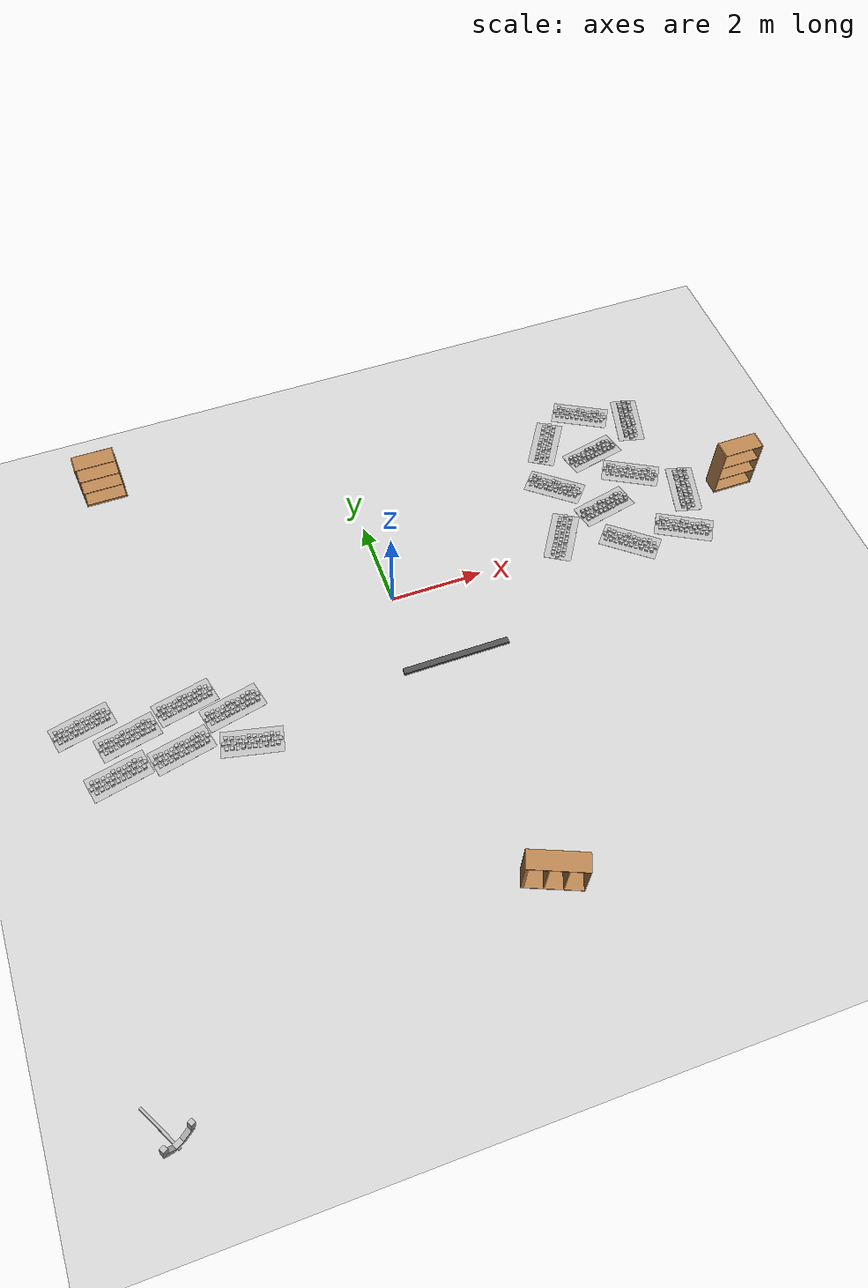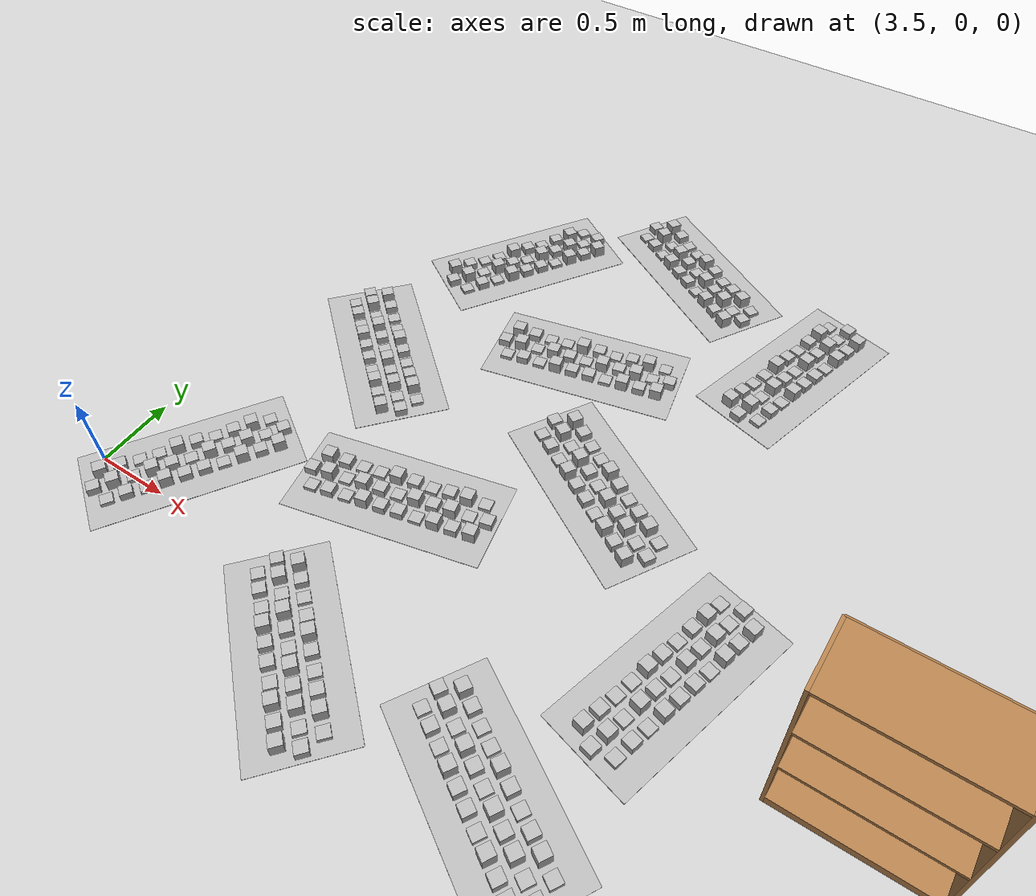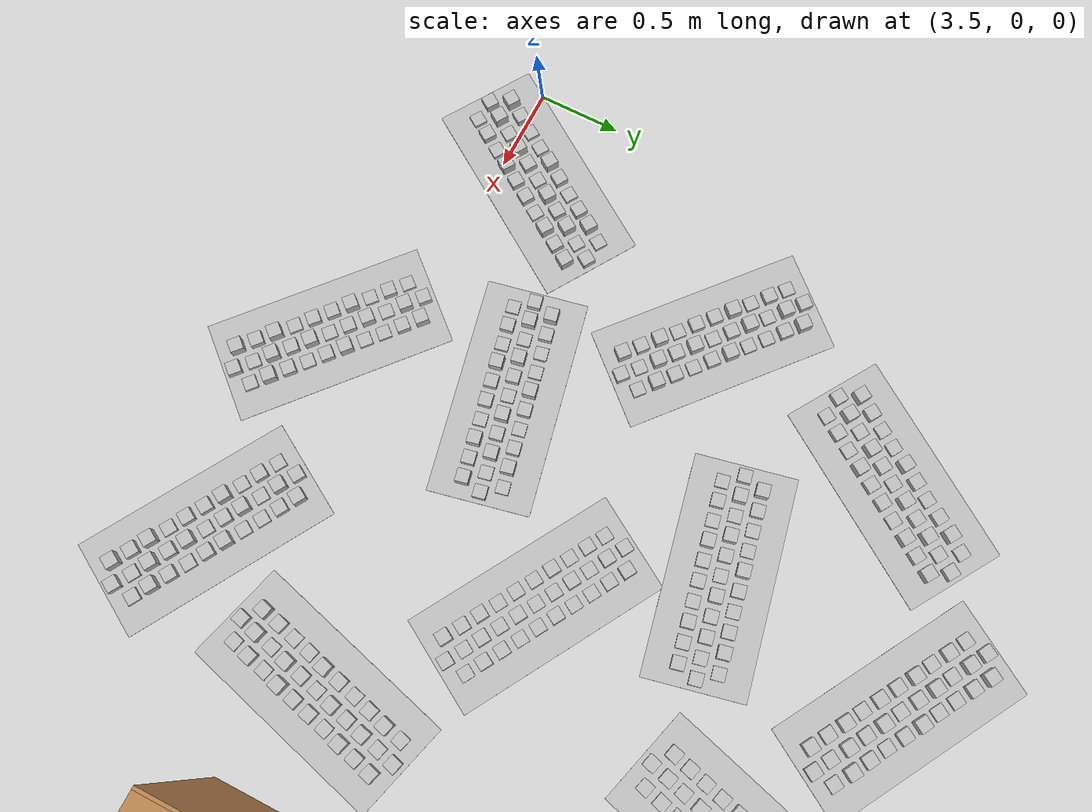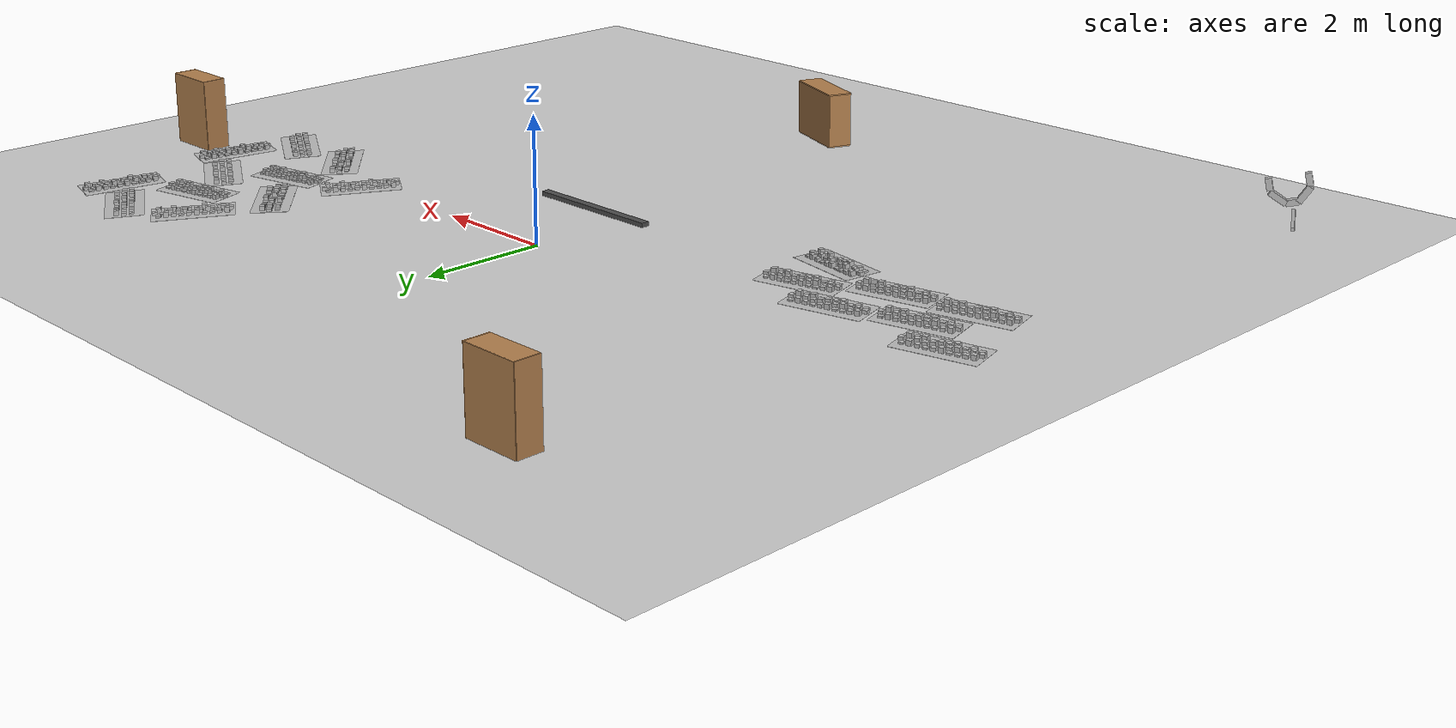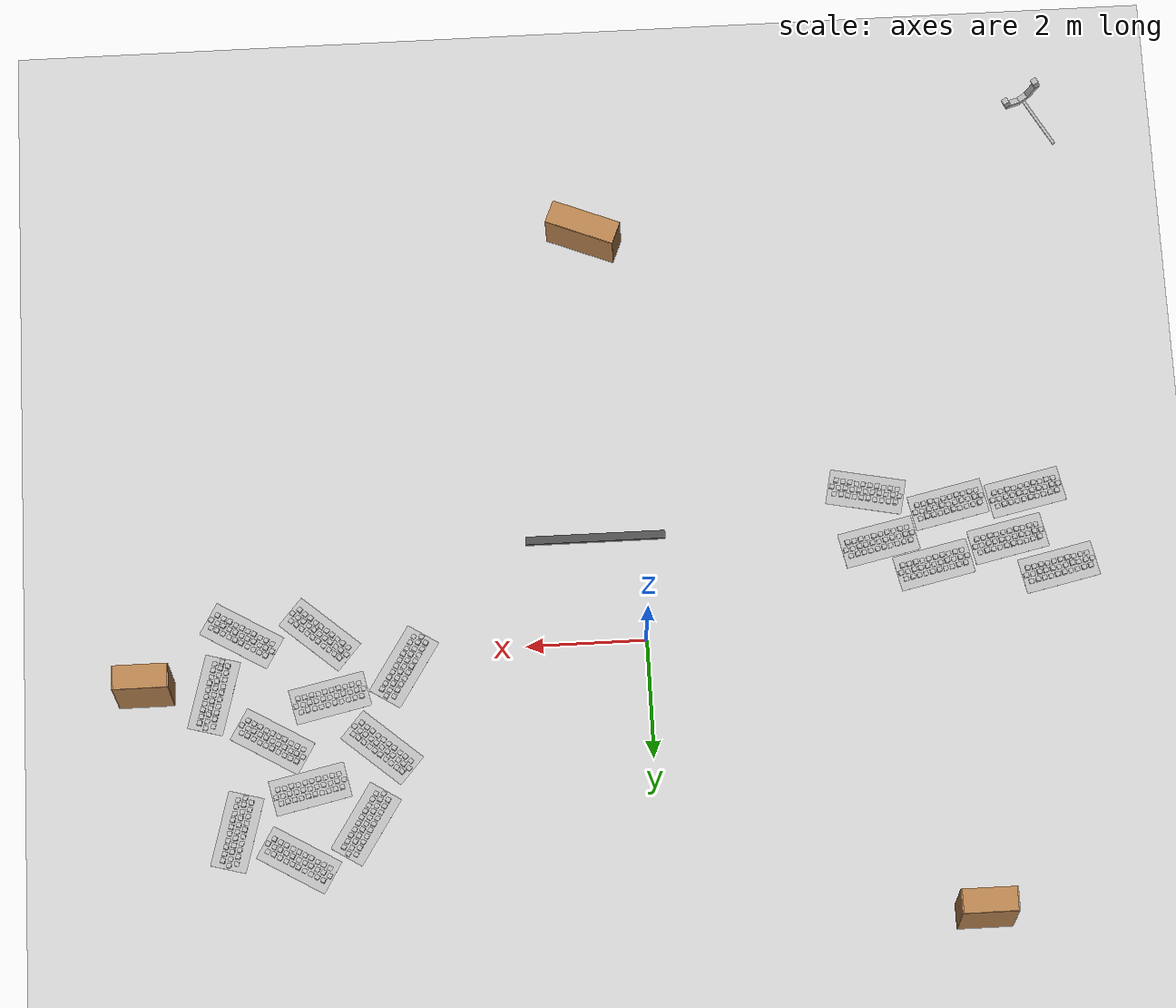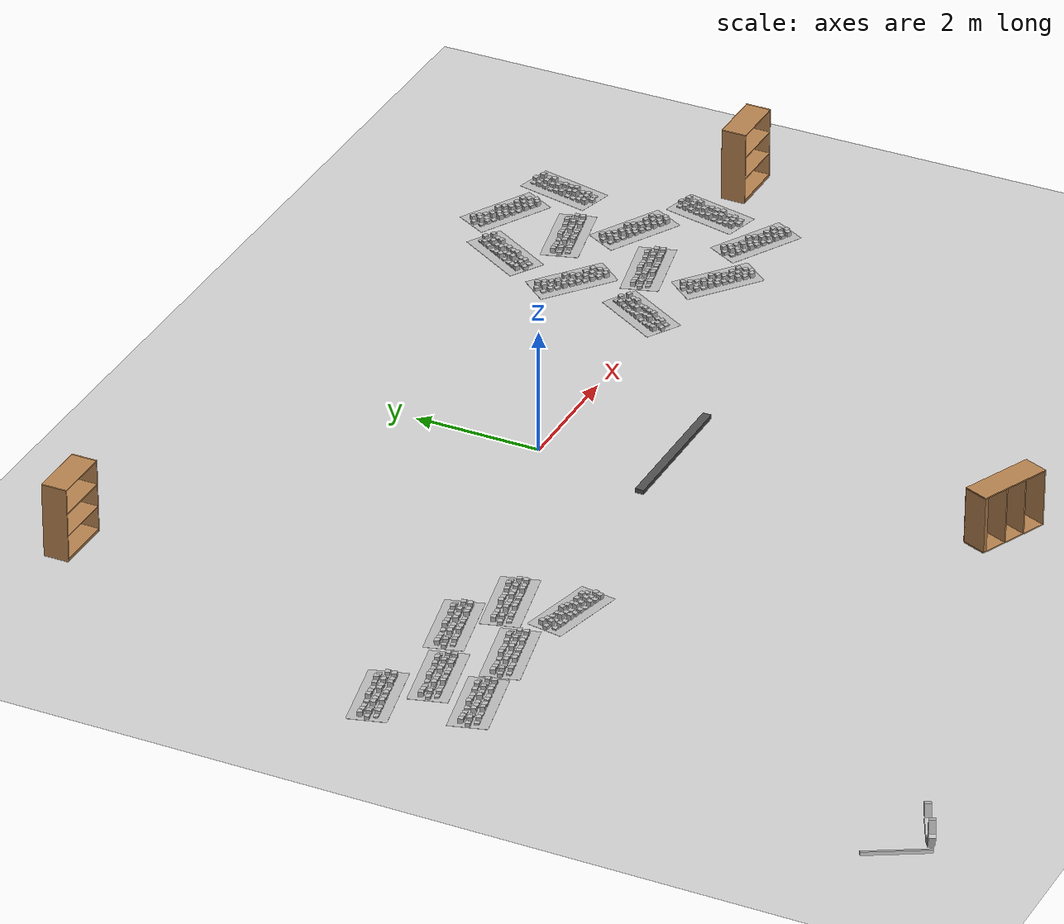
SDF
<sdf version="1.6">
 <world name="default">
  <light name="sun" type="directional">
   <pose>0 0 10 0 -0 0</pose>
   <diffuse>0.8 0.8 0.8 1</diffuse>
   <specular>0.2 0.2 0.2 1</specular>
   <attenuation>
    <range>1000</range>
    <constant>0.9</constant>
    <linear>0.01</linear>
    <quadratic>0.001</quadratic>
   </attenuation>
   <direction>-0.5 0.1 -0.9</direction>
  </light>
  <model name="ground_plane">
   <static>1</static>
   <link name="link">
    <collision name="collision">
     <geometry><plane><normal>0 0 1</normal><size>100 100</size></plane></geometry>
     <surface>
      <contact><collide_bitmask>65535</collide_bitmask></contact>
      <friction><ode><mu>100</mu><mu2>50</mu2></ode></friction>
     </surface>
    </collision>
    <visual name="visual">
     <cast_shadows>0</cast_shadows>
     <geometry><plane><normal>0 0 1</normal><size>100 100</size></plane></geometry>
     <material>
      <script><uri>file://media/materials/scripts/gazebo.material</uri><name>Gazebo/Grey</name></script>
     </material>
    </visual>
   </link>
  </model>
  <gravity>0 0 -9.8</gravity>
  <magnetic_field>6e-06 2.3e-05 -4.2e-05</magnetic_field>
  <atmosphere type="adiabatic"/>
  <physics name="default_physics" default="0" type="ode">
   <max_step_size>0.001</max_step_size>
   <real_time_factor>1</real_time_factor>
   <real_time_update_rate>1000</real_time_update_rate>
  </physics>
  <scene><ambient>0.4 0.4 0.4 1</ambient><background>0.7 0.7 0.7 1</background><shadows>1</shadows></scene>
  <spherical_coordinates>
   <surface_model>EARTH_WGS84</surface_model>
   <latitude_deg>0</latitude_deg>
   <longitude_deg>0</longitude_deg>
   <elevation>0</elevation>
   <heading_deg>0</heading_deg>
  </spherical_coordinates>
  <model name="asphalt_plane">
   <static>1</static>
   <link name="link">
    <collision name="collision"><geometry><box><size>2.32664 0.134694 0.1</size></box></geometry></collision>
    <visual name="visual">
     <cast_shadows>0</cast_shadows>
     <geometry><box><size>2.32664 0.134694 0.1</size></box></geometry>
     <material>
      <script>
       <uri>model://asphalt_plane/materials/scripts</uri>
       <uri>model://asphalt_plane/materials/textures</uri>
       <name>vrc/asphalt</name>
      </script>
     </material>
    </visual>
   </link>
   <pose>0.761424 -1.8179 0 0 -0 0</pose>
  </model>
  <model name="bookshelf">
   <static>1</static>
   <link name="bookshelf::link">
    <inertial><mass>1</mass></inertial>
    <collision name="back">
     <pose>0 0.005 0.6 0 -0 0</pose>
     <geometry><box><size>0.9 0.01 1.2</size></box></geometry>
    </collision>
    <visual name="visual1">
     <pose>0 0.005 0.6 0 -0 0</pose>
     <geometry><box><size>0.9 0.01 1.2</size></box></geometry>
     <material>
      <script><uri>file://media/materials/scripts/gazebo.material</uri><name>Gazebo/Wood</name></script>
     </material>
    </visual>
    <collision name="left_side">
     <pose>0.45 -0.195 0.6 0 -0 0</pose>
     <geometry><box><size>0.02 0.4 1.2</size></box></geometry>
    </collision>
    <visual name="visual2">
     <pose>0.45 -0.195 0.6 0 -0 0</pose>
     <geometry><box><size>0.02 0.4 1.2</size></box></geometry>
     <material>
      <script><uri>file://media/materials/scripts/gazebo.material</uri><name>Gazebo/Wood</name></script>
     </material>
    </visual>
    <collision name="right_side">
     <pose>-0.45 -0.195 0.6 0 -0 0</pose>
     <geometry><box><size>0.02 0.4 1.2</size></box></geometry>
    </collision>
    <visual name="visual3">
     <pose>-0.45 -0.195 0.6 0 -0 0</pose>
     <geometry><box><size>0.02 0.4 1.2</size></box></geometry>
     <material>
      <script><uri>file://media/materials/scripts/gazebo.material</uri><name>Gazebo/Wood</name></script>
     </material>
    </visual>
    <collision name="bottom">
     <pose>0 -0.195 0.03 0 -0 0</pose>
     <geometry><box><size>0.88 0.4 0.06</size></box></geometry>
    </collision>
    <visual name="visual4">
     <pose>0 -0.195 0.03 0 -0 0</pose>
     <geometry><box><size>0.88 0.4 0.06</size></box></geometry>
     <material>
      <script><uri>file://media/materials/scripts/gazebo.material</uri><name>Gazebo/Wood</name></script>
     </material>
    </visual>
    <collision name="top">
     <pose>0 -0.195 1.19 0 -0 0</pose>
     <geometry><box><size>0.88 0.4 0.02</size></box></geometry>
    </collision>
    <visual name="visual5">
     <pose>0 -0.195 1.19 0 -0 0</pose>
     <geometry><box><size>0.88 0.4 0.02</size></box></geometry>
     <material>
      <script><uri>file://media/materials/scripts/gazebo.material</uri><name>Gazebo/Wood</name></script>
     </material>
    </visual>
    <collision name="low_shelf">
     <pose>0 -0.195 0.43 0 -0 0</pose>
     <geometry><box><size>0.88 0.4 0.02</size></box></geometry>
    </collision>
    <visual name="visual6">
     <pose>0 -0.195 0.43 0 -0 0</pose>
     <geometry><box><size>0.88 0.4 0.02</size></box></geometry>
     <material>
      <script><uri>file://media/materials/scripts/gazebo.material</uri><name>Gazebo/Wood</name></script>
     </material>
    </visual>
    <collision name="high_shelf">
     <pose>0 -0.195 0.8 0 -0 0</pose>
     <geometry><box><size>0.88 0.4 0.02</size></box></geometry>
    </collision>
    <visual name="visual7">
     <pose>0 -0.195 0.8 0 -0 0</pose>
     <geometry><box><size>0.88 0.4 0.02</size></box></geometry>
     <material>
      <script><uri>file://media/materials/scripts/gazebo.material</uri><name>Gazebo/Wood</name></script>
     </material>
    </visual>
    <kinematic>1</kinematic>
   </link>
   <pose>0.214064 -6.6606 0.597977 -2.74746 1.55184 -3.14159</pose>
  </model>
  <model name="simple_gripper">
   <link name="riser">
    <pose>-0.15 0 0.5 0 -0 0</pose>
    <inertial>
     <mass>10</mass>
     <inertia><ixx>1</ixx><ixy>0</ixy><ixz>0</ixz><iyy>1</iyy><iyz>0</iyz><izz>1</izz></inertia>
    </inertial>
    <collision name="collision">
     <geometry><box><size>0.05 0.05 1</size></box></geometry>
     <surface><contact><ode><max_vel>0</max_vel></ode></contact></surface>
    </collision>
    <visual name="visual"><geometry><box><size>0.05 0.05 1</size></box></geometry></visual>
   </link>
   <link name="palm">
    <pose>0 0 0.05 0 -0 0</pose>
    <inertial>
     <mass>0.5</mass>
     <inertia><ixx>1</ixx><ixy>0</ixy><ixz>0</ixz><iyy>1</iyy><iyz>0</iyz><izz>1</izz></inertia>
    </inertial>
    <collision name="collision">
     <geometry><box><size>0.1 0.2 0.1</size></box></geometry>
     <surface><contact><ode><max_vel>0</max_vel></ode></contact></surface>
    </collision>
    <visual name="visual"><geometry><box><size>0.1 0.2 0.1</size></box></geometry></visual>
   </link>
   <link name="left_finger">
    <pose>0.1 0.2 0.05 0 0 -0.78539</pose>
    <inertial>
     <mass>0.1</mass>
     <inertia><ixx>1</ixx><ixy>0</ixy><ixz>0</ixz><iyy>1</iyy><iyz>0</iyz><izz>1</izz></inertia>
    </inertial>
    <collision name="collision">
     <geometry><box><size>0.1 0.3 0.1</size></box></geometry>
     <surface>
      <friction><ode><mu>0.1</mu><mu2>0</mu2></ode></friction>
      <contact><ode><max_vel>0</max_vel></ode></contact>
     </surface>
    </collision>
    <visual name="visual"><geometry><box><size>0.1 0.3 0.1</size></box></geometry></visual>
   </link>
   <link name="left_finger_tip">
    <pose>0.336 0.3 0.05 0 -0 1.5707</pose>
    <inertial>
     <mass>0.5</mass>
     <inertia><ixx>1</ixx><ixy>0</ixy><ixz>0</ixz><iyy>1</iyy><iyz>0</iyz><izz>1</izz></inertia>
    </inertial>
    <collision name="collision">
     <geometry><box><size>0.1 0.2 0.1</size></box></geometry>
     <surface>
      <friction><ode><mu>0.1</mu><mu2>0</mu2></ode></friction>
      <contact><ode><max_vel>0</max_vel></ode></contact>
     </surface>
    </collision>
    <visual name="visual"><geometry><box><size>0.1 0.2 0.1</size></box></geometry></visual>
   </link>
   <link name="right_finger">
    <pose>0.1 -0.2 0.05 0 -0 0.78539</pose>
    <inertial>
     <mass>0.1</mass>
     <inertia><ixx>1</ixx><ixy>0</ixy><ixz>0</ixz><iyy>1</iyy><iyz>0</iyz><izz>1</izz></inertia>
    </inertial>
    <collision name="collision">
     <geometry><box><size>0.1 0.3 0.1</size></box></geometry>
     <surface>
      <friction><ode><mu>0.1</mu><mu2>0</mu2></ode></friction>
      <contact><ode><max_vel>0</max_vel></ode></contact>
     </surface>
    </collision>
    <visual name="visual"><geometry><box><size>0.1 0.3 0.1</size></box></geometry></visual>
   </link>
   <link name="right_finger_tip">
    <pose>0.336 -0.3 0.05 0 -0 1.5707</pose>
    <inertial>
     <mass>0.1</mass>
     <inertia><ixx>1</ixx><ixy>0</ixy><ixz>0</ixz><iyy>1</iyy><iyz>0</iyz><izz>1</izz></inertia>
    </inertial>
    <collision name="collision">
     <geometry><box><size>0.1 0.2 0.1</size></box></geometry>
     <surface>
      <friction><ode><mu>0.1</mu><mu2>0</mu2></ode></friction>
      <contact><ode><max_vel>0</max_vel></ode></contact>
     </surface>
    </collision>
    <visual name="visual"><geometry><box><size>0.1 0.2 0.1</size></box></geometry></visual>
   </link>
   <joint name="palm_left_finger" type="revolute">
    <pose>0 -0.15 0 0 -0 0</pose>
    <child>left_finger</child>
    <parent>palm</parent>
    <axis>
     <limit><lower>-0.8</lower><upper>0.8</upper></limit>
     <xyz>0 0 1</xyz>
     <use_parent_model_frame>1</use_parent_model_frame>
     <dynamics><spring_reference>0</spring_reference><spring_stiffness>0</spring_stiffness></dynamics>
    </axis>
   </joint>
   <joint name="left_finger_tip" type="revolute">
    <pose>0 0.1 0 0 -0 0</pose>
    <child>left_finger_tip</child>
    <parent>left_finger</parent>
    <axis>
     <limit><lower>-0.8</lower><upper>0.8</upper></limit>
     <xyz>0 0 1</xyz>
     <use_parent_model_frame>1</use_parent_model_frame>
     <dynamics><spring_reference>0</spring_reference><spring_stiffness>0</spring_stiffness></dynamics>
    </axis>
   </joint>
   <joint name="palm_right_finger" type="revolute">
    <pose>0 0.15 0 0 -0 0</pose>
    <child>right_finger</child>
    <parent>palm</parent>
    <axis>
     <limit><lower>-0.8</lower><upper>0.8</upper></limit>
     <xyz>0 0 1</xyz>
     <use_parent_model_frame>1</use_parent_model_frame>
     <dynamics><spring_reference>0</spring_reference><spring_stiffness>0</spring_stiffness></dynamics>
    </axis>
   </joint>
   <joint name="right_finger_tip" type="revolute">
    <pose>0 0.1 0 0 -0 0</pose>
    <child>right_finger_tip</child>
    <parent>right_finger</parent>
    <axis>
     <limit><lower>-0.8</lower><upper>0.8</upper></limit>
     <xyz>0 0 1</xyz>
     <use_parent_model_frame>1</use_parent_model_frame>
     <dynamics><spring_reference>0</spring_reference><spring_stiffness>0</spring_stiffness></dynamics>
    </axis>
   </joint>
   <joint name="palm_riser" type="prismatic">
    <child>palm</child>
    <parent>riser</parent>
    <axis>
     <limit><lower>0</lower><upper>0.9</upper></limit>
     <xyz>0 0 1</xyz>
     <use_parent_model_frame>1</use_parent_model_frame>
     <dynamics><spring_reference>0</spring_reference><spring_stiffness>0</spring_stiffness></dynamics>
    </axis>
   </joint>
   <gripper name="simple_gripper">
    <grasp_check>
     <detach_steps>40</detach_steps>
     <attach_steps>20</attach_steps>
     <min_contact_count>2</min_contact_count>
    </grasp_check>
    <gripper_link>right_finger</gripper_link>
    <gripper_link>right_finger_tip</gripper_link>
    <gripper_link>left_finger</gripper_link>
    <gripper_link>left_finger_tip</gripper_link>
    <palm_link>palm</palm_link>
   </gripper>
   <pose>-6.96581 -9.31232 0.226157 -1.57077 -1.34555 0.508265</pose>
  </model>
  <model name="frc2016_roughterrain">
   <static>1</static>
   <link name="link">
    <visual name="platform">
     <pose>0 0 0.08269 0 -0 0</pose>
     <geometry><box><size>1.27 0.5969 0.003175</size></box></geometry>
    </visual>
    <collision name="platform">
     <pose>0 0 0.08269 0 -0 0</pose>
     <geometry><box><size>1.27 0.5969 0.003175</size></box></geometry>
    </collision>
    <visual name="row1_block1_sm">
     <pose>0.51435 0.1143 0.09698 0 -0 0</pose>
     <geometry><box><size>0.0762 0.0762 0.0254</size></box></geometry>
    </visual>
    <collision name="row1_block1_sm">
     <pose>0.51435 0.1143 0.09698 0 -0 0</pose>
     <geometry><box><size>0.0762 0.0762 0.0254</size></box></geometry>
    </collision>
    <visual name="row1_block2_lg">
     <pose>0.40005 0.1143 0.12238 0 -0 0</pose>
     <geometry><box><size>0.0762 0.0762 0.0762</size></box></geometry>
    </visual>
    <collision name="row1_block2_lg">
     <pose>0.40005 0.1143 0.12238 0 -0 0</pose>
     <geometry><box><size>0.0762 0.0762 0.0762</size></box></geometry>
    </collision>
    <visual name="row1_block3_md">
     <pose>0.28575 0.1143 0.10968 0 -0 0</pose>
     <geometry><box><size>0.0762 0.0762 0.0508</size></box></geometry>
    </visual>
    <collision name="row1_block3_md">
     <pose>0.28575 0.1143 0.10968 0 -0 0</pose>
     <geometry><box><size>0.0762 0.0762 0.0508</size></box></geometry>
    </collision>
    <visual name="row1_block4_sm">
     <pose>0.17145 0.1143 0.09698 0 -0 0</pose>
     <geometry><box><size>0.0762 0.0762 0.0254</size></box></geometry>
    </visual>
    <collision name="row1_block4_sm">
     <pose>0.17145 0.1143 0.09698 0 -0 0</pose>
     <geometry><box><size>0.0762 0.0762 0.0254</size></box></geometry>
    </collision>
    <visual name="row1_block5_md">
     <pose>0.05715 0.1143 0.10968 0 -0 0</pose>
     <geometry><box><size>0.0762 0.0762 0.0508</size></box></geometry>
    </visual>
    <collision name="row1_block5_md">
     <pose>0.05715 0.1143 0.10968 0 -0 0</pose>
     <geometry><box><size>0.0762 0.0762 0.0508</size></box></geometry>
    </collision>
    <visual name="row1_block6_lg">
     <pose>-0.05715 0.1143 0.12238 0 -0 0</pose>
     <geometry><box><size>0.0762 0.0762 0.0762</size></box></geometry>
    </visual>
    <collision name="row1_block6_lg">
     <pose>-0.05715 0.1143 0.12238 0 -0 0</pose>
     <geometry><box><size>0.0762 0.0762 0.0762</size></box></geometry>
    </collision>
    <visual name="row1_block7_sm">
     <pose>-0.17145 0.1143 0.09698 0 -0 0</pose>
     <geometry><box><size>0.0762 0.0762 0.0254</size></box></geometry>
    </visual>
    <collision name="row1_block7_sm">
     <pose>-0.17145 0.1143 0.09698 0 -0 0</pose>
     <geometry><box><size>0.0762 0.0762 0.0254</size></box></geometry>
    </collision>
    <visual name="row1_block8_sm">
     <pose>-0.28575 0.1143 0.09698 0 -0 0</pose>
     <geometry><box><size>0.0762 0.0762 0.0254</size></box></geometry>
    </visual>
    <collision name="row1_block8_sm">
     <pose>-0.28575 0.1143 0.09698 0 -0 0</pose>
     <geometry><box><size>0.0762 0.0762 0.0254</size></box></geometry>
    </collision>
    <visual name="row1_block9_md">
     <pose>-0.40005 0.1143 0.10968 0 -0 0</pose>
     <geometry><box><size>0.0762 0.0762 0.0508</size></box></geometry>
    </visual>
    <collision name="row1_block9_md">
     <pose>-0.40005 0.1143 0.10968 0 -0 0</pose>
     <geometry><box><size>0.0762 0.0762 0.0508</size></box></geometry>
    </collision>
    <visual name="row1_block10_lg">
     <pose>-0.51435 0.1143 0.12238 0 -0 0</pose>
     <geometry><box><size>0.0762 0.0762 0.0762</size></box></geometry>
    </visual>
    <collision name="row1_block10_lg">
     <pose>-0.51435 0.1143 0.12238 0 -0 0</pose>
     <geometry><box><size>0.0762 0.0762 0.0762</size></box></geometry>
    </collision>
    <visual name="row2_block1_md">
     <pose>0.5715 0 0.10968 0 -0 0</pose>
     <geometry><box><size>0.0762 0.0762 0.0508</size></box></geometry>
    </visual>
    <collision name="row2_block1_md">
     <pose>0.5715 0 0.10968 0 -0 0</pose>
     <geometry><box><size>0.0762 0.0762 0.0508</size></box></geometry>
    </collision>
    <visual name="row2_block2_sm">
     <pose>0.4572 0 0.09698 0 -0 0</pose>
     <geometry><box><size>0.0762 0.0762 0.0254</size></box></geometry>
    </visual>
    <collision name="row2_block2_sm">
     <pose>0.4572 0 0.09698 0 -0 0</pose>
     <geometry><box><size>0.0762 0.0762 0.0254</size></box></geometry>
    </collision>
    <visual name="row2_block3_lg">
     <pose>0.3429 0 0.12238 0 -0 0</pose>
     <geometry><box><size>0.0762 0.0762 0.0762</size></box></geometry>
    </visual>
    <collision name="row2_block3_lg">
     <pose>0.3429 0 0.12238 0 -0 0</pose>
     <geometry><box><size>0.0762 0.0762 0.0762</size></box></geometry>
    </collision>
    <visual name="row2_block4_md">
     <pose>0.2286 0 0.10968 0 -0 0</pose>
     <geometry><box><size>0.0762 0.0762 0.0508</size></box></geometry>
    </visual>
    <collision name="row2_block4_md">
     <pose>0.2286 0 0.10968 0 -0 0</pose>
     <geometry><box><size>0.0762 0.0762 0.0508</size></box></geometry>
    </collision>
    <visual name="row2_block5_lg">
     <pose>0.1143 0 0.12238 0 -0 0</pose>
     <geometry><box><size>0.0762 0.0762 0.0762</size></box></geometry>
    </visual>
    <collision name="row2_block5_lg">
     <pose>0.1143 0 0.12238 0 -0 0</pose>
     <geometry><box><size>0.0762 0.0762 0.0762</size></box></geometry>
    </collision>
    <visual name="row2_block6_sm">
     <pose>0 0 0.09698 0 -0 0</pose>
     <geometry><box><size>0.0762 0.0762 0.0254</size></box></geometry>
    </visual>
    <collision name="row2_block6_sm">
     <pose>0 0 0.09698 0 -0 0</pose>
     <geometry><box><size>0.0762 0.0762 0.0254</size></box></geometry>
    </collision>
    <visual name="row2_block7_md">
     <pose>-0.1143 0 0.10968 0 -0 0</pose>
     <geometry><box><size>0.0762 0.0762 0.0508</size></box></geometry>
    </visual>
    <collision name="row2_block7_md">
     <pose>-0.1143 0 0.10968 0 -0 0</pose>
     <geometry><box><size>0.0762 0.0762 0.0508</size></box></geometry>
    </collision>
    <visual name="row2_block8_lg">
     <pose>-0.2286 0 0.12238 0 -0 0</pose>
     <geometry><box><size>0.0762 0.0762 0.0762</size></box></geometry>
    </visual>
    <collision name="row2_block8_lg">
     <pose>-0.2286 0 0.12238 0 -0 0</pose>
     <geometry><box><size>0.0762 0.0762 0.0762</size></box></geometry>
    </collision>
    <visual name="row2_block9_sm">
     <pose>-0.3429 0 0.09698 0 -0 0</pose>
     <geometry><box><size>0.0762 0.0762 0.0254</size></box></geometry>
    </visual>
    <collision name="row2_block9_sm">
     <pose>-0.3429 0 0.09698 0 -0 0</pose>
     <geometry><box><size>0.0762 0.0762 0.0254</size></box></geometry>
    </collision>
    <visual name="row2_block10_lg">
     <pose>-0.4572 0 0.12238 0 -0 0</pose>
     <geometry><box><size>0.0762 0.0762 0.0762</size></box></geometry>
    </visual>
    <collision name="row2_block10_lg">
     <pose>-0.4572 0 0.12238 0 -0 0</pose>
     <geometry><box><size>0.0762 0.0762 0.0762</size></box></geometry>
    </collision>
    <visual name="row2_block11_md">
     <pose>-0.5715 0 0.10968 0 -0 0</pose>
     <geometry><box><size>0.0762 0.0762 0.0508</size></box></geometry>
    </visual>
    <collision name="row2_block11_md">
     <pose>-0.5715 0 0.10968 0 -0 0</pose>
     <geometry><box><size>0.0762 0.0762 0.0508</size></box></geometry>
    </collision>
    <visual name="row3_block1_lg">
     <pose>0.51435 -0.1143 0.12238 0 -0 0</pose>
     <geometry><box><size>0.0762 0.0762 0.0762</size></box></geometry>
    </visual>
    <collision name="row3_block1_lg">
     <pose>0.51435 -0.1143 0.12238 0 -0 0</pose>
     <geometry><box><size>0.0762 0.0762 0.0762</size></box></geometry>
    </collision>
    <visual name="row3_block2_md">
     <pose>0.40005 -0.1143 0.10968 0 -0 0</pose>
     <geometry><box><size>0.0762 0.0762 0.0508</size></box></geometry>
    </visual>
    <collision name="row3_block2_md">
     <pose>0.40005 -0.1143 0.10968 0 -0 0</pose>
     <geometry><box><size>0.0762 0.0762 0.0508</size></box></geometry>
    </collision>
    <visual name="row3_block3_lg">
     <pose>0.28575 -0.1143 0.12238 0 -0 0</pose>
     <geometry><box><size>0.0762 0.0762 0.0762</size></box></geometry>
    </visual>
    <collision name="row3_block3_lg">
     <pose>0.28575 -0.1143 0.12238 0 -0 0</pose>
     <geometry><box><size>0.0762 0.0762 0.0762</size></box></geometry>
    </collision>
    <visual name="row3_block4_sm">
     <pose>0.17145 -0.1143 0.09698 0 -0 0</pose>
     <geometry><box><size>0.0762 0.0762 0.0254</size></box></geometry>
    </visual>
    <collision name="row3_block4_sm">
     <pose>0.17145 -0.1143 0.09698 0 -0 0</pose>
     <geometry><box><size>0.0762 0.0762 0.0254</size></box></geometry>
    </collision>
    <visual name="row3_block5_md">
     <pose>0.05715 -0.1143 0.10968 0 -0 0</pose>
     <geometry><box><size>0.0762 0.0762 0.0508</size></box></geometry>
    </visual>
    <collision name="row3_block5_md">
     <pose>0.05715 -0.1143 0.10968 0 -0 0</pose>
     <geometry><box><size>0.0762 0.0762 0.0508</size></box></geometry>
    </collision>
    <visual name="row3_block6_md">
     <pose>-0.05715 -0.1143 0.10968 0 -0 0</pose>
     <geometry><box><size>0.0762 0.0762 0.0508</size></box></geometry>
    </visual>
    <collision name="row3_block6_md">
     <pose>-0.05715 -0.1143 0.10968 0 -0 0</pose>
     <geometry><box><size>0.0762 0.0762 0.0508</size></box></geometry>
    </collision>
    <visual name="row3_block7_lg">
     <pose>-0.17145 -0.1143 0.12238 0 -0 0</pose>
     <geometry><box><size>0.0762 0.0762 0.0762</size></box></geometry>
    </visual>
    <collision name="row3_block7_lg">
     <pose>-0.17145 -0.1143 0.12238 0 -0 0</pose>
     <geometry><box><size>0.0762 0.0762 0.0762</size></box></geometry>
    </collision>
    <visual name="row3_block8_sm">
     <pose>-0.28575 -0.1143 0.09698 0 -0 0</pose>
     <geometry><box><size>0.0762 0.0762 0.0254</size></box></geometry>
    </visual>
    <collision name="row3_block8_sm">
     <pose>-0.28575 -0.1143 0.09698 0 -0 0</pose>
     <geometry><box><size>0.0762 0.0762 0.0254</size></box></geometry>
    </collision>
    <visual name="row3_block9_md">
     <pose>-0.40005 -0.1143 0.10968 0 -0 0</pose>
     <geometry><box><size>0.0762 0.0762 0.0508</size></box></geometry>
    </visual>
    <collision name="row3_block9_md">
     <pose>-0.40005 -0.1143 0.10968 0 -0 0</pose>
     <geometry><box><size>0.0762 0.0762 0.0508</size></box></geometry>
    </collision>
    <visual name="row3_block10_sm">
     <pose>-0.51435 -0.1143 0.09698 0 -0 0</pose>
     <geometry><box><size>0.0762 0.0762 0.0254</size></box></geometry>
    </visual>
    <collision name="row3_block10_sm">
     <pose>-0.51435 -0.1143 0.09698 0 -0 0</pose>
     <geometry><box><size>0.0762 0.0762 0.0254</size></box></geometry>
    </collision>
   </link>
   <pose>-5.15078 -2.06724 0 -0.037204 0.000686 0.216059</pose>
  </model>
  <model name="frc2016_roughterrain_clone">
   <static>1</static>
   <link name="link">
    <visual name="platform">
     <pose>0 0 0.08269 0 -0 0</pose>
     <geometry><box><size>1.27 0.5969 0.003175</size></box></geometry>
    </visual>
    <collision name="platform">
     <pose>0 0 0.08269 0 -0 0</pose>
     <geometry><box><size>1.27 0.5969 0.003175</size></box></geometry>
    </collision>
    <visual name="row1_block1_sm">
     <pose>0.51435 0.1143 0.09698 0 -0 0</pose>
     <geometry><box><size>0.0762 0.0762 0.0254</size></box></geometry>
    </visual>
    <collision name="row1_block1_sm">
     <pose>0.51435 0.1143 0.09698 0 -0 0</pose>
     <geometry><box><size>0.0762 0.0762 0.0254</size></box></geometry>
    </collision>
    <visual name="row1_block2_lg">
     <pose>0.40005 0.1143 0.12238 0 -0 0</pose>
     <geometry><box><size>0.0762 0.0762 0.0762</size></box></geometry>
    </visual>
    <collision name="row1_block2_lg">
     <pose>0.40005 0.1143 0.12238 0 -0 0</pose>
     <geometry><box><size>0.0762 0.0762 0.0762</size></box></geometry>
    </collision>
    <visual name="row1_block3_md">
     <pose>0.28575 0.1143 0.10968 0 -0 0</pose>
     <geometry><box><size>0.0762 0.0762 0.0508</size></box></geometry>
    </visual>
    <collision name="row1_block3_md">
     <pose>0.28575 0.1143 0.10968 0 -0 0</pose>
     <geometry><box><size>0.0762 0.0762 0.0508</size></box></geometry>
    </collision>
    <visual name="row1_block4_sm">
     <pose>0.17145 0.1143 0.09698 0 -0 0</pose>
     <geometry><box><size>0.0762 0.0762 0.0254</size></box></geometry>
    </visual>
    <collision name="row1_block4_sm">
     <pose>0.17145 0.1143 0.09698 0 -0 0</pose>
     <geometry><box><size>0.0762 0.0762 0.0254</size></box></geometry>
    </collision>
    <visual name="row1_block5_md">
     <pose>0.05715 0.1143 0.10968 0 -0 0</pose>
     <geometry><box><size>0.0762 0.0762 0.0508</size></box></geometry>
    </visual>
    <collision name="row1_block5_md">
     <pose>0.05715 0.1143 0.10968 0 -0 0</pose>
     <geometry><box><size>0.0762 0.0762 0.0508</size></box></geometry>
    </collision>
    <visual name="row1_block6_lg">
     <pose>-0.05715 0.1143 0.12238 0 -0 0</pose>
     <geometry><box><size>0.0762 0.0762 0.0762</size></box></geometry>
    </visual>
    <collision name="row1_block6_lg">
     <pose>-0.05715 0.1143 0.12238 0 -0 0</pose>
     <geometry><box><size>0.0762 0.0762 0.0762</size></box></geometry>
    </collision>
    <visual name="row1_block7_sm">
     <pose>-0.17145 0.1143 0.09698 0 -0 0</pose>
     <geometry><box><size>0.0762 0.0762 0.0254</size></box></geometry>
    </visual>
    <collision name="row1_block7_sm">
     <pose>-0.17145 0.1143 0.09698 0 -0 0</pose>
     <geometry><box><size>0.0762 0.0762 0.0254</size></box></geometry>
    </collision>
    <visual name="row1_block8_sm">
     <pose>-0.28575 0.1143 0.09698 0 -0 0</pose>
     <geometry><box><size>0.0762 0.0762 0.0254</size></box></geometry>
    </visual>
    <collision name="row1_block8_sm">
     <pose>-0.28575 0.1143 0.09698 0 -0 0</pose>
     <geometry><box><size>0.0762 0.0762 0.0254</size></box></geometry>
    </collision>
    <visual name="row1_block9_md">
     <pose>-0.40005 0.1143 0.10968 0 -0 0</pose>
     <geometry><box><size>0.0762 0.0762 0.0508</size></box></geometry>
    </visual>
    <collision name="row1_block9_md">
     <pose>-0.40005 0.1143 0.10968 0 -0 0</pose>
     <geometry><box><size>0.0762 0.0762 0.0508</size></box></geometry>
    </collision>
    <visual name="row1_block10_lg">
     <pose>-0.51435 0.1143 0.12238 0 -0 0</pose>
     <geometry><box><size>0.0762 0.0762 0.0762</size></box></geometry>
    </visual>
    <collision name="row1_block10_lg">
     <pose>-0.51435 0.1143 0.12238 0 -0 0</pose>
     <geometry><box><size>0.0762 0.0762 0.0762</size></box></geometry>
    </collision>
    <visual name="row2_block1_md">
     <pose>0.5715 0 0.10968 0 -0 0</pose>
     <geometry><box><size>0.0762 0.0762 0.0508</size></box></geometry>
    </visual>
    <collision name="row2_block1_md">
     <pose>0.5715 0 0.10968 0 -0 0</pose>
     <geometry><box><size>0.0762 0.0762 0.0508</size></box></geometry>
    </collision>
    <visual name="row2_block2_sm">
     <pose>0.4572 0 0.09698 0 -0 0</pose>
     <geometry><box><size>0.0762 0.0762 0.0254</size></box></geometry>
    </visual>
    <collision name="row2_block2_sm">
     <pose>0.4572 0 0.09698 0 -0 0</pose>
     <geometry><box><size>0.0762 0.0762 0.0254</size></box></geometry>
    </collision>
    <visual name="row2_block3_lg">
     <pose>0.3429 0 0.12238 0 -0 0</pose>
     <geometry><box><size>0.0762 0.0762 0.0762</size></box></geometry>
    </visual>
    <collision name="row2_block3_lg">
     <pose>0.3429 0 0.12238 0 -0 0</pose>
     <geometry><box><size>0.0762 0.0762 0.0762</size></box></geometry>
    </collision>
    <visual name="row2_block4_md">
     <pose>0.2286 0 0.10968 0 -0 0</pose>
     <geometry><box><size>0.0762 0.0762 0.0508</size></box></geometry>
    </visual>
    <collision name="row2_block4_md">
     <pose>0.2286 0 0.10968 0 -0 0</pose>
     <geometry><box><size>0.0762 0.0762 0.0508</size></box></geometry>
    </collision>
    <visual name="row2_block5_lg">
     <pose>0.1143 0 0.12238 0 -0 0</pose>
     <geometry><box><size>0.0762 0.0762 0.0762</size></box></geometry>
    </visual>
    <collision name="row2_block5_lg">
     <pose>0.1143 0 0.12238 0 -0 0</pose>
     <geometry><box><size>0.0762 0.0762 0.0762</size></box></geometry>
    </collision>
    <visual name="row2_block6_sm">
     <pose>0 0 0.09698 0 -0 0</pose>
     <geometry><box><size>0.0762 0.0762 0.0254</size></box></geometry>
    </visual>
    <collision name="row2_block6_sm">
     <pose>0 0 0.09698 0 -0 0</pose>
     <geometry><box><size>0.0762 0.0762 0.0254</size></box></geometry>
    </collision>
    <visual name="row2_block7_md">
     <pose>-0.1143 0 0.10968 0 -0 0</pose>
     <geometry><box><size>0.0762 0.0762 0.0508</size></box></geometry>
    </visual>
    <collision name="row2_block7_md">
     <pose>-0.1143 0 0.10968 0 -0 0</pose>
     <geometry><box><size>0.0762 0.0762 0.0508</size></box></geometry>
    </collision>
    <visual name="row2_block8_lg">
     <pose>-0.2286 0 0.12238 0 -0 0</pose>
     <geometry><box><size>0.0762 0.0762 0.0762</size></box></geometry>
    </visual>
    <collision name="row2_block8_lg">
     <pose>-0.2286 0 0.12238 0 -0 0</pose>
     <geometry><box><size>0.0762 0.0762 0.0762</size></box></geometry>
    </collision>
    <visual name="row2_block9_sm">
     <pose>-0.3429 0 0.09698 0 -0 0</pose>
     <geometry><box><size>0.0762 0.0762 0.0254</size></box></geometry>
    </visual>
    <collision name="row2_block9_sm">
     <pose>-0.3429 0 0.09698 0 -0 0</pose>
     <geometry><box><size>0.0762 0.0762 0.0254</size></box></geometry>
    </collision>
    <visual name="row2_block10_lg">
     <pose>-0.4572 0 0.12238 0 -0 0</pose>
     <geometry><box><size>0.0762 0.0762 0.0762</size></box></geometry>
    </visual>
    <collision name="row2_block10_lg">
     <pose>-0.4572 0 0.12238 0 -0 0</pose>
     <geometry><box><size>0.0762 0.0762 0.0762</size></box></geometry>
    </collision>
    <visual name="row2_block11_md">
     <pose>-0.5715 0 0.10968 0 -0 0</pose>
     <geometry><box><size>0.0762 0.0762 0.0508</size></box></geometry>
    </visual>
    <collision name="row2_block11_md">
     <pose>-0.5715 0 0.10968 0 -0 0</pose>
     <geometry><box><size>0.0762 0.0762 0.0508</size></box></geometry>
    </collision>
    <visual name="row3_block1_lg">
     <pose>0.51435 -0.1143 0.12238 0 -0 0</pose>
     <geometry><box><size>0.0762 0.0762 0.0762</size></box></geometry>
    </visual>
    <collision name="row3_block1_lg">
     <pose>0.51435 -0.1143 0.12238 0 -0 0</pose>
     <geometry><box><size>0.0762 0.0762 0.0762</size></box></geometry>
    </collision>
    <visual name="row3_block2_md">
     <pose>0.40005 -0.1143 0.10968 0 -0 0</pose>
     <geometry><box><size>0.0762 0.0762 0.0508</size></box></geometry>
    </visual>
    <collision name="row3_block2_md">
     <pose>0.40005 -0.1143 0.10968 0 -0 0</pose>
     <geometry><box><size>0.0762 0.0762 0.0508</size></box></geometry>
    </collision>
    <visual name="row3_block3_lg">
     <pose>0.28575 -0.1143 0.12238 0 -0 0</pose>
     <geometry><box><size>0.0762 0.0762 0.0762</size></box></geometry>
    </visual>
    <collision name="row3_block3_lg">
     <pose>0.28575 -0.1143 0.12238 0 -0 0</pose>
     <geometry><box><size>0.0762 0.0762 0.0762</size></box></geometry>
    </collision>
    <visual name="row3_block4_sm">
     <pose>0.17145 -0.1143 0.09698 0 -0 0</pose>
     <geometry><box><size>0.0762 0.0762 0.0254</size></box></geometry>
    </visual>
    <collision name="row3_block4_sm">
     <pose>0.17145 -0.1143 0.09698 0 -0 0</pose>
     <geometry><box><size>0.0762 0.0762 0.0254</size></box></geometry>
    </collision>
    <visual name="row3_block5_md">
     <pose>0.05715 -0.1143 0.10968 0 -0 0</pose>
     <geometry><box><size>0.0762 0.0762 0.0508</size></box></geometry>
    </visual>
    <collision name="row3_block5_md">
     <pose>0.05715 -0.1143 0.10968 0 -0 0</pose>
     <geometry><box><size>0.0762 0.0762 0.0508</size></box></geometry>
    </collision>
    <visual name="row3_block6_md">
     <pose>-0.05715 -0.1143 0.10968 0 -0 0</pose>
     <geometry><box><size>0.0762 0.0762 0.0508</size></box></geometry>
    </visual>
    <collision name="row3_block6_md">
     <pose>-0.05715 -0.1143 0.10968 0 -0 0</pose>
     <geometry><box><size>0.0762 0.0762 0.0508</size></box></geometry>
    </collision>
    <visual name="row3_block7_lg">
     <pose>-0.17145 -0.1143 0.12238 0 -0 0</pose>
     <geometry><box><size>0.0762 0.0762 0.0762</size></box></geometry>
    </visual>
    <collision name="row3_block7_lg">
     <pose>-0.17145 -0.1143 0.12238 0 -0 0</pose>
     <geometry><box><size>0.0762 0.0762 0.0762</size></box></geometry>
    </collision>
    <visual name="row3_block8_sm">
     <pose>-0.28575 -0.1143 0.09698 0 -0 0</pose>
     <geometry><box><size>0.0762 0.0762 0.0254</size></box></geometry>
    </visual>
    <collision name="row3_block8_sm">
     <pose>-0.28575 -0.1143 0.09698 0 -0 0</pose>
     <geometry><box><size>0.0762 0.0762 0.0254</size></box></geometry>
    </collision>
    <visual name="row3_block9_md">
     <pose>-0.40005 -0.1143 0.10968 0 -0 0</pose>
     <geometry><box><size>0.0762 0.0762 0.0508</size></box></geometry>
    </visual>
    <collision name="row3_block9_md">
     <pose>-0.40005 -0.1143 0.10968 0 -0 0</pose>
     <geometry><box><size>0.0762 0.0762 0.0508</size></box></geometry>
    </collision>
    <visual name="row3_block10_sm">
     <pose>-0.51435 -0.1143 0.09698 0 -0 0</pose>
     <geometry><box><size>0.0762 0.0762 0.0254</size></box></geometry>
    </visual>
    <collision name="row3_block10_sm">
     <pose>-0.51435 -0.1143 0.09698 0 -0 0</pose>
     <geometry><box><size>0.0762 0.0762 0.0254</size></box></geometry>
    </collision>
   </link>
   <pose>-3.79265 -2.3603 0 -0.032751 0.017667 -0.207851</pose>
  </model>
  <model name="frc2016_roughterrain_clone_0">
   <static>1</static>
   <link name="link">
    <visual name="platform">
     <pose>0 0 0.08269 0 -0 0</pose>
     <geometry><box><size>1.27 0.5969 0.003175</size></box></geometry>
    </visual>
    <collision name="platform">
     <pose>0 0 0.08269 0 -0 0</pose>
     <geometry><box><size>1.27 0.5969 0.003175</size></box></geometry>
    </collision>
    <visual name="row1_block1_sm">
     <pose>0.51435 0.1143 0.09698 0 -0 0</pose>
     <geometry><box><size>0.0762 0.0762 0.0254</size></box></geometry>
    </visual>
    <collision name="row1_block1_sm">
     <pose>0.51435 0.1143 0.09698 0 -0 0</pose>
     <geometry><box><size>0.0762 0.0762 0.0254</size></box></geometry>
    </collision>
    <visual name="row1_block2_lg">
     <pose>0.40005 0.1143 0.12238 0 -0 0</pose>
     <geometry><box><size>0.0762 0.0762 0.0762</size></box></geometry>
    </visual>
    <collision name="row1_block2_lg">
     <pose>0.40005 0.1143 0.12238 0 -0 0</pose>
     <geometry><box><size>0.0762 0.0762 0.0762</size></box></geometry>
    </collision>
    <visual name="row1_block3_md">
     <pose>0.28575 0.1143 0.10968 0 -0 0</pose>
     <geometry><box><size>0.0762 0.0762 0.0508</size></box></geometry>
    </visual>
    <collision name="row1_block3_md">
     <pose>0.28575 0.1143 0.10968 0 -0 0</pose>
     <geometry><box><size>0.0762 0.0762 0.0508</size></box></geometry>
    </collision>
    <visual name="row1_block4_sm">
     <pose>0.17145 0.1143 0.09698 0 -0 0</pose>
     <geometry><box><size>0.0762 0.0762 0.0254</size></box></geometry>
    </visual>
    <collision name="row1_block4_sm">
     <pose>0.17145 0.1143 0.09698 0 -0 0</pose>
     <geometry><box><size>0.0762 0.0762 0.0254</size></box></geometry>
    </collision>
    <visual name="row1_block5_md">
     <pose>0.05715 0.1143 0.10968 0 -0 0</pose>
     <geometry><box><size>0.0762 0.0762 0.0508</size></box></geometry>
    </visual>
    <collision name="row1_block5_md">
     <pose>0.05715 0.1143 0.10968 0 -0 0</pose>
     <geometry><box><size>0.0762 0.0762 0.0508</size></box></geometry>
    </collision>
    <visual name="row1_block6_lg">
     <pose>-0.05715 0.1143 0.12238 0 -0 0</pose>
     <geometry><box><size>0.0762 0.0762 0.0762</size></box></geometry>
    </visual>
    <collision name="row1_block6_lg">
     <pose>-0.05715 0.1143 0.12238 0 -0 0</pose>
     <geometry><box><size>0.0762 0.0762 0.0762</size></box></geometry>
    </collision>
    <visual name="row1_block7_sm">
     <pose>-0.17145 0.1143 0.09698 0 -0 0</pose>
     <geometry><box><size>0.0762 0.0762 0.0254</size></box></geometry>
    </visual>
    <collision name="row1_block7_sm">
     <pose>-0.17145 0.1143 0.09698 0 -0 0</pose>
     <geometry><box><size>0.0762 0.0762 0.0254</size></box></geometry>
    </collision>
    <visual name="row1_block8_sm">
     <pose>-0.28575 0.1143 0.09698 0 -0 0</pose>
     <geometry><box><size>0.0762 0.0762 0.0254</size></box></geometry>
    </visual>
    <collision name="row1_block8_sm">
     <pose>-0.28575 0.1143 0.09698 0 -0 0</pose>
     <geometry><box><size>0.0762 0.0762 0.0254</size></box></geometry>
    </collision>
    <visual name="row1_block9_md">
     <pose>-0.40005 0.1143 0.10968 0 -0 0</pose>
     <geometry><box><size>0.0762 0.0762 0.0508</size></box></geometry>
    </visual>
    <collision name="row1_block9_md">
     <pose>-0.40005 0.1143 0.10968 0 -0 0</pose>
     <geometry><box><size>0.0762 0.0762 0.0508</size></box></geometry>
    </collision>
    <visual name="row1_block10_lg">
     <pose>-0.51435 0.1143 0.12238 0 -0 0</pose>
     <geometry><box><size>0.0762 0.0762 0.0762</size></box></geometry>
    </visual>
    <collision name="row1_block10_lg">
     <pose>-0.51435 0.1143 0.12238 0 -0 0</pose>
     <geometry><box><size>0.0762 0.0762 0.0762</size></box></geometry>
    </collision>
    <visual name="row2_block1_md">
     <pose>0.5715 0 0.10968 0 -0 0</pose>
     <geometry><box><size>0.0762 0.0762 0.0508</size></box></geometry>
    </visual>
    <collision name="row2_block1_md">
     <pose>0.5715 0 0.10968 0 -0 0</pose>
     <geometry><box><size>0.0762 0.0762 0.0508</size></box></geometry>
    </collision>
    <visual name="row2_block2_sm">
     <pose>0.4572 0 0.09698 0 -0 0</pose>
     <geometry><box><size>0.0762 0.0762 0.0254</size></box></geometry>
    </visual>
    <collision name="row2_block2_sm">
     <pose>0.4572 0 0.09698 0 -0 0</pose>
     <geometry><box><size>0.0762 0.0762 0.0254</size></box></geometry>
    </collision>
    <visual name="row2_block3_lg">
     <pose>0.3429 0 0.12238 0 -0 0</pose>
     <geometry><box><size>0.0762 0.0762 0.0762</size></box></geometry>
    </visual>
    <collision name="row2_block3_lg">
     <pose>0.3429 0 0.12238 0 -0 0</pose>
     <geometry><box><size>0.0762 0.0762 0.0762</size></box></geometry>
    </collision>
    <visual name="row2_block4_md">
     <pose>0.2286 0 0.10968 0 -0 0</pose>
     <geometry><box><size>0.0762 0.0762 0.0508</size></box></geometry>
    </visual>
    <collision name="row2_block4_md">
     <pose>0.2286 0 0.10968 0 -0 0</pose>
     <geometry><box><size>0.0762 0.0762 0.0508</size></box></geometry>
    </collision>
    <visual name="row2_block5_lg">
     <pose>0.1143 0 0.12238 0 -0 0</pose>
     <geometry><box><size>0.0762 0.0762 0.0762</size></box></geometry>
    </visual>
    <collision name="row2_block5_lg">
     <pose>0.1143 0 0.12238 0 -0 0</pose>
     <geometry><box><size>0.0762 0.0762 0.0762</size></box></geometry>
    </collision>
    <visual name="row2_block6_sm">
     <pose>0 0 0.09698 0 -0 0</pose>
     <geometry><box><size>0.0762 0.0762 0.0254</size></box></geometry>
    </visual>
    <collision name="row2_block6_sm">
     <pose>0 0 0.09698 0 -0 0</pose>
     <geometry><box><size>0.0762 0.0762 0.0254</size></box></geometry>
    </collision>
    <visual name="row2_block7_md">
     <pose>-0.1143 0 0.10968 0 -0 0</pose>
     <geometry><box><size>0.0762 0.0762 0.0508</size></box></geometry>
    </visual>
    <collision name="row2_block7_md">
     <pose>-0.1143 0 0.10968 0 -0 0</pose>
     <geometry><box><size>0.0762 0.0762 0.0508</size></box></geometry>
    </collision>
    <visual name="row2_block8_lg">
     <pose>-0.2286 0 0.12238 0 -0 0</pose>
     <geometry><box><size>0.0762 0.0762 0.0762</size></box></geometry>
    </visual>
    <collision name="row2_block8_lg">
     <pose>-0.2286 0 0.12238 0 -0 0</pose>
     <geometry><box><size>0.0762 0.0762 0.0762</size></box></geometry>
    </collision>
    <visual name="row2_block9_sm">
     <pose>-0.3429 0 0.09698 0 -0 0</pose>
     <geometry><box><size>0.0762 0.0762 0.0254</size></box></geometry>
    </visual>
    <collision name="row2_block9_sm">
     <pose>-0.3429 0 0.09698 0 -0 0</pose>
     <geometry><box><size>0.0762 0.0762 0.0254</size></box></geometry>
    </collision>
    <visual name="row2_block10_lg">
     <pose>-0.4572 0 0.12238 0 -0 0</pose>
     <geometry><box><size>0.0762 0.0762 0.0762</size></box></geometry>
    </visual>
    <collision name="row2_block10_lg">
     <pose>-0.4572 0 0.12238 0 -0 0</pose>
     <geometry><box><size>0.0762 0.0762 0.0762</size></box></geometry>
    </collision>
    <visual name="row2_block11_md">
     <pose>-0.5715 0 0.10968 0 -0 0</pose>
     <geometry><box><size>0.0762 0.0762 0.0508</size></box></geometry>
    </visual>
    <collision name="row2_block11_md">
     <pose>-0.5715 0 0.10968 0 -0 0</pose>
     <geometry><box><size>0.0762 0.0762 0.0508</size></box></geometry>
    </collision>
    <visual name="row3_block1_lg">
     <pose>0.51435 -0.1143 0.12238 0 -0 0</pose>
     <geometry><box><size>0.0762 0.0762 0.0762</size></box></geometry>
    </visual>
    <collision name="row3_block1_lg">
     <pose>0.51435 -0.1143 0.12238 0 -0 0</pose>
     <geometry><box><size>0.0762 0.0762 0.0762</size></box></geometry>
    </collision>
    <visual name="row3_block2_md">
     <pose>0.40005 -0.1143 0.10968 0 -0 0</pose>
     <geometry><box><size>0.0762 0.0762 0.0508</size></box></geometry>
    </visual>
    <collision name="row3_block2_md">
     <pose>0.40005 -0.1143 0.10968 0 -0 0</pose>
     <geometry><box><size>0.0762 0.0762 0.0508</size></box></geometry>
    </collision>
    <visual name="row3_block3_lg">
     <pose>0.28575 -0.1143 0.12238 0 -0 0</pose>
     <geometry><box><size>0.0762 0.0762 0.0762</size></box></geometry>
    </visual>
    <collision name="row3_block3_lg">
     <pose>0.28575 -0.1143 0.12238 0 -0 0</pose>
     <geometry><box><size>0.0762 0.0762 0.0762</size></box></geometry>
    </collision>
    <visual name="row3_block4_sm">
     <pose>0.17145 -0.1143 0.09698 0 -0 0</pose>
     <geometry><box><size>0.0762 0.0762 0.0254</size></box></geometry>
    </visual>
    <collision name="row3_block4_sm">
     <pose>0.17145 -0.1143 0.09698 0 -0 0</pose>
     <geometry><box><size>0.0762 0.0762 0.0254</size></box></geometry>
    </collision>
    <visual name="row3_block5_md">
     <pose>0.05715 -0.1143 0.10968 0 -0 0</pose>
     <geometry><box><size>0.0762 0.0762 0.0508</size></box></geometry>
    </visual>
    <collision name="row3_block5_md">
     <pose>0.05715 -0.1143 0.10968 0 -0 0</pose>
     <geometry><box><size>0.0762 0.0762 0.0508</size></box></geometry>
    </collision>
    <visual name="row3_block6_md">
     <pose>-0.05715 -0.1143 0.10968 0 -0 0</pose>
     <geometry><box><size>0.0762 0.0762 0.0508</size></box></geometry>
    </visual>
    <collision name="row3_block6_md">
     <pose>-0.05715 -0.1143 0.10968 0 -0 0</pose>
     <geometry><box><size>0.0762 0.0762 0.0508</size></box></geometry>
    </collision>
    <visual name="row3_block7_lg">
     <pose>-0.17145 -0.1143 0.12238 0 -0 0</pose>
     <geometry><box><size>0.0762 0.0762 0.0762</size></box></geometry>
    </visual>
    <collision name="row3_block7_lg">
     <pose>-0.17145 -0.1143 0.12238 0 -0 0</pose>
     <geometry><box><size>0.0762 0.0762 0.0762</size></box></geometry>
    </collision>
    <visual name="row3_block8_sm">
     <pose>-0.28575 -0.1143 0.09698 0 -0 0</pose>
     <geometry><box><size>0.0762 0.0762 0.0254</size></box></geometry>
    </visual>
    <collision name="row3_block8_sm">
     <pose>-0.28575 -0.1143 0.09698 0 -0 0</pose>
     <geometry><box><size>0.0762 0.0762 0.0254</size></box></geometry>
    </collision>
    <visual name="row3_block9_md">
     <pose>-0.40005 -0.1143 0.10968 0 -0 0</pose>
     <geometry><box><size>0.0762 0.0762 0.0508</size></box></geometry>
    </visual>
    <collision name="row3_block9_md">
     <pose>-0.40005 -0.1143 0.10968 0 -0 0</pose>
     <geometry><box><size>0.0762 0.0762 0.0508</size></box></geometry>
    </collision>
    <visual name="row3_block10_sm">
     <pose>-0.51435 -0.1143 0.09698 0 -0 0</pose>
     <geometry><box><size>0.0762 0.0762 0.0254</size></box></geometry>
    </visual>
    <collision name="row3_block10_sm">
     <pose>-0.51435 -0.1143 0.09698 0 -0 0</pose>
     <geometry><box><size>0.0762 0.0762 0.0254</size></box></geometry>
    </collision>
   </link>
   <pose>-3.94783 -1.47795 0 -0.037204 0.000686 0.216059</pose>
  </model>
  <model name="frc2016_roughterrain_clone_1">
   <static>1</static>
   <link name="link">
    <visual name="platform">
     <pose>0 0 0.08269 0 -0 0</pose>
     <geometry><box><size>1.27 0.5969 0.003175</size></box></geometry>
    </visual>
    <collision name="platform">
     <pose>0 0 0.08269 0 -0 0</pose>
     <geometry><box><size>1.27 0.5969 0.003175</size></box></geometry>
    </collision>
    <visual name="row1_block1_sm">
     <pose>0.51435 0.1143 0.09698 0 -0 0</pose>
     <geometry><box><size>0.0762 0.0762 0.0254</size></box></geometry>
    </visual>
    <collision name="row1_block1_sm">
     <pose>0.51435 0.1143 0.09698 0 -0 0</pose>
     <geometry><box><size>0.0762 0.0762 0.0254</size></box></geometry>
    </collision>
    <visual name="row1_block2_lg">
     <pose>0.40005 0.1143 0.12238 0 -0 0</pose>
     <geometry><box><size>0.0762 0.0762 0.0762</size></box></geometry>
    </visual>
    <collision name="row1_block2_lg">
     <pose>0.40005 0.1143 0.12238 0 -0 0</pose>
     <geometry><box><size>0.0762 0.0762 0.0762</size></box></geometry>
    </collision>
    <visual name="row1_block3_md">
     <pose>0.28575 0.1143 0.10968 0 -0 0</pose>
     <geometry><box><size>0.0762 0.0762 0.0508</size></box></geometry>
    </visual>
    <collision name="row1_block3_md">
     <pose>0.28575 0.1143 0.10968 0 -0 0</pose>
     <geometry><box><size>0.0762 0.0762 0.0508</size></box></geometry>
    </collision>
    <visual name="row1_block4_sm">
     <pose>0.17145 0.1143 0.09698 0 -0 0</pose>
     <geometry><box><size>0.0762 0.0762 0.0254</size></box></geometry>
    </visual>
    <collision name="row1_block4_sm">
     <pose>0.17145 0.1143 0.09698 0 -0 0</pose>
     <geometry><box><size>0.0762 0.0762 0.0254</size></box></geometry>
    </collision>
    <visual name="row1_block5_md">
     <pose>0.05715 0.1143 0.10968 0 -0 0</pose>
     <geometry><box><size>0.0762 0.0762 0.0508</size></box></geometry>
    </visual>
    <collision name="row1_block5_md">
     <pose>0.05715 0.1143 0.10968 0 -0 0</pose>
     <geometry><box><size>0.0762 0.0762 0.0508</size></box></geometry>
    </collision>
    <visual name="row1_block6_lg">
     <pose>-0.05715 0.1143 0.12238 0 -0 0</pose>
     <geometry><box><size>0.0762 0.0762 0.0762</size></box></geometry>
    </visual>
    <collision name="row1_block6_lg">
     <pose>-0.05715 0.1143 0.12238 0 -0 0</pose>
     <geometry><box><size>0.0762 0.0762 0.0762</size></box></geometry>
    </collision>
    <visual name="row1_block7_sm">
     <pose>-0.17145 0.1143 0.09698 0 -0 0</pose>
     <geometry><box><size>0.0762 0.0762 0.0254</size></box></geometry>
    </visual>
    <collision name="row1_block7_sm">
     <pose>-0.17145 0.1143 0.09698 0 -0 0</pose>
     <geometry><box><size>0.0762 0.0762 0.0254</size></box></geometry>
    </collision>
    <visual name="row1_block8_sm">
     <pose>-0.28575 0.1143 0.09698 0 -0 0</pose>
     <geometry><box><size>0.0762 0.0762 0.0254</size></box></geometry>
    </visual>
    <collision name="row1_block8_sm">
     <pose>-0.28575 0.1143 0.09698 0 -0 0</pose>
     <geometry><box><size>0.0762 0.0762 0.0254</size></box></geometry>
    </collision>
    <visual name="row1_block9_md">
     <pose>-0.40005 0.1143 0.10968 0 -0 0</pose>
     <geometry><box><size>0.0762 0.0762 0.0508</size></box></geometry>
    </visual>
    <collision name="row1_block9_md">
     <pose>-0.40005 0.1143 0.10968 0 -0 0</pose>
     <geometry><box><size>0.0762 0.0762 0.0508</size></box></geometry>
    </collision>
    <visual name="row1_block10_lg">
     <pose>-0.51435 0.1143 0.12238 0 -0 0</pose>
     <geometry><box><size>0.0762 0.0762 0.0762</size></box></geometry>
    </visual>
    <collision name="row1_block10_lg">
     <pose>-0.51435 0.1143 0.12238 0 -0 0</pose>
     <geometry><box><size>0.0762 0.0762 0.0762</size></box></geometry>
    </collision>
    <visual name="row2_block1_md">
     <pose>0.5715 0 0.10968 0 -0 0</pose>
     <geometry><box><size>0.0762 0.0762 0.0508</size></box></geometry>
    </visual>
    <collision name="row2_block1_md">
     <pose>0.5715 0 0.10968 0 -0 0</pose>
     <geometry><box><size>0.0762 0.0762 0.0508</size></box></geometry>
    </collision>
    <visual name="row2_block2_sm">
     <pose>0.4572 0 0.09698 0 -0 0</pose>
     <geometry><box><size>0.0762 0.0762 0.0254</size></box></geometry>
    </visual>
    <collision name="row2_block2_sm">
     <pose>0.4572 0 0.09698 0 -0 0</pose>
     <geometry><box><size>0.0762 0.0762 0.0254</size></box></geometry>
    </collision>
    <visual name="row2_block3_lg">
     <pose>0.3429 0 0.12238 0 -0 0</pose>
     <geometry><box><size>0.0762 0.0762 0.0762</size></box></geometry>
    </visual>
    <collision name="row2_block3_lg">
     <pose>0.3429 0 0.12238 0 -0 0</pose>
     <geometry><box><size>0.0762 0.0762 0.0762</size></box></geometry>
    </collision>
    <visual name="row2_block4_md">
     <pose>0.2286 0 0.10968 0 -0 0</pose>
     <geometry><box><size>0.0762 0.0762 0.0508</size></box></geometry>
    </visual>
    <collision name="row2_block4_md">
     <pose>0.2286 0 0.10968 0 -0 0</pose>
     <geometry><box><size>0.0762 0.0762 0.0508</size></box></geometry>
    </collision>
    <visual name="row2_block5_lg">
     <pose>0.1143 0 0.12238 0 -0 0</pose>
     <geometry><box><size>0.0762 0.0762 0.0762</size></box></geometry>
    </visual>
    <collision name="row2_block5_lg">
     <pose>0.1143 0 0.12238 0 -0 0</pose>
     <geometry><box><size>0.0762 0.0762 0.0762</size></box></geometry>
    </collision>
    <visual name="row2_block6_sm">
     <pose>0 0 0.09698 0 -0 0</pose>
     <geometry><box><size>0.0762 0.0762 0.0254</size></box></geometry>
    </visual>
    <collision name="row2_block6_sm">
     <pose>0 0 0.09698 0 -0 0</pose>
     <geometry><box><size>0.0762 0.0762 0.0254</size></box></geometry>
    </collision>
    <visual name="row2_block7_md">
     <pose>-0.1143 0 0.10968 0 -0 0</pose>
     <geometry><box><size>0.0762 0.0762 0.0508</size></box></geometry>
    </visual>
    <collision name="row2_block7_md">
     <pose>-0.1143 0 0.10968 0 -0 0</pose>
     <geometry><box><size>0.0762 0.0762 0.0508</size></box></geometry>
    </collision>
    <visual name="row2_block8_lg">
     <pose>-0.2286 0 0.12238 0 -0 0</pose>
     <geometry><box><size>0.0762 0.0762 0.0762</size></box></geometry>
    </visual>
    <collision name="row2_block8_lg">
     <pose>-0.2286 0 0.12238 0 -0 0</pose>
     <geometry><box><size>0.0762 0.0762 0.0762</size></box></geometry>
    </collision>
    <visual name="row2_block9_sm">
     <pose>-0.3429 0 0.09698 0 -0 0</pose>
     <geometry><box><size>0.0762 0.0762 0.0254</size></box></geometry>
    </visual>
    <collision name="row2_block9_sm">
     <pose>-0.3429 0 0.09698 0 -0 0</pose>
     <geometry><box><size>0.0762 0.0762 0.0254</size></box></geometry>
    </collision>
    <visual name="row2_block10_lg">
     <pose>-0.4572 0 0.12238 0 -0 0</pose>
     <geometry><box><size>0.0762 0.0762 0.0762</size></box></geometry>
    </visual>
    <collision name="row2_block10_lg">
     <pose>-0.4572 0 0.12238 0 -0 0</pose>
     <geometry><box><size>0.0762 0.0762 0.0762</size></box></geometry>
    </collision>
    <visual name="row2_block11_md">
     <pose>-0.5715 0 0.10968 0 -0 0</pose>
     <geometry><box><size>0.0762 0.0762 0.0508</size></box></geometry>
    </visual>
    <collision name="row2_block11_md">
     <pose>-0.5715 0 0.10968 0 -0 0</pose>
     <geometry><box><size>0.0762 0.0762 0.0508</size></box></geometry>
    </collision>
    <visual name="row3_block1_lg">
     <pose>0.51435 -0.1143 0.12238 0 -0 0</pose>
     <geometry><box><size>0.0762 0.0762 0.0762</size></box></geometry>
    </visual>
    <collision name="row3_block1_lg">
     <pose>0.51435 -0.1143 0.12238 0 -0 0</pose>
     <geometry><box><size>0.0762 0.0762 0.0762</size></box></geometry>
    </collision>
    <visual name="row3_block2_md">
     <pose>0.40005 -0.1143 0.10968 0 -0 0</pose>
     <geometry><box><size>0.0762 0.0762 0.0508</size></box></geometry>
    </visual>
    <collision name="row3_block2_md">
     <pose>0.40005 -0.1143 0.10968 0 -0 0</pose>
     <geometry><box><size>0.0762 0.0762 0.0508</size></box></geometry>
    </collision>
    <visual name="row3_block3_lg">
     <pose>0.28575 -0.1143 0.12238 0 -0 0</pose>
     <geometry><box><size>0.0762 0.0762 0.0762</size></box></geometry>
    </visual>
    <collision name="row3_block3_lg">
     <pose>0.28575 -0.1143 0.12238 0 -0 0</pose>
     <geometry><box><size>0.0762 0.0762 0.0762</size></box></geometry>
    </collision>
    <visual name="row3_block4_sm">
     <pose>0.17145 -0.1143 0.09698 0 -0 0</pose>
     <geometry><box><size>0.0762 0.0762 0.0254</size></box></geometry>
    </visual>
    <collision name="row3_block4_sm">
     <pose>0.17145 -0.1143 0.09698 0 -0 0</pose>
     <geometry><box><size>0.0762 0.0762 0.0254</size></box></geometry>
    </collision>
    <visual name="row3_block5_md">
     <pose>0.05715 -0.1143 0.10968 0 -0 0</pose>
     <geometry><box><size>0.0762 0.0762 0.0508</size></box></geometry>
    </visual>
    <collision name="row3_block5_md">
     <pose>0.05715 -0.1143 0.10968 0 -0 0</pose>
     <geometry><box><size>0.0762 0.0762 0.0508</size></box></geometry>
    </collision>
    <visual name="row3_block6_md">
     <pose>-0.05715 -0.1143 0.10968 0 -0 0</pose>
     <geometry><box><size>0.0762 0.0762 0.0508</size></box></geometry>
    </visual>
    <collision name="row3_block6_md">
     <pose>-0.05715 -0.1143 0.10968 0 -0 0</pose>
     <geometry><box><size>0.0762 0.0762 0.0508</size></box></geometry>
    </collision>
    <visual name="row3_block7_lg">
     <pose>-0.17145 -0.1143 0.12238 0 -0 0</pose>
     <geometry><box><size>0.0762 0.0762 0.0762</size></box></geometry>
    </visual>
    <collision name="row3_block7_lg">
     <pose>-0.17145 -0.1143 0.12238 0 -0 0</pose>
     <geometry><box><size>0.0762 0.0762 0.0762</size></box></geometry>
    </collision>
    <visual name="row3_block8_sm">
     <pose>-0.28575 -0.1143 0.09698 0 -0 0</pose>
     <geometry><box><size>0.0762 0.0762 0.0254</size></box></geometry>
    </visual>
    <collision name="row3_block8_sm">
     <pose>-0.28575 -0.1143 0.09698 0 -0 0</pose>
     <geometry><box><size>0.0762 0.0762 0.0254</size></box></geometry>
    </collision>
    <visual name="row3_block9_md">
     <pose>-0.40005 -0.1143 0.10968 0 -0 0</pose>
     <geometry><box><size>0.0762 0.0762 0.0508</size></box></geometry>
    </visual>
    <collision name="row3_block9_md">
     <pose>-0.40005 -0.1143 0.10968 0 -0 0</pose>
     <geometry><box><size>0.0762 0.0762 0.0508</size></box></geometry>
    </collision>
    <visual name="row3_block10_sm">
     <pose>-0.51435 -0.1143 0.09698 0 -0 0</pose>
     <geometry><box><size>0.0762 0.0762 0.0254</size></box></geometry>
    </visual>
    <collision name="row3_block10_sm">
     <pose>-0.51435 -0.1143 0.09698 0 -0 0</pose>
     <geometry><box><size>0.0762 0.0762 0.0254</size></box></geometry>
    </collision>
   </link>
   <pose>-6.10023 -1.41987 0 -0.037204 0.000686 0.216059</pose>
  </model>
  <model name="frc2016_roughterrain_clone_2">
   <static>1</static>
   <link name="link">
    <visual name="platform">
     <pose>0 0 0.08269 0 -0 0</pose>
     <geometry><box><size>1.27 0.5969 0.003175</size></box></geometry>
    </visual>
    <collision name="platform">
     <pose>0 0 0.08269 0 -0 0</pose>
     <geometry><box><size>1.27 0.5969 0.003175</size></box></geometry>
    </collision>
    <visual name="row1_block1_sm">
     <pose>0.51435 0.1143 0.09698 0 -0 0</pose>
     <geometry><box><size>0.0762 0.0762 0.0254</size></box></geometry>
    </visual>
    <collision name="row1_block1_sm">
     <pose>0.51435 0.1143 0.09698 0 -0 0</pose>
     <geometry><box><size>0.0762 0.0762 0.0254</size></box></geometry>
    </collision>
    <visual name="row1_block2_lg">
     <pose>0.40005 0.1143 0.12238 0 -0 0</pose>
     <geometry><box><size>0.0762 0.0762 0.0762</size></box></geometry>
    </visual>
    <collision name="row1_block2_lg">
     <pose>0.40005 0.1143 0.12238 0 -0 0</pose>
     <geometry><box><size>0.0762 0.0762 0.0762</size></box></geometry>
    </collision>
    <visual name="row1_block3_md">
     <pose>0.28575 0.1143 0.10968 0 -0 0</pose>
     <geometry><box><size>0.0762 0.0762 0.0508</size></box></geometry>
    </visual>
    <collision name="row1_block3_md">
     <pose>0.28575 0.1143 0.10968 0 -0 0</pose>
     <geometry><box><size>0.0762 0.0762 0.0508</size></box></geometry>
    </collision>
    <visual name="row1_block4_sm">
     <pose>0.17145 0.1143 0.09698 0 -0 0</pose>
     <geometry><box><size>0.0762 0.0762 0.0254</size></box></geometry>
    </visual>
    <collision name="row1_block4_sm">
     <pose>0.17145 0.1143 0.09698 0 -0 0</pose>
     <geometry><box><size>0.0762 0.0762 0.0254</size></box></geometry>
    </collision>
    <visual name="row1_block5_md">
     <pose>0.05715 0.1143 0.10968 0 -0 0</pose>
     <geometry><box><size>0.0762 0.0762 0.0508</size></box></geometry>
    </visual>
    <collision name="row1_block5_md">
     <pose>0.05715 0.1143 0.10968 0 -0 0</pose>
     <geometry><box><size>0.0762 0.0762 0.0508</size></box></geometry>
    </collision>
    <visual name="row1_block6_lg">
     <pose>-0.05715 0.1143 0.12238 0 -0 0</pose>
     <geometry><box><size>0.0762 0.0762 0.0762</size></box></geometry>
    </visual>
    <collision name="row1_block6_lg">
     <pose>-0.05715 0.1143 0.12238 0 -0 0</pose>
     <geometry><box><size>0.0762 0.0762 0.0762</size></box></geometry>
    </collision>
    <visual name="row1_block7_sm">
     <pose>-0.17145 0.1143 0.09698 0 -0 0</pose>
     <geometry><box><size>0.0762 0.0762 0.0254</size></box></geometry>
    </visual>
    <collision name="row1_block7_sm">
     <pose>-0.17145 0.1143 0.09698 0 -0 0</pose>
     <geometry><box><size>0.0762 0.0762 0.0254</size></box></geometry>
    </collision>
    <visual name="row1_block8_sm">
     <pose>-0.28575 0.1143 0.09698 0 -0 0</pose>
     <geometry><box><size>0.0762 0.0762 0.0254</size></box></geometry>
    </visual>
    <collision name="row1_block8_sm">
     <pose>-0.28575 0.1143 0.09698 0 -0 0</pose>
     <geometry><box><size>0.0762 0.0762 0.0254</size></box></geometry>
    </collision>
    <visual name="row1_block9_md">
     <pose>-0.40005 0.1143 0.10968 0 -0 0</pose>
     <geometry><box><size>0.0762 0.0762 0.0508</size></box></geometry>
    </visual>
    <collision name="row1_block9_md">
     <pose>-0.40005 0.1143 0.10968 0 -0 0</pose>
     <geometry><box><size>0.0762 0.0762 0.0508</size></box></geometry>
    </collision>
    <visual name="row1_block10_lg">
     <pose>-0.51435 0.1143 0.12238 0 -0 0</pose>
     <geometry><box><size>0.0762 0.0762 0.0762</size></box></geometry>
    </visual>
    <collision name="row1_block10_lg">
     <pose>-0.51435 0.1143 0.12238 0 -0 0</pose>
     <geometry><box><size>0.0762 0.0762 0.0762</size></box></geometry>
    </collision>
    <visual name="row2_block1_md">
     <pose>0.5715 0 0.10968 0 -0 0</pose>
     <geometry><box><size>0.0762 0.0762 0.0508</size></box></geometry>
    </visual>
    <collision name="row2_block1_md">
     <pose>0.5715 0 0.10968 0 -0 0</pose>
     <geometry><box><size>0.0762 0.0762 0.0508</size></box></geometry>
    </collision>
    <visual name="row2_block2_sm">
     <pose>0.4572 0 0.09698 0 -0 0</pose>
     <geometry><box><size>0.0762 0.0762 0.0254</size></box></geometry>
    </visual>
    <collision name="row2_block2_sm">
     <pose>0.4572 0 0.09698 0 -0 0</pose>
     <geometry><box><size>0.0762 0.0762 0.0254</size></box></geometry>
    </collision>
    <visual name="row2_block3_lg">
     <pose>0.3429 0 0.12238 0 -0 0</pose>
     <geometry><box><size>0.0762 0.0762 0.0762</size></box></geometry>
    </visual>
    <collision name="row2_block3_lg">
     <pose>0.3429 0 0.12238 0 -0 0</pose>
     <geometry><box><size>0.0762 0.0762 0.0762</size></box></geometry>
    </collision>
    <visual name="row2_block4_md">
     <pose>0.2286 0 0.10968 0 -0 0</pose>
     <geometry><box><size>0.0762 0.0762 0.0508</size></box></geometry>
    </visual>
    <collision name="row2_block4_md">
     <pose>0.2286 0 0.10968 0 -0 0</pose>
     <geometry><box><size>0.0762 0.0762 0.0508</size></box></geometry>
    </collision>
    <visual name="row2_block5_lg">
     <pose>0.1143 0 0.12238 0 -0 0</pose>
     <geometry><box><size>0.0762 0.0762 0.0762</size></box></geometry>
    </visual>
    <collision name="row2_block5_lg">
     <pose>0.1143 0 0.12238 0 -0 0</pose>
     <geometry><box><size>0.0762 0.0762 0.0762</size></box></geometry>
    </collision>
    <visual name="row2_block6_sm">
     <pose>0 0 0.09698 0 -0 0</pose>
     <geometry><box><size>0.0762 0.0762 0.0254</size></box></geometry>
    </visual>
    <collision name="row2_block6_sm">
     <pose>0 0 0.09698 0 -0 0</pose>
     <geometry><box><size>0.0762 0.0762 0.0254</size></box></geometry>
    </collision>
    <visual name="row2_block7_md">
     <pose>-0.1143 0 0.10968 0 -0 0</pose>
     <geometry><box><size>0.0762 0.0762 0.0508</size></box></geometry>
    </visual>
    <collision name="row2_block7_md">
     <pose>-0.1143 0 0.10968 0 -0 0</pose>
     <geometry><box><size>0.0762 0.0762 0.0508</size></box></geometry>
    </collision>
    <visual name="row2_block8_lg">
     <pose>-0.2286 0 0.12238 0 -0 0</pose>
     <geometry><box><size>0.0762 0.0762 0.0762</size></box></geometry>
    </visual>
    <collision name="row2_block8_lg">
     <pose>-0.2286 0 0.12238 0 -0 0</pose>
     <geometry><box><size>0.0762 0.0762 0.0762</size></box></geometry>
    </collision>
    <visual name="row2_block9_sm">
     <pose>-0.3429 0 0.09698 0 -0 0</pose>
     <geometry><box><size>0.0762 0.0762 0.0254</size></box></geometry>
    </visual>
    <collision name="row2_block9_sm">
     <pose>-0.3429 0 0.09698 0 -0 0</pose>
     <geometry><box><size>0.0762 0.0762 0.0254</size></box></geometry>
    </collision>
    <visual name="row2_block10_lg">
     <pose>-0.4572 0 0.12238 0 -0 0</pose>
     <geometry><box><size>0.0762 0.0762 0.0762</size></box></geometry>
    </visual>
    <collision name="row2_block10_lg">
     <pose>-0.4572 0 0.12238 0 -0 0</pose>
     <geometry><box><size>0.0762 0.0762 0.0762</size></box></geometry>
    </collision>
    <visual name="row2_block11_md">
     <pose>-0.5715 0 0.10968 0 -0 0</pose>
     <geometry><box><size>0.0762 0.0762 0.0508</size></box></geometry>
    </visual>
    <collision name="row2_block11_md">
     <pose>-0.5715 0 0.10968 0 -0 0</pose>
     <geometry><box><size>0.0762 0.0762 0.0508</size></box></geometry>
    </collision>
    <visual name="row3_block1_lg">
     <pose>0.51435 -0.1143 0.12238 0 -0 0</pose>
     <geometry><box><size>0.0762 0.0762 0.0762</size></box></geometry>
    </visual>
    <collision name="row3_block1_lg">
     <pose>0.51435 -0.1143 0.12238 0 -0 0</pose>
     <geometry><box><size>0.0762 0.0762 0.0762</size></box></geometry>
    </collision>
    <visual name="row3_block2_md">
     <pose>0.40005 -0.1143 0.10968 0 -0 0</pose>
     <geometry><box><size>0.0762 0.0762 0.0508</size></box></geometry>
    </visual>
    <collision name="row3_block2_md">
     <pose>0.40005 -0.1143 0.10968 0 -0 0</pose>
     <geometry><box><size>0.0762 0.0762 0.0508</size></box></geometry>
    </collision>
    <visual name="row3_block3_lg">
     <pose>0.28575 -0.1143 0.12238 0 -0 0</pose>
     <geometry><box><size>0.0762 0.0762 0.0762</size></box></geometry>
    </visual>
    <collision name="row3_block3_lg">
     <pose>0.28575 -0.1143 0.12238 0 -0 0</pose>
     <geometry><box><size>0.0762 0.0762 0.0762</size></box></geometry>
    </collision>
    <visual name="row3_block4_sm">
     <pose>0.17145 -0.1143 0.09698 0 -0 0</pose>
     <geometry><box><size>0.0762 0.0762 0.0254</size></box></geometry>
    </visual>
    <collision name="row3_block4_sm">
     <pose>0.17145 -0.1143 0.09698 0 -0 0</pose>
     <geometry><box><size>0.0762 0.0762 0.0254</size></box></geometry>
    </collision>
    <visual name="row3_block5_md">
     <pose>0.05715 -0.1143 0.10968 0 -0 0</pose>
     <geometry><box><size>0.0762 0.0762 0.0508</size></box></geometry>
    </visual>
    <collision name="row3_block5_md">
     <pose>0.05715 -0.1143 0.10968 0 -0 0</pose>
     <geometry><box><size>0.0762 0.0762 0.0508</size></box></geometry>
    </collision>
    <visual name="row3_block6_md">
     <pose>-0.05715 -0.1143 0.10968 0 -0 0</pose>
     <geometry><box><size>0.0762 0.0762 0.0508</size></box></geometry>
    </visual>
    <collision name="row3_block6_md">
     <pose>-0.05715 -0.1143 0.10968 0 -0 0</pose>
     <geometry><box><size>0.0762 0.0762 0.0508</size></box></geometry>
    </collision>
    <visual name="row3_block7_lg">
     <pose>-0.17145 -0.1143 0.12238 0 -0 0</pose>
     <geometry><box><size>0.0762 0.0762 0.0762</size></box></geometry>
    </visual>
    <collision name="row3_block7_lg">
     <pose>-0.17145 -0.1143 0.12238 0 -0 0</pose>
     <geometry><box><size>0.0762 0.0762 0.0762</size></box></geometry>
    </collision>
    <visual name="row3_block8_sm">
     <pose>-0.28575 -0.1143 0.09698 0 -0 0</pose>
     <geometry><box><size>0.0762 0.0762 0.0254</size></box></geometry>
    </visual>
    <collision name="row3_block8_sm">
     <pose>-0.28575 -0.1143 0.09698 0 -0 0</pose>
     <geometry><box><size>0.0762 0.0762 0.0254</size></box></geometry>
    </collision>
    <visual name="row3_block9_md">
     <pose>-0.40005 -0.1143 0.10968 0 -0 0</pose>
     <geometry><box><size>0.0762 0.0762 0.0508</size></box></geometry>
    </visual>
    <collision name="row3_block9_md">
     <pose>-0.40005 -0.1143 0.10968 0 -0 0</pose>
     <geometry><box><size>0.0762 0.0762 0.0508</size></box></geometry>
    </collision>
    <visual name="row3_block10_sm">
     <pose>-0.51435 -0.1143 0.09698 0 -0 0</pose>
     <geometry><box><size>0.0762 0.0762 0.0254</size></box></geometry>
    </visual>
    <collision name="row3_block10_sm">
     <pose>-0.51435 -0.1143 0.09698 0 -0 0</pose>
     <geometry><box><size>0.0762 0.0762 0.0254</size></box></geometry>
    </collision>
   </link>
   <pose>-4.83381 -1.03381 0 -0.037204 0.000686 0.216059</pose>
  </model>
  <model name="frc2016_roughterrain_clone_2_clone">
   <static>1</static>
   <link name="link">
    <visual name="platform">
     <pose>0 0 0.08269 0 -0 0</pose>
     <geometry><box><size>1.27 0.5969 0.003175</size></box></geometry>
    </visual>
    <collision name="platform">
     <pose>0 0 0.08269 0 -0 0</pose>
     <geometry><box><size>1.27 0.5969 0.003175</size></box></geometry>
    </collision>
    <visual name="row1_block1_sm">
     <pose>0.51435 0.1143 0.09698 0 -0 0</pose>
     <geometry><box><size>0.0762 0.0762 0.0254</size></box></geometry>
    </visual>
    <collision name="row1_block1_sm">
     <pose>0.51435 0.1143 0.09698 0 -0 0</pose>
     <geometry><box><size>0.0762 0.0762 0.0254</size></box></geometry>
    </collision>
    <visual name="row1_block2_lg">
     <pose>0.40005 0.1143 0.12238 0 -0 0</pose>
     <geometry><box><size>0.0762 0.0762 0.0762</size></box></geometry>
    </visual>
    <collision name="row1_block2_lg">
     <pose>0.40005 0.1143 0.12238 0 -0 0</pose>
     <geometry><box><size>0.0762 0.0762 0.0762</size></box></geometry>
    </collision>
    <visual name="row1_block3_md">
     <pose>0.28575 0.1143 0.10968 0 -0 0</pose>
     <geometry><box><size>0.0762 0.0762 0.0508</size></box></geometry>
    </visual>
    <collision name="row1_block3_md">
     <pose>0.28575 0.1143 0.10968 0 -0 0</pose>
     <geometry><box><size>0.0762 0.0762 0.0508</size></box></geometry>
    </collision>
    <visual name="row1_block4_sm">
     <pose>0.17145 0.1143 0.09698 0 -0 0</pose>
     <geometry><box><size>0.0762 0.0762 0.0254</size></box></geometry>
    </visual>
    <collision name="row1_block4_sm">
     <pose>0.17145 0.1143 0.09698 0 -0 0</pose>
     <geometry><box><size>0.0762 0.0762 0.0254</size></box></geometry>
    </collision>
    <visual name="row1_block5_md">
     <pose>0.05715 0.1143 0.10968 0 -0 0</pose>
     <geometry><box><size>0.0762 0.0762 0.0508</size></box></geometry>
    </visual>
    <collision name="row1_block5_md">
     <pose>0.05715 0.1143 0.10968 0 -0 0</pose>
     <geometry><box><size>0.0762 0.0762 0.0508</size></box></geometry>
    </collision>
    <visual name="row1_block6_lg">
     <pose>-0.05715 0.1143 0.12238 0 -0 0</pose>
     <geometry><box><size>0.0762 0.0762 0.0762</size></box></geometry>
    </visual>
    <collision name="row1_block6_lg">
     <pose>-0.05715 0.1143 0.12238 0 -0 0</pose>
     <geometry><box><size>0.0762 0.0762 0.0762</size></box></geometry>
    </collision>
    <visual name="row1_block7_sm">
     <pose>-0.17145 0.1143 0.09698 0 -0 0</pose>
     <geometry><box><size>0.0762 0.0762 0.0254</size></box></geometry>
    </visual>
    <collision name="row1_block7_sm">
     <pose>-0.17145 0.1143 0.09698 0 -0 0</pose>
     <geometry><box><size>0.0762 0.0762 0.0254</size></box></geometry>
    </collision>
    <visual name="row1_block8_sm">
     <pose>-0.28575 0.1143 0.09698 0 -0 0</pose>
     <geometry><box><size>0.0762 0.0762 0.0254</size></box></geometry>
    </visual>
    <collision name="row1_block8_sm">
     <pose>-0.28575 0.1143 0.09698 0 -0 0</pose>
     <geometry><box><size>0.0762 0.0762 0.0254</size></box></geometry>
    </collision>
    <visual name="row1_block9_md">
     <pose>-0.40005 0.1143 0.10968 0 -0 0</pose>
     <geometry><box><size>0.0762 0.0762 0.0508</size></box></geometry>
    </visual>
    <collision name="row1_block9_md">
     <pose>-0.40005 0.1143 0.10968 0 -0 0</pose>
     <geometry><box><size>0.0762 0.0762 0.0508</size></box></geometry>
    </collision>
    <visual name="row1_block10_lg">
     <pose>-0.51435 0.1143 0.12238 0 -0 0</pose>
     <geometry><box><size>0.0762 0.0762 0.0762</size></box></geometry>
    </visual>
    <collision name="row1_block10_lg">
     <pose>-0.51435 0.1143 0.12238 0 -0 0</pose>
     <geometry><box><size>0.0762 0.0762 0.0762</size></box></geometry>
    </collision>
    <visual name="row2_block1_md">
     <pose>0.5715 0 0.10968 0 -0 0</pose>
     <geometry><box><size>0.0762 0.0762 0.0508</size></box></geometry>
    </visual>
    <collision name="row2_block1_md">
     <pose>0.5715 0 0.10968 0 -0 0</pose>
     <geometry><box><size>0.0762 0.0762 0.0508</size></box></geometry>
    </collision>
    <visual name="row2_block2_sm">
     <pose>0.4572 0 0.09698 0 -0 0</pose>
     <geometry><box><size>0.0762 0.0762 0.0254</size></box></geometry>
    </visual>
    <collision name="row2_block2_sm">
     <pose>0.4572 0 0.09698 0 -0 0</pose>
     <geometry><box><size>0.0762 0.0762 0.0254</size></box></geometry>
    </collision>
    <visual name="row2_block3_lg">
     <pose>0.3429 0 0.12238 0 -0 0</pose>
     <geometry><box><size>0.0762 0.0762 0.0762</size></box></geometry>
    </visual>
    <collision name="row2_block3_lg">
     <pose>0.3429 0 0.12238 0 -0 0</pose>
     <geometry><box><size>0.0762 0.0762 0.0762</size></box></geometry>
    </collision>
    <visual name="row2_block4_md">
     <pose>0.2286 0 0.10968 0 -0 0</pose>
     <geometry><box><size>0.0762 0.0762 0.0508</size></box></geometry>
    </visual>
    <collision name="row2_block4_md">
     <pose>0.2286 0 0.10968 0 -0 0</pose>
     <geometry><box><size>0.0762 0.0762 0.0508</size></box></geometry>
    </collision>
    <visual name="row2_block5_lg">
     <pose>0.1143 0 0.12238 0 -0 0</pose>
     <geometry><box><size>0.0762 0.0762 0.0762</size></box></geometry>
    </visual>
    <collision name="row2_block5_lg">
     <pose>0.1143 0 0.12238 0 -0 0</pose>
     <geometry><box><size>0.0762 0.0762 0.0762</size></box></geometry>
    </collision>
    <visual name="row2_block6_sm">
     <pose>0 0 0.09698 0 -0 0</pose>
     <geometry><box><size>0.0762 0.0762 0.0254</size></box></geometry>
    </visual>
    <collision name="row2_block6_sm">
     <pose>0 0 0.09698 0 -0 0</pose>
     <geometry><box><size>0.0762 0.0762 0.0254</size></box></geometry>
    </collision>
    <visual name="row2_block7_md">
     <pose>-0.1143 0 0.10968 0 -0 0</pose>
     <geometry><box><size>0.0762 0.0762 0.0508</size></box></geometry>
    </visual>
    <collision name="row2_block7_md">
     <pose>-0.1143 0 0.10968 0 -0 0</pose>
     <geometry><box><size>0.0762 0.0762 0.0508</size></box></geometry>
    </collision>
    <visual name="row2_block8_lg">
     <pose>-0.2286 0 0.12238 0 -0 0</pose>
     <geometry><box><size>0.0762 0.0762 0.0762</size></box></geometry>
    </visual>
    <collision name="row2_block8_lg">
     <pose>-0.2286 0 0.12238 0 -0 0</pose>
     <geometry><box><size>0.0762 0.0762 0.0762</size></box></geometry>
    </collision>
    <visual name="row2_block9_sm">
     <pose>-0.3429 0 0.09698 0 -0 0</pose>
     <geometry><box><size>0.0762 0.0762 0.0254</size></box></geometry>
    </visual>
    <collision name="row2_block9_sm">
     <pose>-0.3429 0 0.09698 0 -0 0</pose>
     <geometry><box><size>0.0762 0.0762 0.0254</size></box></geometry>
    </collision>
    <visual name="row2_block10_lg">
     <pose>-0.4572 0 0.12238 0 -0 0</pose>
     <geometry><box><size>0.0762 0.0762 0.0762</size></box></geometry>
    </visual>
    <collision name="row2_block10_lg">
     <pose>-0.4572 0 0.12238 0 -0 0</pose>
     <geometry><box><size>0.0762 0.0762 0.0762</size></box></geometry>
    </collision>
    <visual name="row2_block11_md">
     <pose>-0.5715 0 0.10968 0 -0 0</pose>
     <geometry><box><size>0.0762 0.0762 0.0508</size></box></geometry>
    </visual>
    <collision name="row2_block11_md">
     <pose>-0.5715 0 0.10968 0 -0 0</pose>
     <geometry><box><size>0.0762 0.0762 0.0508</size></box></geometry>
    </collision>
    <visual name="row3_block1_lg">
     <pose>0.51435 -0.1143 0.12238 0 -0 0</pose>
     <geometry><box><size>0.0762 0.0762 0.0762</size></box></geometry>
    </visual>
    <collision name="row3_block1_lg">
     <pose>0.51435 -0.1143 0.12238 0 -0 0</pose>
     <geometry><box><size>0.0762 0.0762 0.0762</size></box></geometry>
    </collision>
    <visual name="row3_block2_md">
     <pose>0.40005 -0.1143 0.10968 0 -0 0</pose>
     <geometry><box><size>0.0762 0.0762 0.0508</size></box></geometry>
    </visual>
    <collision name="row3_block2_md">
     <pose>0.40005 -0.1143 0.10968 0 -0 0</pose>
     <geometry><box><size>0.0762 0.0762 0.0508</size></box></geometry>
    </collision>
    <visual name="row3_block3_lg">
     <pose>0.28575 -0.1143 0.12238 0 -0 0</pose>
     <geometry><box><size>0.0762 0.0762 0.0762</size></box></geometry>
    </visual>
    <collision name="row3_block3_lg">
     <pose>0.28575 -0.1143 0.12238 0 -0 0</pose>
     <geometry><box><size>0.0762 0.0762 0.0762</size></box></geometry>
    </collision>
    <visual name="row3_block4_sm">
     <pose>0.17145 -0.1143 0.09698 0 -0 0</pose>
     <geometry><box><size>0.0762 0.0762 0.0254</size></box></geometry>
    </visual>
    <collision name="row3_block4_sm">
     <pose>0.17145 -0.1143 0.09698 0 -0 0</pose>
     <geometry><box><size>0.0762 0.0762 0.0254</size></box></geometry>
    </collision>
    <visual name="row3_block5_md">
     <pose>0.05715 -0.1143 0.10968 0 -0 0</pose>
     <geometry><box><size>0.0762 0.0762 0.0508</size></box></geometry>
    </visual>
    <collision name="row3_block5_md">
     <pose>0.05715 -0.1143 0.10968 0 -0 0</pose>
     <geometry><box><size>0.0762 0.0762 0.0508</size></box></geometry>
    </collision>
    <visual name="row3_block6_md">
     <pose>-0.05715 -0.1143 0.10968 0 -0 0</pose>
     <geometry><box><size>0.0762 0.0762 0.0508</size></box></geometry>
    </visual>
    <collision name="row3_block6_md">
     <pose>-0.05715 -0.1143 0.10968 0 -0 0</pose>
     <geometry><box><size>0.0762 0.0762 0.0508</size></box></geometry>
    </collision>
    <visual name="row3_block7_lg">
     <pose>-0.17145 -0.1143 0.12238 0 -0 0</pose>
     <geometry><box><size>0.0762 0.0762 0.0762</size></box></geometry>
    </visual>
    <collision name="row3_block7_lg">
     <pose>-0.17145 -0.1143 0.12238 0 -0 0</pose>
     <geometry><box><size>0.0762 0.0762 0.0762</size></box></geometry>
    </collision>
    <visual name="row3_block8_sm">
     <pose>-0.28575 -0.1143 0.09698 0 -0 0</pose>
     <geometry><box><size>0.0762 0.0762 0.0254</size></box></geometry>
    </visual>
    <collision name="row3_block8_sm">
     <pose>-0.28575 -0.1143 0.09698 0 -0 0</pose>
     <geometry><box><size>0.0762 0.0762 0.0254</size></box></geometry>
    </collision>
    <visual name="row3_block9_md">
     <pose>-0.40005 -0.1143 0.10968 0 -0 0</pose>
     <geometry><box><size>0.0762 0.0762 0.0508</size></box></geometry>
    </visual>
    <collision name="row3_block9_md">
     <pose>-0.40005 -0.1143 0.10968 0 -0 0</pose>
     <geometry><box><size>0.0762 0.0762 0.0508</size></box></geometry>
    </collision>
    <visual name="row3_block10_sm">
     <pose>-0.51435 -0.1143 0.09698 0 -0 0</pose>
     <geometry><box><size>0.0762 0.0762 0.0254</size></box></geometry>
    </visual>
    <collision name="row3_block10_sm">
     <pose>-0.51435 -0.1143 0.09698 0 -0 0</pose>
     <geometry><box><size>0.0762 0.0762 0.0254</size></box></geometry>
    </collision>
   </link>
   <pose>-6.45461 -2.21302 0 -0.037204 0.000686 0.216059</pose>
  </model>
  <model name="frc2016_roughterrain_clone_2_clone_0">
   <static>1</static>
   <link name="link">
    <visual name="platform">
     <pose>0 0 0.08269 0 -0 0</pose>
     <geometry><box><size>1.27 0.5969 0.003175</size></box></geometry>
    </visual>
    <collision name="platform">
     <pose>0 0 0.08269 0 -0 0</pose>
     <geometry><box><size>1.27 0.5969 0.003175</size></box></geometry>
    </collision>
    <visual name="row1_block1_sm">
     <pose>0.51435 0.1143 0.09698 0 -0 0</pose>
     <geometry><box><size>0.0762 0.0762 0.0254</size></box></geometry>
    </visual>
    <collision name="row1_block1_sm">
     <pose>0.51435 0.1143 0.09698 0 -0 0</pose>
     <geometry><box><size>0.0762 0.0762 0.0254</size></box></geometry>
    </collision>
    <visual name="row1_block2_lg">
     <pose>0.40005 0.1143 0.12238 0 -0 0</pose>
     <geometry><box><size>0.0762 0.0762 0.0762</size></box></geometry>
    </visual>
    <collision name="row1_block2_lg">
     <pose>0.40005 0.1143 0.12238 0 -0 0</pose>
     <geometry><box><size>0.0762 0.0762 0.0762</size></box></geometry>
    </collision>
    <visual name="row1_block3_md">
     <pose>0.28575 0.1143 0.10968 0 -0 0</pose>
     <geometry><box><size>0.0762 0.0762 0.0508</size></box></geometry>
    </visual>
    <collision name="row1_block3_md">
     <pose>0.28575 0.1143 0.10968 0 -0 0</pose>
     <geometry><box><size>0.0762 0.0762 0.0508</size></box></geometry>
    </collision>
    <visual name="row1_block4_sm">
     <pose>0.17145 0.1143 0.09698 0 -0 0</pose>
     <geometry><box><size>0.0762 0.0762 0.0254</size></box></geometry>
    </visual>
    <collision name="row1_block4_sm">
     <pose>0.17145 0.1143 0.09698 0 -0 0</pose>
     <geometry><box><size>0.0762 0.0762 0.0254</size></box></geometry>
    </collision>
    <visual name="row1_block5_md">
     <pose>0.05715 0.1143 0.10968 0 -0 0</pose>
     <geometry><box><size>0.0762 0.0762 0.0508</size></box></geometry>
    </visual>
    <collision name="row1_block5_md">
     <pose>0.05715 0.1143 0.10968 0 -0 0</pose>
     <geometry><box><size>0.0762 0.0762 0.0508</size></box></geometry>
    </collision>
    <visual name="row1_block6_lg">
     <pose>-0.05715 0.1143 0.12238 0 -0 0</pose>
     <geometry><box><size>0.0762 0.0762 0.0762</size></box></geometry>
    </visual>
    <collision name="row1_block6_lg">
     <pose>-0.05715 0.1143 0.12238 0 -0 0</pose>
     <geometry><box><size>0.0762 0.0762 0.0762</size></box></geometry>
    </collision>
    <visual name="row1_block7_sm">
     <pose>-0.17145 0.1143 0.09698 0 -0 0</pose>
     <geometry><box><size>0.0762 0.0762 0.0254</size></box></geometry>
    </visual>
    <collision name="row1_block7_sm">
     <pose>-0.17145 0.1143 0.09698 0 -0 0</pose>
     <geometry><box><size>0.0762 0.0762 0.0254</size></box></geometry>
    </collision>
    <visual name="row1_block8_sm">
     <pose>-0.28575 0.1143 0.09698 0 -0 0</pose>
     <geometry><box><size>0.0762 0.0762 0.0254</size></box></geometry>
    </visual>
    <collision name="row1_block8_sm">
     <pose>-0.28575 0.1143 0.09698 0 -0 0</pose>
     <geometry><box><size>0.0762 0.0762 0.0254</size></box></geometry>
    </collision>
    <visual name="row1_block9_md">
     <pose>-0.40005 0.1143 0.10968 0 -0 0</pose>
     <geometry><box><size>0.0762 0.0762 0.0508</size></box></geometry>
    </visual>
    <collision name="row1_block9_md">
     <pose>-0.40005 0.1143 0.10968 0 -0 0</pose>
     <geometry><box><size>0.0762 0.0762 0.0508</size></box></geometry>
    </collision>
    <visual name="row1_block10_lg">
     <pose>-0.51435 0.1143 0.12238 0 -0 0</pose>
     <geometry><box><size>0.0762 0.0762 0.0762</size></box></geometry>
    </visual>
    <collision name="row1_block10_lg">
     <pose>-0.51435 0.1143 0.12238 0 -0 0</pose>
     <geometry><box><size>0.0762 0.0762 0.0762</size></box></geometry>
    </collision>
    <visual name="row2_block1_md">
     <pose>0.5715 0 0.10968 0 -0 0</pose>
     <geometry><box><size>0.0762 0.0762 0.0508</size></box></geometry>
    </visual>
    <collision name="row2_block1_md">
     <pose>0.5715 0 0.10968 0 -0 0</pose>
     <geometry><box><size>0.0762 0.0762 0.0508</size></box></geometry>
    </collision>
    <visual name="row2_block2_sm">
     <pose>0.4572 0 0.09698 0 -0 0</pose>
     <geometry><box><size>0.0762 0.0762 0.0254</size></box></geometry>
    </visual>
    <collision name="row2_block2_sm">
     <pose>0.4572 0 0.09698 0 -0 0</pose>
     <geometry><box><size>0.0762 0.0762 0.0254</size></box></geometry>
    </collision>
    <visual name="row2_block3_lg">
     <pose>0.3429 0 0.12238 0 -0 0</pose>
     <geometry><box><size>0.0762 0.0762 0.0762</size></box></geometry>
    </visual>
    <collision name="row2_block3_lg">
     <pose>0.3429 0 0.12238 0 -0 0</pose>
     <geometry><box><size>0.0762 0.0762 0.0762</size></box></geometry>
    </collision>
    <visual name="row2_block4_md">
     <pose>0.2286 0 0.10968 0 -0 0</pose>
     <geometry><box><size>0.0762 0.0762 0.0508</size></box></geometry>
    </visual>
    <collision name="row2_block4_md">
     <pose>0.2286 0 0.10968 0 -0 0</pose>
     <geometry><box><size>0.0762 0.0762 0.0508</size></box></geometry>
    </collision>
    <visual name="row2_block5_lg">
     <pose>0.1143 0 0.12238 0 -0 0</pose>
     <geometry><box><size>0.0762 0.0762 0.0762</size></box></geometry>
    </visual>
    <collision name="row2_block5_lg">
     <pose>0.1143 0 0.12238 0 -0 0</pose>
     <geometry><box><size>0.0762 0.0762 0.0762</size></box></geometry>
    </collision>
    <visual name="row2_block6_sm">
     <pose>0 0 0.09698 0 -0 0</pose>
     <geometry><box><size>0.0762 0.0762 0.0254</size></box></geometry>
    </visual>
    <collision name="row2_block6_sm">
     <pose>0 0 0.09698 0 -0 0</pose>
     <geometry><box><size>0.0762 0.0762 0.0254</size></box></geometry>
    </collision>
    <visual name="row2_block7_md">
     <pose>-0.1143 0 0.10968 0 -0 0</pose>
     <geometry><box><size>0.0762 0.0762 0.0508</size></box></geometry>
    </visual>
    <collision name="row2_block7_md">
     <pose>-0.1143 0 0.10968 0 -0 0</pose>
     <geometry><box><size>0.0762 0.0762 0.0508</size></box></geometry>
    </collision>
    <visual name="row2_block8_lg">
     <pose>-0.2286 0 0.12238 0 -0 0</pose>
     <geometry><box><size>0.0762 0.0762 0.0762</size></box></geometry>
    </visual>
    <collision name="row2_block8_lg">
     <pose>-0.2286 0 0.12238 0 -0 0</pose>
     <geometry><box><size>0.0762 0.0762 0.0762</size></box></geometry>
    </collision>
    <visual name="row2_block9_sm">
     <pose>-0.3429 0 0.09698 0 -0 0</pose>
     <geometry><box><size>0.0762 0.0762 0.0254</size></box></geometry>
    </visual>
    <collision name="row2_block9_sm">
     <pose>-0.3429 0 0.09698 0 -0 0</pose>
     <geometry><box><size>0.0762 0.0762 0.0254</size></box></geometry>
    </collision>
    <visual name="row2_block10_lg">
     <pose>-0.4572 0 0.12238 0 -0 0</pose>
     <geometry><box><size>0.0762 0.0762 0.0762</size></box></geometry>
    </visual>
    <collision name="row2_block10_lg">
     <pose>-0.4572 0 0.12238 0 -0 0</pose>
     <geometry><box><size>0.0762 0.0762 0.0762</size></box></geometry>
    </collision>
    <visual name="row2_block11_md">
     <pose>-0.5715 0 0.10968 0 -0 0</pose>
     <geometry><box><size>0.0762 0.0762 0.0508</size></box></geometry>
    </visual>
    <collision name="row2_block11_md">
     <pose>-0.5715 0 0.10968 0 -0 0</pose>
     <geometry><box><size>0.0762 0.0762 0.0508</size></box></geometry>
    </collision>
    <visual name="row3_block1_lg">
     <pose>0.51435 -0.1143 0.12238 0 -0 0</pose>
     <geometry><box><size>0.0762 0.0762 0.0762</size></box></geometry>
    </visual>
    <collision name="row3_block1_lg">
     <pose>0.51435 -0.1143 0.12238 0 -0 0</pose>
     <geometry><box><size>0.0762 0.0762 0.0762</size></box></geometry>
    </collision>
    <visual name="row3_block2_md">
     <pose>0.40005 -0.1143 0.10968 0 -0 0</pose>
     <geometry><box><size>0.0762 0.0762 0.0508</size></box></geometry>
    </visual>
    <collision name="row3_block2_md">
     <pose>0.40005 -0.1143 0.10968 0 -0 0</pose>
     <geometry><box><size>0.0762 0.0762 0.0508</size></box></geometry>
    </collision>
    <visual name="row3_block3_lg">
     <pose>0.28575 -0.1143 0.12238 0 -0 0</pose>
     <geometry><box><size>0.0762 0.0762 0.0762</size></box></geometry>
    </visual>
    <collision name="row3_block3_lg">
     <pose>0.28575 -0.1143 0.12238 0 -0 0</pose>
     <geometry><box><size>0.0762 0.0762 0.0762</size></box></geometry>
    </collision>
    <visual name="row3_block4_sm">
     <pose>0.17145 -0.1143 0.09698 0 -0 0</pose>
     <geometry><box><size>0.0762 0.0762 0.0254</size></box></geometry>
    </visual>
    <collision name="row3_block4_sm">
     <pose>0.17145 -0.1143 0.09698 0 -0 0</pose>
     <geometry><box><size>0.0762 0.0762 0.0254</size></box></geometry>
    </collision>
    <visual name="row3_block5_md">
     <pose>0.05715 -0.1143 0.10968 0 -0 0</pose>
     <geometry><box><size>0.0762 0.0762 0.0508</size></box></geometry>
    </visual>
    <collision name="row3_block5_md">
     <pose>0.05715 -0.1143 0.10968 0 -0 0</pose>
     <geometry><box><size>0.0762 0.0762 0.0508</size></box></geometry>
    </collision>
    <visual name="row3_block6_md">
     <pose>-0.05715 -0.1143 0.10968 0 -0 0</pose>
     <geometry><box><size>0.0762 0.0762 0.0508</size></box></geometry>
    </visual>
    <collision name="row3_block6_md">
     <pose>-0.05715 -0.1143 0.10968 0 -0 0</pose>
     <geometry><box><size>0.0762 0.0762 0.0508</size></box></geometry>
    </collision>
    <visual name="row3_block7_lg">
     <pose>-0.17145 -0.1143 0.12238 0 -0 0</pose>
     <geometry><box><size>0.0762 0.0762 0.0762</size></box></geometry>
    </visual>
    <collision name="row3_block7_lg">
     <pose>-0.17145 -0.1143 0.12238 0 -0 0</pose>
     <geometry><box><size>0.0762 0.0762 0.0762</size></box></geometry>
    </collision>
    <visual name="row3_block8_sm">
     <pose>-0.28575 -0.1143 0.09698 0 -0 0</pose>
     <geometry><box><size>0.0762 0.0762 0.0254</size></box></geometry>
    </visual>
    <collision name="row3_block8_sm">
     <pose>-0.28575 -0.1143 0.09698 0 -0 0</pose>
     <geometry><box><size>0.0762 0.0762 0.0254</size></box></geometry>
    </collision>
    <visual name="row3_block9_md">
     <pose>-0.40005 -0.1143 0.10968 0 -0 0</pose>
     <geometry><box><size>0.0762 0.0762 0.0508</size></box></geometry>
    </visual>
    <collision name="row3_block9_md">
     <pose>-0.40005 -0.1143 0.10968 0 -0 0</pose>
     <geometry><box><size>0.0762 0.0762 0.0508</size></box></geometry>
    </collision>
    <visual name="row3_block10_sm">
     <pose>-0.51435 -0.1143 0.09698 0 -0 0</pose>
     <geometry><box><size>0.0762 0.0762 0.0254</size></box></geometry>
    </visual>
    <collision name="row3_block10_sm">
     <pose>-0.51435 -0.1143 0.09698 0 -0 0</pose>
     <geometry><box><size>0.0762 0.0762 0.0254</size></box></geometry>
    </collision>
   </link>
   <pose>-6.90756 -0.880132 0 -0.037204 0.000686 0.216059</pose>
  </model>
  <model name="bookshelf_0">
   <static>1</static>
   <link name="link">
    <inertial><mass>1</mass></inertial>
    <collision name="back">
     <pose>0 0.005 0.6 0 -0 0</pose>
     <geometry><box><size>0.9 0.01 1.2</size></box></geometry>
    </collision>
    <visual name="visual1">
     <pose>0 0.005 0.6 0 -0 0</pose>
     <geometry><box><size>0.9 0.01 1.2</size></box></geometry>
     <material>
      <script><uri>file://media/materials/scripts/gazebo.material</uri><name>Gazebo/Wood</name></script>
     </material>
    </visual>
    <collision name="left_side">
     <pose>0.45 -0.195 0.6 0 -0 0</pose>
     <geometry><box><size>0.02 0.4 1.2</size></box></geometry>
    </collision>
    <visual name="visual2">
     <pose>0.45 -0.195 0.6 0 -0 0</pose>
     <geometry><box><size>0.02 0.4 1.2</size></box></geometry>
     <material>
      <script><uri>file://media/materials/scripts/gazebo.material</uri><name>Gazebo/Wood</name></script>
     </material>
    </visual>
    <collision name="right_side">
     <pose>-0.45 -0.195 0.6 0 -0 0</pose>
     <geometry><box><size>0.02 0.4 1.2</size></box></geometry>
    </collision>
    <visual name="visual3">
     <pose>-0.45 -0.195 0.6 0 -0 0</pose>
     <geometry><box><size>0.02 0.4 1.2</size></box></geometry>
     <material>
      <script><uri>file://media/materials/scripts/gazebo.material</uri><name>Gazebo/Wood</name></script>
     </material>
    </visual>
    <collision name="bottom">
     <pose>0 -0.195 0.03 0 -0 0</pose>
     <geometry><box><size>0.88 0.4 0.06</size></box></geometry>
    </collision>
    <visual name="visual4">
     <pose>0 -0.195 0.03 0 -0 0</pose>
     <geometry><box><size>0.88 0.4 0.06</size></box></geometry>
     <material>
      <script><uri>file://media/materials/scripts/gazebo.material</uri><name>Gazebo/Wood</name></script>
     </material>
    </visual>
    <collision name="top">
     <pose>0 -0.195 1.19 0 -0 0</pose>
     <geometry><box><size>0.88 0.4 0.02</size></box></geometry>
    </collision>
    <visual name="visual5">
     <pose>0 -0.195 1.19 0 -0 0</pose>
     <geometry><box><size>0.88 0.4 0.02</size></box></geometry>
     <material>
      <script><uri>file://media/materials/scripts/gazebo.material</uri><name>Gazebo/Wood</name></script>
     </material>
    </visual>
    <collision name="low_shelf">
     <pose>0 -0.195 0.43 0 -0 0</pose>
     <geometry><box><size>0.88 0.4 0.02</size></box></geometry>
    </collision>
    <visual name="visual6">
     <pose>0 -0.195 0.43 0 -0 0</pose>
     <geometry><box><size>0.88 0.4 0.02</size></box></geometry>
     <material>
      <script><uri>file://media/materials/scripts/gazebo.material</uri><name>Gazebo/Wood</name></script>
     </material>
    </visual>
    <collision name="high_shelf">
     <pose>0 -0.195 0.8 0 -0 0</pose>
     <geometry><box><size>0.88 0.4 0.02</size></box></geometry>
    </collision>
    <visual name="visual7">
     <pose>0 -0.195 0.8 0 -0 0</pose>
     <geometry><box><size>0.88 0.4 0.02</size></box></geometry>
     <material>
      <script><uri>file://media/materials/scripts/gazebo.material</uri><name>Gazebo/Wood</name></script>
     </material>
    </visual>
   </link>
   <pose>-5.19396 5.10085 0 0 -0 0</pose>
  </model>
  <model name="frc2016_roughterrain_clone_2_clone_clone">
   <static>1</static>
   <link name="link">
    <visual name="platform">
     <pose>0 0 0.08269 0 -0 0</pose>
     <geometry><box><size>1.27 0.5969 0.003175</size></box></geometry>
    </visual>
    <collision name="platform">
     <pose>0 0 0.08269 0 -0 0</pose>
     <geometry><box><size>1.27 0.5969 0.003175</size></box></geometry>
    </collision>
    <visual name="row1_block1_sm">
     <pose>0.51435 0.1143 0.09698 0 -0 0</pose>
     <geometry><box><size>0.0762 0.0762 0.0254</size></box></geometry>
    </visual>
    <collision name="row1_block1_sm">
     <pose>0.51435 0.1143 0.09698 0 -0 0</pose>
     <geometry><box><size>0.0762 0.0762 0.0254</size></box></geometry>
    </collision>
    <visual name="row1_block2_lg">
     <pose>0.40005 0.1143 0.12238 0 -0 0</pose>
     <geometry><box><size>0.0762 0.0762 0.0762</size></box></geometry>
    </visual>
    <collision name="row1_block2_lg">
     <pose>0.40005 0.1143 0.12238 0 -0 0</pose>
     <geometry><box><size>0.0762 0.0762 0.0762</size></box></geometry>
    </collision>
    <visual name="row1_block3_md">
     <pose>0.28575 0.1143 0.10968 0 -0 0</pose>
     <geometry><box><size>0.0762 0.0762 0.0508</size></box></geometry>
    </visual>
    <collision name="row1_block3_md">
     <pose>0.28575 0.1143 0.10968 0 -0 0</pose>
     <geometry><box><size>0.0762 0.0762 0.0508</size></box></geometry>
    </collision>
    <visual name="row1_block4_sm">
     <pose>0.17145 0.1143 0.09698 0 -0 0</pose>
     <geometry><box><size>0.0762 0.0762 0.0254</size></box></geometry>
    </visual>
    <collision name="row1_block4_sm">
     <pose>0.17145 0.1143 0.09698 0 -0 0</pose>
     <geometry><box><size>0.0762 0.0762 0.0254</size></box></geometry>
    </collision>
    <visual name="row1_block5_md">
     <pose>0.05715 0.1143 0.10968 0 -0 0</pose>
     <geometry><box><size>0.0762 0.0762 0.0508</size></box></geometry>
    </visual>
    <collision name="row1_block5_md">
     <pose>0.05715 0.1143 0.10968 0 -0 0</pose>
     <geometry><box><size>0.0762 0.0762 0.0508</size></box></geometry>
    </collision>
    <visual name="row1_block6_lg">
     <pose>-0.05715 0.1143 0.12238 0 -0 0</pose>
     <geometry><box><size>0.0762 0.0762 0.0762</size></box></geometry>
    </visual>
    <collision name="row1_block6_lg">
     <pose>-0.05715 0.1143 0.12238 0 -0 0</pose>
     <geometry><box><size>0.0762 0.0762 0.0762</size></box></geometry>
    </collision>
    <visual name="row1_block7_sm">
     <pose>-0.17145 0.1143 0.09698 0 -0 0</pose>
     <geometry><box><size>0.0762 0.0762 0.0254</size></box></geometry>
    </visual>
    <collision name="row1_block7_sm">
     <pose>-0.17145 0.1143 0.09698 0 -0 0</pose>
     <geometry><box><size>0.0762 0.0762 0.0254</size></box></geometry>
    </collision>
    <visual name="row1_block8_sm">
     <pose>-0.28575 0.1143 0.09698 0 -0 0</pose>
     <geometry><box><size>0.0762 0.0762 0.0254</size></box></geometry>
    </visual>
    <collision name="row1_block8_sm">
     <pose>-0.28575 0.1143 0.09698 0 -0 0</pose>
     <geometry><box><size>0.0762 0.0762 0.0254</size></box></geometry>
    </collision>
    <visual name="row1_block9_md">
     <pose>-0.40005 0.1143 0.10968 0 -0 0</pose>
     <geometry><box><size>0.0762 0.0762 0.0508</size></box></geometry>
    </visual>
    <collision name="row1_block9_md">
     <pose>-0.40005 0.1143 0.10968 0 -0 0</pose>
     <geometry><box><size>0.0762 0.0762 0.0508</size></box></geometry>
    </collision>
    <visual name="row1_block10_lg">
     <pose>-0.51435 0.1143 0.12238 0 -0 0</pose>
     <geometry><box><size>0.0762 0.0762 0.0762</size></box></geometry>
    </visual>
    <collision name="row1_block10_lg">
     <pose>-0.51435 0.1143 0.12238 0 -0 0</pose>
     <geometry><box><size>0.0762 0.0762 0.0762</size></box></geometry>
    </collision>
    <visual name="row2_block1_md">
     <pose>0.5715 0 0.10968 0 -0 0</pose>
     <geometry><box><size>0.0762 0.0762 0.0508</size></box></geometry>
    </visual>
    <collision name="row2_block1_md">
     <pose>0.5715 0 0.10968 0 -0 0</pose>
     <geometry><box><size>0.0762 0.0762 0.0508</size></box></geometry>
    </collision>
    <visual name="row2_block2_sm">
     <pose>0.4572 0 0.09698 0 -0 0</pose>
     <geometry><box><size>0.0762 0.0762 0.0254</size></box></geometry>
    </visual>
    <collision name="row2_block2_sm">
     <pose>0.4572 0 0.09698 0 -0 0</pose>
     <geometry><box><size>0.0762 0.0762 0.0254</size></box></geometry>
    </collision>
    <visual name="row2_block3_lg">
     <pose>0.3429 0 0.12238 0 -0 0</pose>
     <geometry><box><size>0.0762 0.0762 0.0762</size></box></geometry>
    </visual>
    <collision name="row2_block3_lg">
     <pose>0.3429 0 0.12238 0 -0 0</pose>
     <geometry><box><size>0.0762 0.0762 0.0762</size></box></geometry>
    </collision>
    <visual name="row2_block4_md">
     <pose>0.2286 0 0.10968 0 -0 0</pose>
     <geometry><box><size>0.0762 0.0762 0.0508</size></box></geometry>
    </visual>
    <collision name="row2_block4_md">
     <pose>0.2286 0 0.10968 0 -0 0</pose>
     <geometry><box><size>0.0762 0.0762 0.0508</size></box></geometry>
    </collision>
    <visual name="row2_block5_lg">
     <pose>0.1143 0 0.12238 0 -0 0</pose>
     <geometry><box><size>0.0762 0.0762 0.0762</size></box></geometry>
    </visual>
    <collision name="row2_block5_lg">
     <pose>0.1143 0 0.12238 0 -0 0</pose>
     <geometry><box><size>0.0762 0.0762 0.0762</size></box></geometry>
    </collision>
    <visual name="row2_block6_sm">
     <pose>0 0 0.09698 0 -0 0</pose>
     <geometry><box><size>0.0762 0.0762 0.0254</size></box></geometry>
    </visual>
    <collision name="row2_block6_sm">
     <pose>0 0 0.09698 0 -0 0</pose>
     <geometry><box><size>0.0762 0.0762 0.0254</size></box></geometry>
    </collision>
    <visual name="row2_block7_md">
     <pose>-0.1143 0 0.10968 0 -0 0</pose>
     <geometry><box><size>0.0762 0.0762 0.0508</size></box></geometry>
    </visual>
    <collision name="row2_block7_md">
     <pose>-0.1143 0 0.10968 0 -0 0</pose>
     <geometry><box><size>0.0762 0.0762 0.0508</size></box></geometry>
    </collision>
    <visual name="row2_block8_lg">
     <pose>-0.2286 0 0.12238 0 -0 0</pose>
     <geometry><box><size>0.0762 0.0762 0.0762</size></box></geometry>
    </visual>
    <collision name="row2_block8_lg">
     <pose>-0.2286 0 0.12238 0 -0 0</pose>
     <geometry><box><size>0.0762 0.0762 0.0762</size></box></geometry>
    </collision>
    <visual name="row2_block9_sm">
     <pose>-0.3429 0 0.09698 0 -0 0</pose>
     <geometry><box><size>0.0762 0.0762 0.0254</size></box></geometry>
    </visual>
    <collision name="row2_block9_sm">
     <pose>-0.3429 0 0.09698 0 -0 0</pose>
     <geometry><box><size>0.0762 0.0762 0.0254</size></box></geometry>
    </collision>
    <visual name="row2_block10_lg">
     <pose>-0.4572 0 0.12238 0 -0 0</pose>
     <geometry><box><size>0.0762 0.0762 0.0762</size></box></geometry>
    </visual>
    <collision name="row2_block10_lg">
     <pose>-0.4572 0 0.12238 0 -0 0</pose>
     <geometry><box><size>0.0762 0.0762 0.0762</size></box></geometry>
    </collision>
    <visual name="row2_block11_md">
     <pose>-0.5715 0 0.10968 0 -0 0</pose>
     <geometry><box><size>0.0762 0.0762 0.0508</size></box></geometry>
    </visual>
    <collision name="row2_block11_md">
     <pose>-0.5715 0 0.10968 0 -0 0</pose>
     <geometry><box><size>0.0762 0.0762 0.0508</size></box></geometry>
    </collision>
    <visual name="row3_block1_lg">
     <pose>0.51435 -0.1143 0.12238 0 -0 0</pose>
     <geometry><box><size>0.0762 0.0762 0.0762</size></box></geometry>
    </visual>
    <collision name="row3_block1_lg">
     <pose>0.51435 -0.1143 0.12238 0 -0 0</pose>
     <geometry><box><size>0.0762 0.0762 0.0762</size></box></geometry>
    </collision>
    <visual name="row3_block2_md">
     <pose>0.40005 -0.1143 0.10968 0 -0 0</pose>
     <geometry><box><size>0.0762 0.0762 0.0508</size></box></geometry>
    </visual>
    <collision name="row3_block2_md">
     <pose>0.40005 -0.1143 0.10968 0 -0 0</pose>
     <geometry><box><size>0.0762 0.0762 0.0508</size></box></geometry>
    </collision>
    <visual name="row3_block3_lg">
     <pose>0.28575 -0.1143 0.12238 0 -0 0</pose>
     <geometry><box><size>0.0762 0.0762 0.0762</size></box></geometry>
    </visual>
    <collision name="row3_block3_lg">
     <pose>0.28575 -0.1143 0.12238 0 -0 0</pose>
     <geometry><box><size>0.0762 0.0762 0.0762</size></box></geometry>
    </collision>
    <visual name="row3_block4_sm">
     <pose>0.17145 -0.1143 0.09698 0 -0 0</pose>
     <geometry><box><size>0.0762 0.0762 0.0254</size></box></geometry>
    </visual>
    <collision name="row3_block4_sm">
     <pose>0.17145 -0.1143 0.09698 0 -0 0</pose>
     <geometry><box><size>0.0762 0.0762 0.0254</size></box></geometry>
    </collision>
    <visual name="row3_block5_md">
     <pose>0.05715 -0.1143 0.10968 0 -0 0</pose>
     <geometry><box><size>0.0762 0.0762 0.0508</size></box></geometry>
    </visual>
    <collision name="row3_block5_md">
     <pose>0.05715 -0.1143 0.10968 0 -0 0</pose>
     <geometry><box><size>0.0762 0.0762 0.0508</size></box></geometry>
    </collision>
    <visual name="row3_block6_md">
     <pose>-0.05715 -0.1143 0.10968 0 -0 0</pose>
     <geometry><box><size>0.0762 0.0762 0.0508</size></box></geometry>
    </visual>
    <collision name="row3_block6_md">
     <pose>-0.05715 -0.1143 0.10968 0 -0 0</pose>
     <geometry><box><size>0.0762 0.0762 0.0508</size></box></geometry>
    </collision>
    <visual name="row3_block7_lg">
     <pose>-0.17145 -0.1143 0.12238 0 -0 0</pose>
     <geometry><box><size>0.0762 0.0762 0.0762</size></box></geometry>
    </visual>
    <collision name="row3_block7_lg">
     <pose>-0.17145 -0.1143 0.12238 0 -0 0</pose>
     <geometry><box><size>0.0762 0.0762 0.0762</size></box></geometry>
    </collision>
    <visual name="row3_block8_sm">
     <pose>-0.28575 -0.1143 0.09698 0 -0 0</pose>
     <geometry><box><size>0.0762 0.0762 0.0254</size></box></geometry>
    </visual>
    <collision name="row3_block8_sm">
     <pose>-0.28575 -0.1143 0.09698 0 -0 0</pose>
     <geometry><box><size>0.0762 0.0762 0.0254</size></box></geometry>
    </collision>
    <visual name="row3_block9_md">
     <pose>-0.40005 -0.1143 0.10968 0 -0 0</pose>
     <geometry><box><size>0.0762 0.0762 0.0508</size></box></geometry>
    </visual>
    <collision name="row3_block9_md">
     <pose>-0.40005 -0.1143 0.10968 0 -0 0</pose>
     <geometry><box><size>0.0762 0.0762 0.0508</size></box></geometry>
    </collision>
    <visual name="row3_block10_sm">
     <pose>-0.51435 -0.1143 0.09698 0 -0 0</pose>
     <geometry><box><size>0.0762 0.0762 0.0254</size></box></geometry>
    </visual>
    <collision name="row3_block10_sm">
     <pose>-0.51435 -0.1143 0.09698 0 -0 0</pose>
     <geometry><box><size>0.0762 0.0762 0.0254</size></box></geometry>
    </collision>
   </link>
   <pose>4.74989 2.87232 0 -0.025774 0.026842 1.00316</pose>
  </model>
  <model name="frc2016_roughterrain_clone_2_clone_clone_0">
   <static>1</static>
   <link name="link">
    <visual name="platform">
     <pose>0 0 0.08269 0 -0 0</pose>
     <geometry><box><size>1.27 0.5969 0.003175</size></box></geometry>
    </visual>
    <collision name="platform">
     <pose>0 0 0.08269 0 -0 0</pose>
     <geometry><box><size>1.27 0.5969 0.003175</size></box></geometry>
    </collision>
    <visual name="row1_block1_sm">
     <pose>0.51435 0.1143 0.09698 0 -0 0</pose>
     <geometry><box><size>0.0762 0.0762 0.0254</size></box></geometry>
    </visual>
    <collision name="row1_block1_sm">
     <pose>0.51435 0.1143 0.09698 0 -0 0</pose>
     <geometry><box><size>0.0762 0.0762 0.0254</size></box></geometry>
    </collision>
    <visual name="row1_block2_lg">
     <pose>0.40005 0.1143 0.12238 0 -0 0</pose>
     <geometry><box><size>0.0762 0.0762 0.0762</size></box></geometry>
    </visual>
    <collision name="row1_block2_lg">
     <pose>0.40005 0.1143 0.12238 0 -0 0</pose>
     <geometry><box><size>0.0762 0.0762 0.0762</size></box></geometry>
    </collision>
    <visual name="row1_block3_md">
     <pose>0.28575 0.1143 0.10968 0 -0 0</pose>
     <geometry><box><size>0.0762 0.0762 0.0508</size></box></geometry>
    </visual>
    <collision name="row1_block3_md">
     <pose>0.28575 0.1143 0.10968 0 -0 0</pose>
     <geometry><box><size>0.0762 0.0762 0.0508</size></box></geometry>
    </collision>
    <visual name="row1_block4_sm">
     <pose>0.17145 0.1143 0.09698 0 -0 0</pose>
     <geometry><box><size>0.0762 0.0762 0.0254</size></box></geometry>
    </visual>
    <collision name="row1_block4_sm">
     <pose>0.17145 0.1143 0.09698 0 -0 0</pose>
     <geometry><box><size>0.0762 0.0762 0.0254</size></box></geometry>
    </collision>
    <visual name="row1_block5_md">
     <pose>0.05715 0.1143 0.10968 0 -0 0</pose>
     <geometry><box><size>0.0762 0.0762 0.0508</size></box></geometry>
    </visual>
    <collision name="row1_block5_md">
     <pose>0.05715 0.1143 0.10968 0 -0 0</pose>
     <geometry><box><size>0.0762 0.0762 0.0508</size></box></geometry>
    </collision>
    <visual name="row1_block6_lg">
     <pose>-0.05715 0.1143 0.12238 0 -0 0</pose>
     <geometry><box><size>0.0762 0.0762 0.0762</size></box></geometry>
    </visual>
    <collision name="row1_block6_lg">
     <pose>-0.05715 0.1143 0.12238 0 -0 0</pose>
     <geometry><box><size>0.0762 0.0762 0.0762</size></box></geometry>
    </collision>
    <visual name="row1_block7_sm">
     <pose>-0.17145 0.1143 0.09698 0 -0 0</pose>
     <geometry><box><size>0.0762 0.0762 0.0254</size></box></geometry>
    </visual>
    <collision name="row1_block7_sm">
     <pose>-0.17145 0.1143 0.09698 0 -0 0</pose>
     <geometry><box><size>0.0762 0.0762 0.0254</size></box></geometry>
    </collision>
    <visual name="row1_block8_sm">
     <pose>-0.28575 0.1143 0.09698 0 -0 0</pose>
     <geometry><box><size>0.0762 0.0762 0.0254</size></box></geometry>
    </visual>
    <collision name="row1_block8_sm">
     <pose>-0.28575 0.1143 0.09698 0 -0 0</pose>
     <geometry><box><size>0.0762 0.0762 0.0254</size></box></geometry>
    </collision>
    <visual name="row1_block9_md">
     <pose>-0.40005 0.1143 0.10968 0 -0 0</pose>
     <geometry><box><size>0.0762 0.0762 0.0508</size></box></geometry>
    </visual>
    <collision name="row1_block9_md">
     <pose>-0.40005 0.1143 0.10968 0 -0 0</pose>
     <geometry><box><size>0.0762 0.0762 0.0508</size></box></geometry>
    </collision>
    <visual name="row1_block10_lg">
     <pose>-0.51435 0.1143 0.12238 0 -0 0</pose>
     <geometry><box><size>0.0762 0.0762 0.0762</size></box></geometry>
    </visual>
    <collision name="row1_block10_lg">
     <pose>-0.51435 0.1143 0.12238 0 -0 0</pose>
     <geometry><box><size>0.0762 0.0762 0.0762</size></box></geometry>
    </collision>
    <visual name="row2_block1_md">
     <pose>0.5715 0 0.10968 0 -0 0</pose>
     <geometry><box><size>0.0762 0.0762 0.0508</size></box></geometry>
    </visual>
    <collision name="row2_block1_md">
     <pose>0.5715 0 0.10968 0 -0 0</pose>
     <geometry><box><size>0.0762 0.0762 0.0508</size></box></geometry>
    </collision>
    <visual name="row2_block2_sm">
     <pose>0.4572 0 0.09698 0 -0 0</pose>
     <geometry><box><size>0.0762 0.0762 0.0254</size></box></geometry>
    </visual>
    <collision name="row2_block2_sm">
     <pose>0.4572 0 0.09698 0 -0 0</pose>
     <geometry><box><size>0.0762 0.0762 0.0254</size></box></geometry>
    </collision>
    <visual name="row2_block3_lg">
     <pose>0.3429 0 0.12238 0 -0 0</pose>
     <geometry><box><size>0.0762 0.0762 0.0762</size></box></geometry>
    </visual>
    <collision name="row2_block3_lg">
     <pose>0.3429 0 0.12238 0 -0 0</pose>
     <geometry><box><size>0.0762 0.0762 0.0762</size></box></geometry>
    </collision>
    <visual name="row2_block4_md">
     <pose>0.2286 0 0.10968 0 -0 0</pose>
     <geometry><box><size>0.0762 0.0762 0.0508</size></box></geometry>
    </visual>
    <collision name="row2_block4_md">
     <pose>0.2286 0 0.10968 0 -0 0</pose>
     <geometry><box><size>0.0762 0.0762 0.0508</size></box></geometry>
    </collision>
    <visual name="row2_block5_lg">
     <pose>0.1143 0 0.12238 0 -0 0</pose>
     <geometry><box><size>0.0762 0.0762 0.0762</size></box></geometry>
    </visual>
    <collision name="row2_block5_lg">
     <pose>0.1143 0 0.12238 0 -0 0</pose>
     <geometry><box><size>0.0762 0.0762 0.0762</size></box></geometry>
    </collision>
    <visual name="row2_block6_sm">
     <pose>0 0 0.09698 0 -0 0</pose>
     <geometry><box><size>0.0762 0.0762 0.0254</size></box></geometry>
    </visual>
    <collision name="row2_block6_sm">
     <pose>0 0 0.09698 0 -0 0</pose>
     <geometry><box><size>0.0762 0.0762 0.0254</size></box></geometry>
    </collision>
    <visual name="row2_block7_md">
     <pose>-0.1143 0 0.10968 0 -0 0</pose>
     <geometry><box><size>0.0762 0.0762 0.0508</size></box></geometry>
    </visual>
    <collision name="row2_block7_md">
     <pose>-0.1143 0 0.10968 0 -0 0</pose>
     <geometry><box><size>0.0762 0.0762 0.0508</size></box></geometry>
    </collision>
    <visual name="row2_block8_lg">
     <pose>-0.2286 0 0.12238 0 -0 0</pose>
     <geometry><box><size>0.0762 0.0762 0.0762</size></box></geometry>
    </visual>
    <collision name="row2_block8_lg">
     <pose>-0.2286 0 0.12238 0 -0 0</pose>
     <geometry><box><size>0.0762 0.0762 0.0762</size></box></geometry>
    </collision>
    <visual name="row2_block9_sm">
     <pose>-0.3429 0 0.09698 0 -0 0</pose>
     <geometry><box><size>0.0762 0.0762 0.0254</size></box></geometry>
    </visual>
    <collision name="row2_block9_sm">
     <pose>-0.3429 0 0.09698 0 -0 0</pose>
     <geometry><box><size>0.0762 0.0762 0.0254</size></box></geometry>
    </collision>
    <visual name="row2_block10_lg">
     <pose>-0.4572 0 0.12238 0 -0 0</pose>
     <geometry><box><size>0.0762 0.0762 0.0762</size></box></geometry>
    </visual>
    <collision name="row2_block10_lg">
     <pose>-0.4572 0 0.12238 0 -0 0</pose>
     <geometry><box><size>0.0762 0.0762 0.0762</size></box></geometry>
    </collision>
    <visual name="row2_block11_md">
     <pose>-0.5715 0 0.10968 0 -0 0</pose>
     <geometry><box><size>0.0762 0.0762 0.0508</size></box></geometry>
    </visual>
    <collision name="row2_block11_md">
     <pose>-0.5715 0 0.10968 0 -0 0</pose>
     <geometry><box><size>0.0762 0.0762 0.0508</size></box></geometry>
    </collision>
    <visual name="row3_block1_lg">
     <pose>0.51435 -0.1143 0.12238 0 -0 0</pose>
     <geometry><box><size>0.0762 0.0762 0.0762</size></box></geometry>
    </visual>
    <collision name="row3_block1_lg">
     <pose>0.51435 -0.1143 0.12238 0 -0 0</pose>
     <geometry><box><size>0.0762 0.0762 0.0762</size></box></geometry>
    </collision>
    <visual name="row3_block2_md">
     <pose>0.40005 -0.1143 0.10968 0 -0 0</pose>
     <geometry><box><size>0.0762 0.0762 0.0508</size></box></geometry>
    </visual>
    <collision name="row3_block2_md">
     <pose>0.40005 -0.1143 0.10968 0 -0 0</pose>
     <geometry><box><size>0.0762 0.0762 0.0508</size></box></geometry>
    </collision>
    <visual name="row3_block3_lg">
     <pose>0.28575 -0.1143 0.12238 0 -0 0</pose>
     <geometry><box><size>0.0762 0.0762 0.0762</size></box></geometry>
    </visual>
    <collision name="row3_block3_lg">
     <pose>0.28575 -0.1143 0.12238 0 -0 0</pose>
     <geometry><box><size>0.0762 0.0762 0.0762</size></box></geometry>
    </collision>
    <visual name="row3_block4_sm">
     <pose>0.17145 -0.1143 0.09698 0 -0 0</pose>
     <geometry><box><size>0.0762 0.0762 0.0254</size></box></geometry>
    </visual>
    <collision name="row3_block4_sm">
     <pose>0.17145 -0.1143 0.09698 0 -0 0</pose>
     <geometry><box><size>0.0762 0.0762 0.0254</size></box></geometry>
    </collision>
    <visual name="row3_block5_md">
     <pose>0.05715 -0.1143 0.10968 0 -0 0</pose>
     <geometry><box><size>0.0762 0.0762 0.0508</size></box></geometry>
    </visual>
    <collision name="row3_block5_md">
     <pose>0.05715 -0.1143 0.10968 0 -0 0</pose>
     <geometry><box><size>0.0762 0.0762 0.0508</size></box></geometry>
    </collision>
    <visual name="row3_block6_md">
     <pose>-0.05715 -0.1143 0.10968 0 -0 0</pose>
     <geometry><box><size>0.0762 0.0762 0.0508</size></box></geometry>
    </visual>
    <collision name="row3_block6_md">
     <pose>-0.05715 -0.1143 0.10968 0 -0 0</pose>
     <geometry><box><size>0.0762 0.0762 0.0508</size></box></geometry>
    </collision>
    <visual name="row3_block7_lg">
     <pose>-0.17145 -0.1143 0.12238 0 -0 0</pose>
     <geometry><box><size>0.0762 0.0762 0.0762</size></box></geometry>
    </visual>
    <collision name="row3_block7_lg">
     <pose>-0.17145 -0.1143 0.12238 0 -0 0</pose>
     <geometry><box><size>0.0762 0.0762 0.0762</size></box></geometry>
    </collision>
    <visual name="row3_block8_sm">
     <pose>-0.28575 -0.1143 0.09698 0 -0 0</pose>
     <geometry><box><size>0.0762 0.0762 0.0254</size></box></geometry>
    </visual>
    <collision name="row3_block8_sm">
     <pose>-0.28575 -0.1143 0.09698 0 -0 0</pose>
     <geometry><box><size>0.0762 0.0762 0.0254</size></box></geometry>
    </collision>
    <visual name="row3_block9_md">
     <pose>-0.40005 -0.1143 0.10968 0 -0 0</pose>
     <geometry><box><size>0.0762 0.0762 0.0508</size></box></geometry>
    </visual>
    <collision name="row3_block9_md">
     <pose>-0.40005 -0.1143 0.10968 0 -0 0</pose>
     <geometry><box><size>0.0762 0.0762 0.0508</size></box></geometry>
    </collision>
    <visual name="row3_block10_sm">
     <pose>-0.51435 -0.1143 0.09698 0 -0 0</pose>
     <geometry><box><size>0.0762 0.0762 0.0254</size></box></geometry>
    </visual>
    <collision name="row3_block10_sm">
     <pose>-0.51435 -0.1143 0.09698 0 -0 0</pose>
     <geometry><box><size>0.0762 0.0762 0.0254</size></box></geometry>
    </collision>
   </link>
   <pose>4.44567 1.60536 0 -0.022852 -0.029369 -0.711774</pose>
  </model>
  <model name="frc2016_roughterrain_clone_2_clone_clone_1">
   <static>1</static>
   <link name="link">
    <visual name="platform">
     <pose>0 0 0.08269 0 -0 0</pose>
     <geometry><box><size>1.27 0.5969 0.003175</size></box></geometry>
    </visual>
    <collision name="platform">
     <pose>0 0 0.08269 0 -0 0</pose>
     <geometry><box><size>1.27 0.5969 0.003175</size></box></geometry>
    </collision>
    <visual name="row1_block1_sm">
     <pose>0.51435 0.1143 0.09698 0 -0 0</pose>
     <geometry><box><size>0.0762 0.0762 0.0254</size></box></geometry>
    </visual>
    <collision name="row1_block1_sm">
     <pose>0.51435 0.1143 0.09698 0 -0 0</pose>
     <geometry><box><size>0.0762 0.0762 0.0254</size></box></geometry>
    </collision>
    <visual name="row1_block2_lg">
     <pose>0.40005 0.1143 0.12238 0 -0 0</pose>
     <geometry><box><size>0.0762 0.0762 0.0762</size></box></geometry>
    </visual>
    <collision name="row1_block2_lg">
     <pose>0.40005 0.1143 0.12238 0 -0 0</pose>
     <geometry><box><size>0.0762 0.0762 0.0762</size></box></geometry>
    </collision>
    <visual name="row1_block3_md">
     <pose>0.28575 0.1143 0.10968 0 -0 0</pose>
     <geometry><box><size>0.0762 0.0762 0.0508</size></box></geometry>
    </visual>
    <collision name="row1_block3_md">
     <pose>0.28575 0.1143 0.10968 0 -0 0</pose>
     <geometry><box><size>0.0762 0.0762 0.0508</size></box></geometry>
    </collision>
    <visual name="row1_block4_sm">
     <pose>0.17145 0.1143 0.09698 0 -0 0</pose>
     <geometry><box><size>0.0762 0.0762 0.0254</size></box></geometry>
    </visual>
    <collision name="row1_block4_sm">
     <pose>0.17145 0.1143 0.09698 0 -0 0</pose>
     <geometry><box><size>0.0762 0.0762 0.0254</size></box></geometry>
    </collision>
    <visual name="row1_block5_md">
     <pose>0.05715 0.1143 0.10968 0 -0 0</pose>
     <geometry><box><size>0.0762 0.0762 0.0508</size></box></geometry>
    </visual>
    <collision name="row1_block5_md">
     <pose>0.05715 0.1143 0.10968 0 -0 0</pose>
     <geometry><box><size>0.0762 0.0762 0.0508</size></box></geometry>
    </collision>
    <visual name="row1_block6_lg">
     <pose>-0.05715 0.1143 0.12238 0 -0 0</pose>
     <geometry><box><size>0.0762 0.0762 0.0762</size></box></geometry>
    </visual>
    <collision name="row1_block6_lg">
     <pose>-0.05715 0.1143 0.12238 0 -0 0</pose>
     <geometry><box><size>0.0762 0.0762 0.0762</size></box></geometry>
    </collision>
    <visual name="row1_block7_sm">
     <pose>-0.17145 0.1143 0.09698 0 -0 0</pose>
     <geometry><box><size>0.0762 0.0762 0.0254</size></box></geometry>
    </visual>
    <collision name="row1_block7_sm">
     <pose>-0.17145 0.1143 0.09698 0 -0 0</pose>
     <geometry><box><size>0.0762 0.0762 0.0254</size></box></geometry>
    </collision>
    <visual name="row1_block8_sm">
     <pose>-0.28575 0.1143 0.09698 0 -0 0</pose>
     <geometry><box><size>0.0762 0.0762 0.0254</size></box></geometry>
    </visual>
    <collision name="row1_block8_sm">
     <pose>-0.28575 0.1143 0.09698 0 -0 0</pose>
     <geometry><box><size>0.0762 0.0762 0.0254</size></box></geometry>
    </collision>
    <visual name="row1_block9_md">
     <pose>-0.40005 0.1143 0.10968 0 -0 0</pose>
     <geometry><box><size>0.0762 0.0762 0.0508</size></box></geometry>
    </visual>
    <collision name="row1_block9_md">
     <pose>-0.40005 0.1143 0.10968 0 -0 0</pose>
     <geometry><box><size>0.0762 0.0762 0.0508</size></box></geometry>
    </collision>
    <visual name="row1_block10_lg">
     <pose>-0.51435 0.1143 0.12238 0 -0 0</pose>
     <geometry><box><size>0.0762 0.0762 0.0762</size></box></geometry>
    </visual>
    <collision name="row1_block10_lg">
     <pose>-0.51435 0.1143 0.12238 0 -0 0</pose>
     <geometry><box><size>0.0762 0.0762 0.0762</size></box></geometry>
    </collision>
    <visual name="row2_block1_md">
     <pose>0.5715 0 0.10968 0 -0 0</pose>
     <geometry><box><size>0.0762 0.0762 0.0508</size></box></geometry>
    </visual>
    <collision name="row2_block1_md">
     <pose>0.5715 0 0.10968 0 -0 0</pose>
     <geometry><box><size>0.0762 0.0762 0.0508</size></box></geometry>
    </collision>
    <visual name="row2_block2_sm">
     <pose>0.4572 0 0.09698 0 -0 0</pose>
     <geometry><box><size>0.0762 0.0762 0.0254</size></box></geometry>
    </visual>
    <collision name="row2_block2_sm">
     <pose>0.4572 0 0.09698 0 -0 0</pose>
     <geometry><box><size>0.0762 0.0762 0.0254</size></box></geometry>
    </collision>
    <visual name="row2_block3_lg">
     <pose>0.3429 0 0.12238 0 -0 0</pose>
     <geometry><box><size>0.0762 0.0762 0.0762</size></box></geometry>
    </visual>
    <collision name="row2_block3_lg">
     <pose>0.3429 0 0.12238 0 -0 0</pose>
     <geometry><box><size>0.0762 0.0762 0.0762</size></box></geometry>
    </collision>
    <visual name="row2_block4_md">
     <pose>0.2286 0 0.10968 0 -0 0</pose>
     <geometry><box><size>0.0762 0.0762 0.0508</size></box></geometry>
    </visual>
    <collision name="row2_block4_md">
     <pose>0.2286 0 0.10968 0 -0 0</pose>
     <geometry><box><size>0.0762 0.0762 0.0508</size></box></geometry>
    </collision>
    <visual name="row2_block5_lg">
     <pose>0.1143 0 0.12238 0 -0 0</pose>
     <geometry><box><size>0.0762 0.0762 0.0762</size></box></geometry>
    </visual>
    <collision name="row2_block5_lg">
     <pose>0.1143 0 0.12238 0 -0 0</pose>
     <geometry><box><size>0.0762 0.0762 0.0762</size></box></geometry>
    </collision>
    <visual name="row2_block6_sm">
     <pose>0 0 0.09698 0 -0 0</pose>
     <geometry><box><size>0.0762 0.0762 0.0254</size></box></geometry>
    </visual>
    <collision name="row2_block6_sm">
     <pose>0 0 0.09698 0 -0 0</pose>
     <geometry><box><size>0.0762 0.0762 0.0254</size></box></geometry>
    </collision>
    <visual name="row2_block7_md">
     <pose>-0.1143 0 0.10968 0 -0 0</pose>
     <geometry><box><size>0.0762 0.0762 0.0508</size></box></geometry>
    </visual>
    <collision name="row2_block7_md">
     <pose>-0.1143 0 0.10968 0 -0 0</pose>
     <geometry><box><size>0.0762 0.0762 0.0508</size></box></geometry>
    </collision>
    <visual name="row2_block8_lg">
     <pose>-0.2286 0 0.12238 0 -0 0</pose>
     <geometry><box><size>0.0762 0.0762 0.0762</size></box></geometry>
    </visual>
    <collision name="row2_block8_lg">
     <pose>-0.2286 0 0.12238 0 -0 0</pose>
     <geometry><box><size>0.0762 0.0762 0.0762</size></box></geometry>
    </collision>
    <visual name="row2_block9_sm">
     <pose>-0.3429 0 0.09698 0 -0 0</pose>
     <geometry><box><size>0.0762 0.0762 0.0254</size></box></geometry>
    </visual>
    <collision name="row2_block9_sm">
     <pose>-0.3429 0 0.09698 0 -0 0</pose>
     <geometry><box><size>0.0762 0.0762 0.0254</size></box></geometry>
    </collision>
    <visual name="row2_block10_lg">
     <pose>-0.4572 0 0.12238 0 -0 0</pose>
     <geometry><box><size>0.0762 0.0762 0.0762</size></box></geometry>
    </visual>
    <collision name="row2_block10_lg">
     <pose>-0.4572 0 0.12238 0 -0 0</pose>
     <geometry><box><size>0.0762 0.0762 0.0762</size></box></geometry>
    </collision>
    <visual name="row2_block11_md">
     <pose>-0.5715 0 0.10968 0 -0 0</pose>
     <geometry><box><size>0.0762 0.0762 0.0508</size></box></geometry>
    </visual>
    <collision name="row2_block11_md">
     <pose>-0.5715 0 0.10968 0 -0 0</pose>
     <geometry><box><size>0.0762 0.0762 0.0508</size></box></geometry>
    </collision>
    <visual name="row3_block1_lg">
     <pose>0.51435 -0.1143 0.12238 0 -0 0</pose>
     <geometry><box><size>0.0762 0.0762 0.0762</size></box></geometry>
    </visual>
    <collision name="row3_block1_lg">
     <pose>0.51435 -0.1143 0.12238 0 -0 0</pose>
     <geometry><box><size>0.0762 0.0762 0.0762</size></box></geometry>
    </collision>
    <visual name="row3_block2_md">
     <pose>0.40005 -0.1143 0.10968 0 -0 0</pose>
     <geometry><box><size>0.0762 0.0762 0.0508</size></box></geometry>
    </visual>
    <collision name="row3_block2_md">
     <pose>0.40005 -0.1143 0.10968 0 -0 0</pose>
     <geometry><box><size>0.0762 0.0762 0.0508</size></box></geometry>
    </collision>
    <visual name="row3_block3_lg">
     <pose>0.28575 -0.1143 0.12238 0 -0 0</pose>
     <geometry><box><size>0.0762 0.0762 0.0762</size></box></geometry>
    </visual>
    <collision name="row3_block3_lg">
     <pose>0.28575 -0.1143 0.12238 0 -0 0</pose>
     <geometry><box><size>0.0762 0.0762 0.0762</size></box></geometry>
    </collision>
    <visual name="row3_block4_sm">
     <pose>0.17145 -0.1143 0.09698 0 -0 0</pose>
     <geometry><box><size>0.0762 0.0762 0.0254</size></box></geometry>
    </visual>
    <collision name="row3_block4_sm">
     <pose>0.17145 -0.1143 0.09698 0 -0 0</pose>
     <geometry><box><size>0.0762 0.0762 0.0254</size></box></geometry>
    </collision>
    <visual name="row3_block5_md">
     <pose>0.05715 -0.1143 0.10968 0 -0 0</pose>
     <geometry><box><size>0.0762 0.0762 0.0508</size></box></geometry>
    </visual>
    <collision name="row3_block5_md">
     <pose>0.05715 -0.1143 0.10968 0 -0 0</pose>
     <geometry><box><size>0.0762 0.0762 0.0508</size></box></geometry>
    </collision>
    <visual name="row3_block6_md">
     <pose>-0.05715 -0.1143 0.10968 0 -0 0</pose>
     <geometry><box><size>0.0762 0.0762 0.0508</size></box></geometry>
    </visual>
    <collision name="row3_block6_md">
     <pose>-0.05715 -0.1143 0.10968 0 -0 0</pose>
     <geometry><box><size>0.0762 0.0762 0.0508</size></box></geometry>
    </collision>
    <visual name="row3_block7_lg">
     <pose>-0.17145 -0.1143 0.12238 0 -0 0</pose>
     <geometry><box><size>0.0762 0.0762 0.0762</size></box></geometry>
    </visual>
    <collision name="row3_block7_lg">
     <pose>-0.17145 -0.1143 0.12238 0 -0 0</pose>
     <geometry><box><size>0.0762 0.0762 0.0762</size></box></geometry>
    </collision>
    <visual name="row3_block8_sm">
     <pose>-0.28575 -0.1143 0.09698 0 -0 0</pose>
     <geometry><box><size>0.0762 0.0762 0.0254</size></box></geometry>
    </visual>
    <collision name="row3_block8_sm">
     <pose>-0.28575 -0.1143 0.09698 0 -0 0</pose>
     <geometry><box><size>0.0762 0.0762 0.0254</size></box></geometry>
    </collision>
    <visual name="row3_block9_md">
     <pose>-0.40005 -0.1143 0.10968 0 -0 0</pose>
     <geometry><box><size>0.0762 0.0762 0.0508</size></box></geometry>
    </visual>
    <collision name="row3_block9_md">
     <pose>-0.40005 -0.1143 0.10968 0 -0 0</pose>
     <geometry><box><size>0.0762 0.0762 0.0508</size></box></geometry>
    </collision>
    <visual name="row3_block10_sm">
     <pose>-0.51435 -0.1143 0.09698 0 -0 0</pose>
     <geometry><box><size>0.0762 0.0762 0.0254</size></box></geometry>
    </visual>
    <collision name="row3_block10_sm">
     <pose>-0.51435 -0.1143 0.09698 0 -0 0</pose>
     <geometry><box><size>0.0762 0.0762 0.0254</size></box></geometry>
    </collision>
   </link>
   <pose>5.64544 2.23662 0 -0.037204 0.000686 0.216059</pose>
  </model>
  <model name="frc2016_roughterrain_clone_2_clone_clone_2">
   <static>1</static>
   <link name="link">
    <visual name="platform">
     <pose>0 0 0.08269 0 -0 0</pose>
     <geometry><box><size>1.27 0.5969 0.003175</size></box></geometry>
    </visual>
    <collision name="platform">
     <pose>0 0 0.08269 0 -0 0</pose>
     <geometry><box><size>1.27 0.5969 0.003175</size></box></geometry>
    </collision>
    <visual name="row1_block1_sm">
     <pose>0.51435 0.1143 0.09698 0 -0 0</pose>
     <geometry><box><size>0.0762 0.0762 0.0254</size></box></geometry>
    </visual>
    <collision name="row1_block1_sm">
     <pose>0.51435 0.1143 0.09698 0 -0 0</pose>
     <geometry><box><size>0.0762 0.0762 0.0254</size></box></geometry>
    </collision>
    <visual name="row1_block2_lg">
     <pose>0.40005 0.1143 0.12238 0 -0 0</pose>
     <geometry><box><size>0.0762 0.0762 0.0762</size></box></geometry>
    </visual>
    <collision name="row1_block2_lg">
     <pose>0.40005 0.1143 0.12238 0 -0 0</pose>
     <geometry><box><size>0.0762 0.0762 0.0762</size></box></geometry>
    </collision>
    <visual name="row1_block3_md">
     <pose>0.28575 0.1143 0.10968 0 -0 0</pose>
     <geometry><box><size>0.0762 0.0762 0.0508</size></box></geometry>
    </visual>
    <collision name="row1_block3_md">
     <pose>0.28575 0.1143 0.10968 0 -0 0</pose>
     <geometry><box><size>0.0762 0.0762 0.0508</size></box></geometry>
    </collision>
    <visual name="row1_block4_sm">
     <pose>0.17145 0.1143 0.09698 0 -0 0</pose>
     <geometry><box><size>0.0762 0.0762 0.0254</size></box></geometry>
    </visual>
    <collision name="row1_block4_sm">
     <pose>0.17145 0.1143 0.09698 0 -0 0</pose>
     <geometry><box><size>0.0762 0.0762 0.0254</size></box></geometry>
    </collision>
    <visual name="row1_block5_md">
     <pose>0.05715 0.1143 0.10968 0 -0 0</pose>
     <geometry><box><size>0.0762 0.0762 0.0508</size></box></geometry>
    </visual>
    <collision name="row1_block5_md">
     <pose>0.05715 0.1143 0.10968 0 -0 0</pose>
     <geometry><box><size>0.0762 0.0762 0.0508</size></box></geometry>
    </collision>
    <visual name="row1_block6_lg">
     <pose>-0.05715 0.1143 0.12238 0 -0 0</pose>
     <geometry><box><size>0.0762 0.0762 0.0762</size></box></geometry>
    </visual>
    <collision name="row1_block6_lg">
     <pose>-0.05715 0.1143 0.12238 0 -0 0</pose>
     <geometry><box><size>0.0762 0.0762 0.0762</size></box></geometry>
    </collision>
    <visual name="row1_block7_sm">
     <pose>-0.17145 0.1143 0.09698 0 -0 0</pose>
     <geometry><box><size>0.0762 0.0762 0.0254</size></box></geometry>
    </visual>
    <collision name="row1_block7_sm">
     <pose>-0.17145 0.1143 0.09698 0 -0 0</pose>
     <geometry><box><size>0.0762 0.0762 0.0254</size></box></geometry>
    </collision>
    <visual name="row1_block8_sm">
     <pose>-0.28575 0.1143 0.09698 0 -0 0</pose>
     <geometry><box><size>0.0762 0.0762 0.0254</size></box></geometry>
    </visual>
    <collision name="row1_block8_sm">
     <pose>-0.28575 0.1143 0.09698 0 -0 0</pose>
     <geometry><box><size>0.0762 0.0762 0.0254</size></box></geometry>
    </collision>
    <visual name="row1_block9_md">
     <pose>-0.40005 0.1143 0.10968 0 -0 0</pose>
     <geometry><box><size>0.0762 0.0762 0.0508</size></box></geometry>
    </visual>
    <collision name="row1_block9_md">
     <pose>-0.40005 0.1143 0.10968 0 -0 0</pose>
     <geometry><box><size>0.0762 0.0762 0.0508</size></box></geometry>
    </collision>
    <visual name="row1_block10_lg">
     <pose>-0.51435 0.1143 0.12238 0 -0 0</pose>
     <geometry><box><size>0.0762 0.0762 0.0762</size></box></geometry>
    </visual>
    <collision name="row1_block10_lg">
     <pose>-0.51435 0.1143 0.12238 0 -0 0</pose>
     <geometry><box><size>0.0762 0.0762 0.0762</size></box></geometry>
    </collision>
    <visual name="row2_block1_md">
     <pose>0.5715 0 0.10968 0 -0 0</pose>
     <geometry><box><size>0.0762 0.0762 0.0508</size></box></geometry>
    </visual>
    <collision name="row2_block1_md">
     <pose>0.5715 0 0.10968 0 -0 0</pose>
     <geometry><box><size>0.0762 0.0762 0.0508</size></box></geometry>
    </collision>
    <visual name="row2_block2_sm">
     <pose>0.4572 0 0.09698 0 -0 0</pose>
     <geometry><box><size>0.0762 0.0762 0.0254</size></box></geometry>
    </visual>
    <collision name="row2_block2_sm">
     <pose>0.4572 0 0.09698 0 -0 0</pose>
     <geometry><box><size>0.0762 0.0762 0.0254</size></box></geometry>
    </collision>
    <visual name="row2_block3_lg">
     <pose>0.3429 0 0.12238 0 -0 0</pose>
     <geometry><box><size>0.0762 0.0762 0.0762</size></box></geometry>
    </visual>
    <collision name="row2_block3_lg">
     <pose>0.3429 0 0.12238 0 -0 0</pose>
     <geometry><box><size>0.0762 0.0762 0.0762</size></box></geometry>
    </collision>
    <visual name="row2_block4_md">
     <pose>0.2286 0 0.10968 0 -0 0</pose>
     <geometry><box><size>0.0762 0.0762 0.0508</size></box></geometry>
    </visual>
    <collision name="row2_block4_md">
     <pose>0.2286 0 0.10968 0 -0 0</pose>
     <geometry><box><size>0.0762 0.0762 0.0508</size></box></geometry>
    </collision>
    <visual name="row2_block5_lg">
     <pose>0.1143 0 0.12238 0 -0 0</pose>
     <geometry><box><size>0.0762 0.0762 0.0762</size></box></geometry>
    </visual>
    <collision name="row2_block5_lg">
     <pose>0.1143 0 0.12238 0 -0 0</pose>
     <geometry><box><size>0.0762 0.0762 0.0762</size></box></geometry>
    </collision>
    <visual name="row2_block6_sm">
     <pose>0 0 0.09698 0 -0 0</pose>
     <geometry><box><size>0.0762 0.0762 0.0254</size></box></geometry>
    </visual>
    <collision name="row2_block6_sm">
     <pose>0 0 0.09698 0 -0 0</pose>
     <geometry><box><size>0.0762 0.0762 0.0254</size></box></geometry>
    </collision>
    <visual name="row2_block7_md">
     <pose>-0.1143 0 0.10968 0 -0 0</pose>
     <geometry><box><size>0.0762 0.0762 0.0508</size></box></geometry>
    </visual>
    <collision name="row2_block7_md">
     <pose>-0.1143 0 0.10968 0 -0 0</pose>
     <geometry><box><size>0.0762 0.0762 0.0508</size></box></geometry>
    </collision>
    <visual name="row2_block8_lg">
     <pose>-0.2286 0 0.12238 0 -0 0</pose>
     <geometry><box><size>0.0762 0.0762 0.0762</size></box></geometry>
    </visual>
    <collision name="row2_block8_lg">
     <pose>-0.2286 0 0.12238 0 -0 0</pose>
     <geometry><box><size>0.0762 0.0762 0.0762</size></box></geometry>
    </collision>
    <visual name="row2_block9_sm">
     <pose>-0.3429 0 0.09698 0 -0 0</pose>
     <geometry><box><size>0.0762 0.0762 0.0254</size></box></geometry>
    </visual>
    <collision name="row2_block9_sm">
     <pose>-0.3429 0 0.09698 0 -0 0</pose>
     <geometry><box><size>0.0762 0.0762 0.0254</size></box></geometry>
    </collision>
    <visual name="row2_block10_lg">
     <pose>-0.4572 0 0.12238 0 -0 0</pose>
     <geometry><box><size>0.0762 0.0762 0.0762</size></box></geometry>
    </visual>
    <collision name="row2_block10_lg">
     <pose>-0.4572 0 0.12238 0 -0 0</pose>
     <geometry><box><size>0.0762 0.0762 0.0762</size></box></geometry>
    </collision>
    <visual name="row2_block11_md">
     <pose>-0.5715 0 0.10968 0 -0 0</pose>
     <geometry><box><size>0.0762 0.0762 0.0508</size></box></geometry>
    </visual>
    <collision name="row2_block11_md">
     <pose>-0.5715 0 0.10968 0 -0 0</pose>
     <geometry><box><size>0.0762 0.0762 0.0508</size></box></geometry>
    </collision>
    <visual name="row3_block1_lg">
     <pose>0.51435 -0.1143 0.12238 0 -0 0</pose>
     <geometry><box><size>0.0762 0.0762 0.0762</size></box></geometry>
    </visual>
    <collision name="row3_block1_lg">
     <pose>0.51435 -0.1143 0.12238 0 -0 0</pose>
     <geometry><box><size>0.0762 0.0762 0.0762</size></box></geometry>
    </collision>
    <visual name="row3_block2_md">
     <pose>0.40005 -0.1143 0.10968 0 -0 0</pose>
     <geometry><box><size>0.0762 0.0762 0.0508</size></box></geometry>
    </visual>
    <collision name="row3_block2_md">
     <pose>0.40005 -0.1143 0.10968 0 -0 0</pose>
     <geometry><box><size>0.0762 0.0762 0.0508</size></box></geometry>
    </collision>
    <visual name="row3_block3_lg">
     <pose>0.28575 -0.1143 0.12238 0 -0 0</pose>
     <geometry><box><size>0.0762 0.0762 0.0762</size></box></geometry>
    </visual>
    <collision name="row3_block3_lg">
     <pose>0.28575 -0.1143 0.12238 0 -0 0</pose>
     <geometry><box><size>0.0762 0.0762 0.0762</size></box></geometry>
    </collision>
    <visual name="row3_block4_sm">
     <pose>0.17145 -0.1143 0.09698 0 -0 0</pose>
     <geometry><box><size>0.0762 0.0762 0.0254</size></box></geometry>
    </visual>
    <collision name="row3_block4_sm">
     <pose>0.17145 -0.1143 0.09698 0 -0 0</pose>
     <geometry><box><size>0.0762 0.0762 0.0254</size></box></geometry>
    </collision>
    <visual name="row3_block5_md">
     <pose>0.05715 -0.1143 0.10968 0 -0 0</pose>
     <geometry><box><size>0.0762 0.0762 0.0508</size></box></geometry>
    </visual>
    <collision name="row3_block5_md">
     <pose>0.05715 -0.1143 0.10968 0 -0 0</pose>
     <geometry><box><size>0.0762 0.0762 0.0508</size></box></geometry>
    </collision>
    <visual name="row3_block6_md">
     <pose>-0.05715 -0.1143 0.10968 0 -0 0</pose>
     <geometry><box><size>0.0762 0.0762 0.0508</size></box></geometry>
    </visual>
    <collision name="row3_block6_md">
     <pose>-0.05715 -0.1143 0.10968 0 -0 0</pose>
     <geometry><box><size>0.0762 0.0762 0.0508</size></box></geometry>
    </collision>
    <visual name="row3_block7_lg">
     <pose>-0.17145 -0.1143 0.12238 0 -0 0</pose>
     <geometry><box><size>0.0762 0.0762 0.0762</size></box></geometry>
    </visual>
    <collision name="row3_block7_lg">
     <pose>-0.17145 -0.1143 0.12238 0 -0 0</pose>
     <geometry><box><size>0.0762 0.0762 0.0762</size></box></geometry>
    </collision>
    <visual name="row3_block8_sm">
     <pose>-0.28575 -0.1143 0.09698 0 -0 0</pose>
     <geometry><box><size>0.0762 0.0762 0.0254</size></box></geometry>
    </visual>
    <collision name="row3_block8_sm">
     <pose>-0.28575 -0.1143 0.09698 0 -0 0</pose>
     <geometry><box><size>0.0762 0.0762 0.0254</size></box></geometry>
    </collision>
    <visual name="row3_block9_md">
     <pose>-0.40005 -0.1143 0.10968 0 -0 0</pose>
     <geometry><box><size>0.0762 0.0762 0.0508</size></box></geometry>
    </visual>
    <collision name="row3_block9_md">
     <pose>-0.40005 -0.1143 0.10968 0 -0 0</pose>
     <geometry><box><size>0.0762 0.0762 0.0508</size></box></geometry>
    </collision>
    <visual name="row3_block10_sm">
     <pose>-0.51435 -0.1143 0.09698 0 -0 0</pose>
     <geometry><box><size>0.0762 0.0762 0.0254</size></box></geometry>
    </visual>
    <collision name="row3_block10_sm">
     <pose>-0.51435 -0.1143 0.09698 0 -0 0</pose>
     <geometry><box><size>0.0762 0.0762 0.0254</size></box></geometry>
    </collision>
   </link>
   <pose>6.85142 2.89443 0 -0.016637 0.033285 1.30479</pose>
  </model>
  <model name="frc2016_roughterrain_clone_2_clone_clone_3">
   <static>1</static>
   <link name="link">
    <visual name="platform">
     <pose>0 0 0.08269 0 -0 0</pose>
     <geometry><box><size>1.27 0.5969 0.003175</size></box></geometry>
    </visual>
    <collision name="platform">
     <pose>0 0 0.08269 0 -0 0</pose>
     <geometry><box><size>1.27 0.5969 0.003175</size></box></geometry>
    </collision>
    <visual name="row1_block1_sm">
     <pose>0.51435 0.1143 0.09698 0 -0 0</pose>
     <geometry><box><size>0.0762 0.0762 0.0254</size></box></geometry>
    </visual>
    <collision name="row1_block1_sm">
     <pose>0.51435 0.1143 0.09698 0 -0 0</pose>
     <geometry><box><size>0.0762 0.0762 0.0254</size></box></geometry>
    </collision>
    <visual name="row1_block2_lg">
     <pose>0.40005 0.1143 0.12238 0 -0 0</pose>
     <geometry><box><size>0.0762 0.0762 0.0762</size></box></geometry>
    </visual>
    <collision name="row1_block2_lg">
     <pose>0.40005 0.1143 0.12238 0 -0 0</pose>
     <geometry><box><size>0.0762 0.0762 0.0762</size></box></geometry>
    </collision>
    <visual name="row1_block3_md">
     <pose>0.28575 0.1143 0.10968 0 -0 0</pose>
     <geometry><box><size>0.0762 0.0762 0.0508</size></box></geometry>
    </visual>
    <collision name="row1_block3_md">
     <pose>0.28575 0.1143 0.10968 0 -0 0</pose>
     <geometry><box><size>0.0762 0.0762 0.0508</size></box></geometry>
    </collision>
    <visual name="row1_block4_sm">
     <pose>0.17145 0.1143 0.09698 0 -0 0</pose>
     <geometry><box><size>0.0762 0.0762 0.0254</size></box></geometry>
    </visual>
    <collision name="row1_block4_sm">
     <pose>0.17145 0.1143 0.09698 0 -0 0</pose>
     <geometry><box><size>0.0762 0.0762 0.0254</size></box></geometry>
    </collision>
    <visual name="row1_block5_md">
     <pose>0.05715 0.1143 0.10968 0 -0 0</pose>
     <geometry><box><size>0.0762 0.0762 0.0508</size></box></geometry>
    </visual>
    <collision name="row1_block5_md">
     <pose>0.05715 0.1143 0.10968 0 -0 0</pose>
     <geometry><box><size>0.0762 0.0762 0.0508</size></box></geometry>
    </collision>
    <visual name="row1_block6_lg">
     <pose>-0.05715 0.1143 0.12238 0 -0 0</pose>
     <geometry><box><size>0.0762 0.0762 0.0762</size></box></geometry>
    </visual>
    <collision name="row1_block6_lg">
     <pose>-0.05715 0.1143 0.12238 0 -0 0</pose>
     <geometry><box><size>0.0762 0.0762 0.0762</size></box></geometry>
    </collision>
    <visual name="row1_block7_sm">
     <pose>-0.17145 0.1143 0.09698 0 -0 0</pose>
     <geometry><box><size>0.0762 0.0762 0.0254</size></box></geometry>
    </visual>
    <collision name="row1_block7_sm">
     <pose>-0.17145 0.1143 0.09698 0 -0 0</pose>
     <geometry><box><size>0.0762 0.0762 0.0254</size></box></geometry>
    </collision>
    <visual name="row1_block8_sm">
     <pose>-0.28575 0.1143 0.09698 0 -0 0</pose>
     <geometry><box><size>0.0762 0.0762 0.0254</size></box></geometry>
    </visual>
    <collision name="row1_block8_sm">
     <pose>-0.28575 0.1143 0.09698 0 -0 0</pose>
     <geometry><box><size>0.0762 0.0762 0.0254</size></box></geometry>
    </collision>
    <visual name="row1_block9_md">
     <pose>-0.40005 0.1143 0.10968 0 -0 0</pose>
     <geometry><box><size>0.0762 0.0762 0.0508</size></box></geometry>
    </visual>
    <collision name="row1_block9_md">
     <pose>-0.40005 0.1143 0.10968 0 -0 0</pose>
     <geometry><box><size>0.0762 0.0762 0.0508</size></box></geometry>
    </collision>
    <visual name="row1_block10_lg">
     <pose>-0.51435 0.1143 0.12238 0 -0 0</pose>
     <geometry><box><size>0.0762 0.0762 0.0762</size></box></geometry>
    </visual>
    <collision name="row1_block10_lg">
     <pose>-0.51435 0.1143 0.12238 0 -0 0</pose>
     <geometry><box><size>0.0762 0.0762 0.0762</size></box></geometry>
    </collision>
    <visual name="row2_block1_md">
     <pose>0.5715 0 0.10968 0 -0 0</pose>
     <geometry><box><size>0.0762 0.0762 0.0508</size></box></geometry>
    </visual>
    <collision name="row2_block1_md">
     <pose>0.5715 0 0.10968 0 -0 0</pose>
     <geometry><box><size>0.0762 0.0762 0.0508</size></box></geometry>
    </collision>
    <visual name="row2_block2_sm">
     <pose>0.4572 0 0.09698 0 -0 0</pose>
     <geometry><box><size>0.0762 0.0762 0.0254</size></box></geometry>
    </visual>
    <collision name="row2_block2_sm">
     <pose>0.4572 0 0.09698 0 -0 0</pose>
     <geometry><box><size>0.0762 0.0762 0.0254</size></box></geometry>
    </collision>
    <visual name="row2_block3_lg">
     <pose>0.3429 0 0.12238 0 -0 0</pose>
     <geometry><box><size>0.0762 0.0762 0.0762</size></box></geometry>
    </visual>
    <collision name="row2_block3_lg">
     <pose>0.3429 0 0.12238 0 -0 0</pose>
     <geometry><box><size>0.0762 0.0762 0.0762</size></box></geometry>
    </collision>
    <visual name="row2_block4_md">
     <pose>0.2286 0 0.10968 0 -0 0</pose>
     <geometry><box><size>0.0762 0.0762 0.0508</size></box></geometry>
    </visual>
    <collision name="row2_block4_md">
     <pose>0.2286 0 0.10968 0 -0 0</pose>
     <geometry><box><size>0.0762 0.0762 0.0508</size></box></geometry>
    </collision>
    <visual name="row2_block5_lg">
     <pose>0.1143 0 0.12238 0 -0 0</pose>
     <geometry><box><size>0.0762 0.0762 0.0762</size></box></geometry>
    </visual>
    <collision name="row2_block5_lg">
     <pose>0.1143 0 0.12238 0 -0 0</pose>
     <geometry><box><size>0.0762 0.0762 0.0762</size></box></geometry>
    </collision>
    <visual name="row2_block6_sm">
     <pose>0 0 0.09698 0 -0 0</pose>
     <geometry><box><size>0.0762 0.0762 0.0254</size></box></geometry>
    </visual>
    <collision name="row2_block6_sm">
     <pose>0 0 0.09698 0 -0 0</pose>
     <geometry><box><size>0.0762 0.0762 0.0254</size></box></geometry>
    </collision>
    <visual name="row2_block7_md">
     <pose>-0.1143 0 0.10968 0 -0 0</pose>
     <geometry><box><size>0.0762 0.0762 0.0508</size></box></geometry>
    </visual>
    <collision name="row2_block7_md">
     <pose>-0.1143 0 0.10968 0 -0 0</pose>
     <geometry><box><size>0.0762 0.0762 0.0508</size></box></geometry>
    </collision>
    <visual name="row2_block8_lg">
     <pose>-0.2286 0 0.12238 0 -0 0</pose>
     <geometry><box><size>0.0762 0.0762 0.0762</size></box></geometry>
    </visual>
    <collision name="row2_block8_lg">
     <pose>-0.2286 0 0.12238 0 -0 0</pose>
     <geometry><box><size>0.0762 0.0762 0.0762</size></box></geometry>
    </collision>
    <visual name="row2_block9_sm">
     <pose>-0.3429 0 0.09698 0 -0 0</pose>
     <geometry><box><size>0.0762 0.0762 0.0254</size></box></geometry>
    </visual>
    <collision name="row2_block9_sm">
     <pose>-0.3429 0 0.09698 0 -0 0</pose>
     <geometry><box><size>0.0762 0.0762 0.0254</size></box></geometry>
    </collision>
    <visual name="row2_block10_lg">
     <pose>-0.4572 0 0.12238 0 -0 0</pose>
     <geometry><box><size>0.0762 0.0762 0.0762</size></box></geometry>
    </visual>
    <collision name="row2_block10_lg">
     <pose>-0.4572 0 0.12238 0 -0 0</pose>
     <geometry><box><size>0.0762 0.0762 0.0762</size></box></geometry>
    </collision>
    <visual name="row2_block11_md">
     <pose>-0.5715 0 0.10968 0 -0 0</pose>
     <geometry><box><size>0.0762 0.0762 0.0508</size></box></geometry>
    </visual>
    <collision name="row2_block11_md">
     <pose>-0.5715 0 0.10968 0 -0 0</pose>
     <geometry><box><size>0.0762 0.0762 0.0508</size></box></geometry>
    </collision>
    <visual name="row3_block1_lg">
     <pose>0.51435 -0.1143 0.12238 0 -0 0</pose>
     <geometry><box><size>0.0762 0.0762 0.0762</size></box></geometry>
    </visual>
    <collision name="row3_block1_lg">
     <pose>0.51435 -0.1143 0.12238 0 -0 0</pose>
     <geometry><box><size>0.0762 0.0762 0.0762</size></box></geometry>
    </collision>
    <visual name="row3_block2_md">
     <pose>0.40005 -0.1143 0.10968 0 -0 0</pose>
     <geometry><box><size>0.0762 0.0762 0.0508</size></box></geometry>
    </visual>
    <collision name="row3_block2_md">
     <pose>0.40005 -0.1143 0.10968 0 -0 0</pose>
     <geometry><box><size>0.0762 0.0762 0.0508</size></box></geometry>
    </collision>
    <visual name="row3_block3_lg">
     <pose>0.28575 -0.1143 0.12238 0 -0 0</pose>
     <geometry><box><size>0.0762 0.0762 0.0762</size></box></geometry>
    </visual>
    <collision name="row3_block3_lg">
     <pose>0.28575 -0.1143 0.12238 0 -0 0</pose>
     <geometry><box><size>0.0762 0.0762 0.0762</size></box></geometry>
    </collision>
    <visual name="row3_block4_sm">
     <pose>0.17145 -0.1143 0.09698 0 -0 0</pose>
     <geometry><box><size>0.0762 0.0762 0.0254</size></box></geometry>
    </visual>
    <collision name="row3_block4_sm">
     <pose>0.17145 -0.1143 0.09698 0 -0 0</pose>
     <geometry><box><size>0.0762 0.0762 0.0254</size></box></geometry>
    </collision>
    <visual name="row3_block5_md">
     <pose>0.05715 -0.1143 0.10968 0 -0 0</pose>
     <geometry><box><size>0.0762 0.0762 0.0508</size></box></geometry>
    </visual>
    <collision name="row3_block5_md">
     <pose>0.05715 -0.1143 0.10968 0 -0 0</pose>
     <geometry><box><size>0.0762 0.0762 0.0508</size></box></geometry>
    </collision>
    <visual name="row3_block6_md">
     <pose>-0.05715 -0.1143 0.10968 0 -0 0</pose>
     <geometry><box><size>0.0762 0.0762 0.0508</size></box></geometry>
    </visual>
    <collision name="row3_block6_md">
     <pose>-0.05715 -0.1143 0.10968 0 -0 0</pose>
     <geometry><box><size>0.0762 0.0762 0.0508</size></box></geometry>
    </collision>
    <visual name="row3_block7_lg">
     <pose>-0.17145 -0.1143 0.12238 0 -0 0</pose>
     <geometry><box><size>0.0762 0.0762 0.0762</size></box></geometry>
    </visual>
    <collision name="row3_block7_lg">
     <pose>-0.17145 -0.1143 0.12238 0 -0 0</pose>
     <geometry><box><size>0.0762 0.0762 0.0762</size></box></geometry>
    </collision>
    <visual name="row3_block8_sm">
     <pose>-0.28575 -0.1143 0.09698 0 -0 0</pose>
     <geometry><box><size>0.0762 0.0762 0.0254</size></box></geometry>
    </visual>
    <collision name="row3_block8_sm">
     <pose>-0.28575 -0.1143 0.09698 0 -0 0</pose>
     <geometry><box><size>0.0762 0.0762 0.0254</size></box></geometry>
    </collision>
    <visual name="row3_block9_md">
     <pose>-0.40005 -0.1143 0.10968 0 -0 0</pose>
     <geometry><box><size>0.0762 0.0762 0.0508</size></box></geometry>
    </visual>
    <collision name="row3_block9_md">
     <pose>-0.40005 -0.1143 0.10968 0 -0 0</pose>
     <geometry><box><size>0.0762 0.0762 0.0508</size></box></geometry>
    </collision>
    <visual name="row3_block10_sm">
     <pose>-0.51435 -0.1143 0.09698 0 -0 0</pose>
     <geometry><box><size>0.0762 0.0762 0.0254</size></box></geometry>
    </visual>
    <collision name="row3_block10_sm">
     <pose>-0.51435 -0.1143 0.09698 0 -0 0</pose>
     <geometry><box><size>0.0762 0.0762 0.0254</size></box></geometry>
    </collision>
   </link>
   <pose>6.23569 1.40416 0 -0.027683 -0.024868 -0.534065</pose>
  </model>
  <model name="frc2016_roughterrain_clone_2_clone_clone_1_clone">
   <static>1</static>
   <link name="link">
    <visual name="platform">
     <pose>0 0 0.08269 0 -0 0</pose>
     <geometry><box><size>1.27 0.5969 0.003175</size></box></geometry>
    </visual>
    <collision name="platform">
     <pose>0 0 0.08269 0 -0 0</pose>
     <geometry><box><size>1.27 0.5969 0.003175</size></box></geometry>
    </collision>
    <visual name="row1_block1_sm">
     <pose>0.51435 0.1143 0.09698 0 -0 0</pose>
     <geometry><box><size>0.0762 0.0762 0.0254</size></box></geometry>
    </visual>
    <collision name="row1_block1_sm">
     <pose>0.51435 0.1143 0.09698 0 -0 0</pose>
     <geometry><box><size>0.0762 0.0762 0.0254</size></box></geometry>
    </collision>
    <visual name="row1_block2_lg">
     <pose>0.40005 0.1143 0.12238 0 -0 0</pose>
     <geometry><box><size>0.0762 0.0762 0.0762</size></box></geometry>
    </visual>
    <collision name="row1_block2_lg">
     <pose>0.40005 0.1143 0.12238 0 -0 0</pose>
     <geometry><box><size>0.0762 0.0762 0.0762</size></box></geometry>
    </collision>
    <visual name="row1_block3_md">
     <pose>0.28575 0.1143 0.10968 0 -0 0</pose>
     <geometry><box><size>0.0762 0.0762 0.0508</size></box></geometry>
    </visual>
    <collision name="row1_block3_md">
     <pose>0.28575 0.1143 0.10968 0 -0 0</pose>
     <geometry><box><size>0.0762 0.0762 0.0508</size></box></geometry>
    </collision>
    <visual name="row1_block4_sm">
     <pose>0.17145 0.1143 0.09698 0 -0 0</pose>
     <geometry><box><size>0.0762 0.0762 0.0254</size></box></geometry>
    </visual>
    <collision name="row1_block4_sm">
     <pose>0.17145 0.1143 0.09698 0 -0 0</pose>
     <geometry><box><size>0.0762 0.0762 0.0254</size></box></geometry>
    </collision>
    <visual name="row1_block5_md">
     <pose>0.05715 0.1143 0.10968 0 -0 0</pose>
     <geometry><box><size>0.0762 0.0762 0.0508</size></box></geometry>
    </visual>
    <collision name="row1_block5_md">
     <pose>0.05715 0.1143 0.10968 0 -0 0</pose>
     <geometry><box><size>0.0762 0.0762 0.0508</size></box></geometry>
    </collision>
    <visual name="row1_block6_lg">
     <pose>-0.05715 0.1143 0.12238 0 -0 0</pose>
     <geometry><box><size>0.0762 0.0762 0.0762</size></box></geometry>
    </visual>
    <collision name="row1_block6_lg">
     <pose>-0.05715 0.1143 0.12238 0 -0 0</pose>
     <geometry><box><size>0.0762 0.0762 0.0762</size></box></geometry>
    </collision>
    <visual name="row1_block7_sm">
     <pose>-0.17145 0.1143 0.09698 0 -0 0</pose>
     <geometry><box><size>0.0762 0.0762 0.0254</size></box></geometry>
    </visual>
    <collision name="row1_block7_sm">
     <pose>-0.17145 0.1143 0.09698 0 -0 0</pose>
     <geometry><box><size>0.0762 0.0762 0.0254</size></box></geometry>
    </collision>
    <visual name="row1_block8_sm">
     <pose>-0.28575 0.1143 0.09698 0 -0 0</pose>
     <geometry><box><size>0.0762 0.0762 0.0254</size></box></geometry>
    </visual>
    <collision name="row1_block8_sm">
     <pose>-0.28575 0.1143 0.09698 0 -0 0</pose>
     <geometry><box><size>0.0762 0.0762 0.0254</size></box></geometry>
    </collision>
    <visual name="row1_block9_md">
     <pose>-0.40005 0.1143 0.10968 0 -0 0</pose>
     <geometry><box><size>0.0762 0.0762 0.0508</size></box></geometry>
    </visual>
    <collision name="row1_block9_md">
     <pose>-0.40005 0.1143 0.10968 0 -0 0</pose>
     <geometry><box><size>0.0762 0.0762 0.0508</size></box></geometry>
    </collision>
    <visual name="row1_block10_lg">
     <pose>-0.51435 0.1143 0.12238 0 -0 0</pose>
     <geometry><box><size>0.0762 0.0762 0.0762</size></box></geometry>
    </visual>
    <collision name="row1_block10_lg">
     <pose>-0.51435 0.1143 0.12238 0 -0 0</pose>
     <geometry><box><size>0.0762 0.0762 0.0762</size></box></geometry>
    </collision>
    <visual name="row2_block1_md">
     <pose>0.5715 0 0.10968 0 -0 0</pose>
     <geometry><box><size>0.0762 0.0762 0.0508</size></box></geometry>
    </visual>
    <collision name="row2_block1_md">
     <pose>0.5715 0 0.10968 0 -0 0</pose>
     <geometry><box><size>0.0762 0.0762 0.0508</size></box></geometry>
    </collision>
    <visual name="row2_block2_sm">
     <pose>0.4572 0 0.09698 0 -0 0</pose>
     <geometry><box><size>0.0762 0.0762 0.0254</size></box></geometry>
    </visual>
    <collision name="row2_block2_sm">
     <pose>0.4572 0 0.09698 0 -0 0</pose>
     <geometry><box><size>0.0762 0.0762 0.0254</size></box></geometry>
    </collision>
    <visual name="row2_block3_lg">
     <pose>0.3429 0 0.12238 0 -0 0</pose>
     <geometry><box><size>0.0762 0.0762 0.0762</size></box></geometry>
    </visual>
    <collision name="row2_block3_lg">
     <pose>0.3429 0 0.12238 0 -0 0</pose>
     <geometry><box><size>0.0762 0.0762 0.0762</size></box></geometry>
    </collision>
    <visual name="row2_block4_md">
     <pose>0.2286 0 0.10968 0 -0 0</pose>
     <geometry><box><size>0.0762 0.0762 0.0508</size></box></geometry>
    </visual>
    <collision name="row2_block4_md">
     <pose>0.2286 0 0.10968 0 -0 0</pose>
     <geometry><box><size>0.0762 0.0762 0.0508</size></box></geometry>
    </collision>
    <visual name="row2_block5_lg">
     <pose>0.1143 0 0.12238 0 -0 0</pose>
     <geometry><box><size>0.0762 0.0762 0.0762</size></box></geometry>
    </visual>
    <collision name="row2_block5_lg">
     <pose>0.1143 0 0.12238 0 -0 0</pose>
     <geometry><box><size>0.0762 0.0762 0.0762</size></box></geometry>
    </collision>
    <visual name="row2_block6_sm">
     <pose>0 0 0.09698 0 -0 0</pose>
     <geometry><box><size>0.0762 0.0762 0.0254</size></box></geometry>
    </visual>
    <collision name="row2_block6_sm">
     <pose>0 0 0.09698 0 -0 0</pose>
     <geometry><box><size>0.0762 0.0762 0.0254</size></box></geometry>
    </collision>
    <visual name="row2_block7_md">
     <pose>-0.1143 0 0.10968 0 -0 0</pose>
     <geometry><box><size>0.0762 0.0762 0.0508</size></box></geometry>
    </visual>
    <collision name="row2_block7_md">
     <pose>-0.1143 0 0.10968 0 -0 0</pose>
     <geometry><box><size>0.0762 0.0762 0.0508</size></box></geometry>
    </collision>
    <visual name="row2_block8_lg">
     <pose>-0.2286 0 0.12238 0 -0 0</pose>
     <geometry><box><size>0.0762 0.0762 0.0762</size></box></geometry>
    </visual>
    <collision name="row2_block8_lg">
     <pose>-0.2286 0 0.12238 0 -0 0</pose>
     <geometry><box><size>0.0762 0.0762 0.0762</size></box></geometry>
    </collision>
    <visual name="row2_block9_sm">
     <pose>-0.3429 0 0.09698 0 -0 0</pose>
     <geometry><box><size>0.0762 0.0762 0.0254</size></box></geometry>
    </visual>
    <collision name="row2_block9_sm">
     <pose>-0.3429 0 0.09698 0 -0 0</pose>
     <geometry><box><size>0.0762 0.0762 0.0254</size></box></geometry>
    </collision>
    <visual name="row2_block10_lg">
     <pose>-0.4572 0 0.12238 0 -0 0</pose>
     <geometry><box><size>0.0762 0.0762 0.0762</size></box></geometry>
    </visual>
    <collision name="row2_block10_lg">
     <pose>-0.4572 0 0.12238 0 -0 0</pose>
     <geometry><box><size>0.0762 0.0762 0.0762</size></box></geometry>
    </collision>
    <visual name="row2_block11_md">
     <pose>-0.5715 0 0.10968 0 -0 0</pose>
     <geometry><box><size>0.0762 0.0762 0.0508</size></box></geometry>
    </visual>
    <collision name="row2_block11_md">
     <pose>-0.5715 0 0.10968 0 -0 0</pose>
     <geometry><box><size>0.0762 0.0762 0.0508</size></box></geometry>
    </collision>
    <visual name="row3_block1_lg">
     <pose>0.51435 -0.1143 0.12238 0 -0 0</pose>
     <geometry><box><size>0.0762 0.0762 0.0762</size></box></geometry>
    </visual>
    <collision name="row3_block1_lg">
     <pose>0.51435 -0.1143 0.12238 0 -0 0</pose>
     <geometry><box><size>0.0762 0.0762 0.0762</size></box></geometry>
    </collision>
    <visual name="row3_block2_md">
     <pose>0.40005 -0.1143 0.10968 0 -0 0</pose>
     <geometry><box><size>0.0762 0.0762 0.0508</size></box></geometry>
    </visual>
    <collision name="row3_block2_md">
     <pose>0.40005 -0.1143 0.10968 0 -0 0</pose>
     <geometry><box><size>0.0762 0.0762 0.0508</size></box></geometry>
    </collision>
    <visual name="row3_block3_lg">
     <pose>0.28575 -0.1143 0.12238 0 -0 0</pose>
     <geometry><box><size>0.0762 0.0762 0.0762</size></box></geometry>
    </visual>
    <collision name="row3_block3_lg">
     <pose>0.28575 -0.1143 0.12238 0 -0 0</pose>
     <geometry><box><size>0.0762 0.0762 0.0762</size></box></geometry>
    </collision>
    <visual name="row3_block4_sm">
     <pose>0.17145 -0.1143 0.09698 0 -0 0</pose>
     <geometry><box><size>0.0762 0.0762 0.0254</size></box></geometry>
    </visual>
    <collision name="row3_block4_sm">
     <pose>0.17145 -0.1143 0.09698 0 -0 0</pose>
     <geometry><box><size>0.0762 0.0762 0.0254</size></box></geometry>
    </collision>
    <visual name="row3_block5_md">
     <pose>0.05715 -0.1143 0.10968 0 -0 0</pose>
     <geometry><box><size>0.0762 0.0762 0.0508</size></box></geometry>
    </visual>
    <collision name="row3_block5_md">
     <pose>0.05715 -0.1143 0.10968 0 -0 0</pose>
     <geometry><box><size>0.0762 0.0762 0.0508</size></box></geometry>
    </collision>
    <visual name="row3_block6_md">
     <pose>-0.05715 -0.1143 0.10968 0 -0 0</pose>
     <geometry><box><size>0.0762 0.0762 0.0508</size></box></geometry>
    </visual>
    <collision name="row3_block6_md">
     <pose>-0.05715 -0.1143 0.10968 0 -0 0</pose>
     <geometry><box><size>0.0762 0.0762 0.0508</size></box></geometry>
    </collision>
    <visual name="row3_block7_lg">
     <pose>-0.17145 -0.1143 0.12238 0 -0 0</pose>
     <geometry><box><size>0.0762 0.0762 0.0762</size></box></geometry>
    </visual>
    <collision name="row3_block7_lg">
     <pose>-0.17145 -0.1143 0.12238 0 -0 0</pose>
     <geometry><box><size>0.0762 0.0762 0.0762</size></box></geometry>
    </collision>
    <visual name="row3_block8_sm">
     <pose>-0.28575 -0.1143 0.09698 0 -0 0</pose>
     <geometry><box><size>0.0762 0.0762 0.0254</size></box></geometry>
    </visual>
    <collision name="row3_block8_sm">
     <pose>-0.28575 -0.1143 0.09698 0 -0 0</pose>
     <geometry><box><size>0.0762 0.0762 0.0254</size></box></geometry>
    </collision>
    <visual name="row3_block9_md">
     <pose>-0.40005 -0.1143 0.10968 0 -0 0</pose>
     <geometry><box><size>0.0762 0.0762 0.0508</size></box></geometry>
    </visual>
    <collision name="row3_block9_md">
     <pose>-0.40005 -0.1143 0.10968 0 -0 0</pose>
     <geometry><box><size>0.0762 0.0762 0.0508</size></box></geometry>
    </collision>
    <visual name="row3_block10_sm">
     <pose>-0.51435 -0.1143 0.09698 0 -0 0</pose>
     <geometry><box><size>0.0762 0.0762 0.0254</size></box></geometry>
    </visual>
    <collision name="row3_block10_sm">
     <pose>-0.51435 -0.1143 0.09698 0 -0 0</pose>
     <geometry><box><size>0.0762 0.0762 0.0254</size></box></geometry>
    </collision>
   </link>
   <pose>5.27226 0.716153 0 -0.037204 0.000686 0.216059</pose>
  </model>
  <model name="frc2016_roughterrain_clone_2_clone_clone_2_clone">
   <static>1</static>
   <link name="link">
    <visual name="platform">
     <pose>0 0 0.08269 0 -0 0</pose>
     <geometry><box><size>1.27 0.5969 0.003175</size></box></geometry>
    </visual>
    <collision name="platform">
     <pose>0 0 0.08269 0 -0 0</pose>
     <geometry><box><size>1.27 0.5969 0.003175</size></box></geometry>
    </collision>
    <visual name="row1_block1_sm">
     <pose>0.51435 0.1143 0.09698 0 -0 0</pose>
     <geometry><box><size>0.0762 0.0762 0.0254</size></box></geometry>
    </visual>
    <collision name="row1_block1_sm">
     <pose>0.51435 0.1143 0.09698 0 -0 0</pose>
     <geometry><box><size>0.0762 0.0762 0.0254</size></box></geometry>
    </collision>
    <visual name="row1_block2_lg">
     <pose>0.40005 0.1143 0.12238 0 -0 0</pose>
     <geometry><box><size>0.0762 0.0762 0.0762</size></box></geometry>
    </visual>
    <collision name="row1_block2_lg">
     <pose>0.40005 0.1143 0.12238 0 -0 0</pose>
     <geometry><box><size>0.0762 0.0762 0.0762</size></box></geometry>
    </collision>
    <visual name="row1_block3_md">
     <pose>0.28575 0.1143 0.10968 0 -0 0</pose>
     <geometry><box><size>0.0762 0.0762 0.0508</size></box></geometry>
    </visual>
    <collision name="row1_block3_md">
     <pose>0.28575 0.1143 0.10968 0 -0 0</pose>
     <geometry><box><size>0.0762 0.0762 0.0508</size></box></geometry>
    </collision>
    <visual name="row1_block4_sm">
     <pose>0.17145 0.1143 0.09698 0 -0 0</pose>
     <geometry><box><size>0.0762 0.0762 0.0254</size></box></geometry>
    </visual>
    <collision name="row1_block4_sm">
     <pose>0.17145 0.1143 0.09698 0 -0 0</pose>
     <geometry><box><size>0.0762 0.0762 0.0254</size></box></geometry>
    </collision>
    <visual name="row1_block5_md">
     <pose>0.05715 0.1143 0.10968 0 -0 0</pose>
     <geometry><box><size>0.0762 0.0762 0.0508</size></box></geometry>
    </visual>
    <collision name="row1_block5_md">
     <pose>0.05715 0.1143 0.10968 0 -0 0</pose>
     <geometry><box><size>0.0762 0.0762 0.0508</size></box></geometry>
    </collision>
    <visual name="row1_block6_lg">
     <pose>-0.05715 0.1143 0.12238 0 -0 0</pose>
     <geometry><box><size>0.0762 0.0762 0.0762</size></box></geometry>
    </visual>
    <collision name="row1_block6_lg">
     <pose>-0.05715 0.1143 0.12238 0 -0 0</pose>
     <geometry><box><size>0.0762 0.0762 0.0762</size></box></geometry>
    </collision>
    <visual name="row1_block7_sm">
     <pose>-0.17145 0.1143 0.09698 0 -0 0</pose>
     <geometry><box><size>0.0762 0.0762 0.0254</size></box></geometry>
    </visual>
    <collision name="row1_block7_sm">
     <pose>-0.17145 0.1143 0.09698 0 -0 0</pose>
     <geometry><box><size>0.0762 0.0762 0.0254</size></box></geometry>
    </collision>
    <visual name="row1_block8_sm">
     <pose>-0.28575 0.1143 0.09698 0 -0 0</pose>
     <geometry><box><size>0.0762 0.0762 0.0254</size></box></geometry>
    </visual>
    <collision name="row1_block8_sm">
     <pose>-0.28575 0.1143 0.09698 0 -0 0</pose>
     <geometry><box><size>0.0762 0.0762 0.0254</size></box></geometry>
    </collision>
    <visual name="row1_block9_md">
     <pose>-0.40005 0.1143 0.10968 0 -0 0</pose>
     <geometry><box><size>0.0762 0.0762 0.0508</size></box></geometry>
    </visual>
    <collision name="row1_block9_md">
     <pose>-0.40005 0.1143 0.10968 0 -0 0</pose>
     <geometry><box><size>0.0762 0.0762 0.0508</size></box></geometry>
    </collision>
    <visual name="row1_block10_lg">
     <pose>-0.51435 0.1143 0.12238 0 -0 0</pose>
     <geometry><box><size>0.0762 0.0762 0.0762</size></box></geometry>
    </visual>
    <collision name="row1_block10_lg">
     <pose>-0.51435 0.1143 0.12238 0 -0 0</pose>
     <geometry><box><size>0.0762 0.0762 0.0762</size></box></geometry>
    </collision>
    <visual name="row2_block1_md">
     <pose>0.5715 0 0.10968 0 -0 0</pose>
     <geometry><box><size>0.0762 0.0762 0.0508</size></box></geometry>
    </visual>
    <collision name="row2_block1_md">
     <pose>0.5715 0 0.10968 0 -0 0</pose>
     <geometry><box><size>0.0762 0.0762 0.0508</size></box></geometry>
    </collision>
    <visual name="row2_block2_sm">
     <pose>0.4572 0 0.09698 0 -0 0</pose>
     <geometry><box><size>0.0762 0.0762 0.0254</size></box></geometry>
    </visual>
    <collision name="row2_block2_sm">
     <pose>0.4572 0 0.09698 0 -0 0</pose>
     <geometry><box><size>0.0762 0.0762 0.0254</size></box></geometry>
    </collision>
    <visual name="row2_block3_lg">
     <pose>0.3429 0 0.12238 0 -0 0</pose>
     <geometry><box><size>0.0762 0.0762 0.0762</size></box></geometry>
    </visual>
    <collision name="row2_block3_lg">
     <pose>0.3429 0 0.12238 0 -0 0</pose>
     <geometry><box><size>0.0762 0.0762 0.0762</size></box></geometry>
    </collision>
    <visual name="row2_block4_md">
     <pose>0.2286 0 0.10968 0 -0 0</pose>
     <geometry><box><size>0.0762 0.0762 0.0508</size></box></geometry>
    </visual>
    <collision name="row2_block4_md">
     <pose>0.2286 0 0.10968 0 -0 0</pose>
     <geometry><box><size>0.0762 0.0762 0.0508</size></box></geometry>
    </collision>
    <visual name="row2_block5_lg">
     <pose>0.1143 0 0.12238 0 -0 0</pose>
     <geometry><box><size>0.0762 0.0762 0.0762</size></box></geometry>
    </visual>
    <collision name="row2_block5_lg">
     <pose>0.1143 0 0.12238 0 -0 0</pose>
     <geometry><box><size>0.0762 0.0762 0.0762</size></box></geometry>
    </collision>
    <visual name="row2_block6_sm">
     <pose>0 0 0.09698 0 -0 0</pose>
     <geometry><box><size>0.0762 0.0762 0.0254</size></box></geometry>
    </visual>
    <collision name="row2_block6_sm">
     <pose>0 0 0.09698 0 -0 0</pose>
     <geometry><box><size>0.0762 0.0762 0.0254</size></box></geometry>
    </collision>
    <visual name="row2_block7_md">
     <pose>-0.1143 0 0.10968 0 -0 0</pose>
     <geometry><box><size>0.0762 0.0762 0.0508</size></box></geometry>
    </visual>
    <collision name="row2_block7_md">
     <pose>-0.1143 0 0.10968 0 -0 0</pose>
     <geometry><box><size>0.0762 0.0762 0.0508</size></box></geometry>
    </collision>
    <visual name="row2_block8_lg">
     <pose>-0.2286 0 0.12238 0 -0 0</pose>
     <geometry><box><size>0.0762 0.0762 0.0762</size></box></geometry>
    </visual>
    <collision name="row2_block8_lg">
     <pose>-0.2286 0 0.12238 0 -0 0</pose>
     <geometry><box><size>0.0762 0.0762 0.0762</size></box></geometry>
    </collision>
    <visual name="row2_block9_sm">
     <pose>-0.3429 0 0.09698 0 -0 0</pose>
     <geometry><box><size>0.0762 0.0762 0.0254</size></box></geometry>
    </visual>
    <collision name="row2_block9_sm">
     <pose>-0.3429 0 0.09698 0 -0 0</pose>
     <geometry><box><size>0.0762 0.0762 0.0254</size></box></geometry>
    </collision>
    <visual name="row2_block10_lg">
     <pose>-0.4572 0 0.12238 0 -0 0</pose>
     <geometry><box><size>0.0762 0.0762 0.0762</size></box></geometry>
    </visual>
    <collision name="row2_block10_lg">
     <pose>-0.4572 0 0.12238 0 -0 0</pose>
     <geometry><box><size>0.0762 0.0762 0.0762</size></box></geometry>
    </collision>
    <visual name="row2_block11_md">
     <pose>-0.5715 0 0.10968 0 -0 0</pose>
     <geometry><box><size>0.0762 0.0762 0.0508</size></box></geometry>
    </visual>
    <collision name="row2_block11_md">
     <pose>-0.5715 0 0.10968 0 -0 0</pose>
     <geometry><box><size>0.0762 0.0762 0.0508</size></box></geometry>
    </collision>
    <visual name="row3_block1_lg">
     <pose>0.51435 -0.1143 0.12238 0 -0 0</pose>
     <geometry><box><size>0.0762 0.0762 0.0762</size></box></geometry>
    </visual>
    <collision name="row3_block1_lg">
     <pose>0.51435 -0.1143 0.12238 0 -0 0</pose>
     <geometry><box><size>0.0762 0.0762 0.0762</size></box></geometry>
    </collision>
    <visual name="row3_block2_md">
     <pose>0.40005 -0.1143 0.10968 0 -0 0</pose>
     <geometry><box><size>0.0762 0.0762 0.0508</size></box></geometry>
    </visual>
    <collision name="row3_block2_md">
     <pose>0.40005 -0.1143 0.10968 0 -0 0</pose>
     <geometry><box><size>0.0762 0.0762 0.0508</size></box></geometry>
    </collision>
    <visual name="row3_block3_lg">
     <pose>0.28575 -0.1143 0.12238 0 -0 0</pose>
     <geometry><box><size>0.0762 0.0762 0.0762</size></box></geometry>
    </visual>
    <collision name="row3_block3_lg">
     <pose>0.28575 -0.1143 0.12238 0 -0 0</pose>
     <geometry><box><size>0.0762 0.0762 0.0762</size></box></geometry>
    </collision>
    <visual name="row3_block4_sm">
     <pose>0.17145 -0.1143 0.09698 0 -0 0</pose>
     <geometry><box><size>0.0762 0.0762 0.0254</size></box></geometry>
    </visual>
    <collision name="row3_block4_sm">
     <pose>0.17145 -0.1143 0.09698 0 -0 0</pose>
     <geometry><box><size>0.0762 0.0762 0.0254</size></box></geometry>
    </collision>
    <visual name="row3_block5_md">
     <pose>0.05715 -0.1143 0.10968 0 -0 0</pose>
     <geometry><box><size>0.0762 0.0762 0.0508</size></box></geometry>
    </visual>
    <collision name="row3_block5_md">
     <pose>0.05715 -0.1143 0.10968 0 -0 0</pose>
     <geometry><box><size>0.0762 0.0762 0.0508</size></box></geometry>
    </collision>
    <visual name="row3_block6_md">
     <pose>-0.05715 -0.1143 0.10968 0 -0 0</pose>
     <geometry><box><size>0.0762 0.0762 0.0508</size></box></geometry>
    </visual>
    <collision name="row3_block6_md">
     <pose>-0.05715 -0.1143 0.10968 0 -0 0</pose>
     <geometry><box><size>0.0762 0.0762 0.0508</size></box></geometry>
    </collision>
    <visual name="row3_block7_lg">
     <pose>-0.17145 -0.1143 0.12238 0 -0 0</pose>
     <geometry><box><size>0.0762 0.0762 0.0762</size></box></geometry>
    </visual>
    <collision name="row3_block7_lg">
     <pose>-0.17145 -0.1143 0.12238 0 -0 0</pose>
     <geometry><box><size>0.0762 0.0762 0.0762</size></box></geometry>
    </collision>
    <visual name="row3_block8_sm">
     <pose>-0.28575 -0.1143 0.09698 0 -0 0</pose>
     <geometry><box><size>0.0762 0.0762 0.0254</size></box></geometry>
    </visual>
    <collision name="row3_block8_sm">
     <pose>-0.28575 -0.1143 0.09698 0 -0 0</pose>
     <geometry><box><size>0.0762 0.0762 0.0254</size></box></geometry>
    </collision>
    <visual name="row3_block9_md">
     <pose>-0.40005 -0.1143 0.10968 0 -0 0</pose>
     <geometry><box><size>0.0762 0.0762 0.0508</size></box></geometry>
    </visual>
    <collision name="row3_block9_md">
     <pose>-0.40005 -0.1143 0.10968 0 -0 0</pose>
     <geometry><box><size>0.0762 0.0762 0.0508</size></box></geometry>
    </collision>
    <visual name="row3_block10_sm">
     <pose>-0.51435 -0.1143 0.09698 0 -0 0</pose>
     <geometry><box><size>0.0762 0.0762 0.0254</size></box></geometry>
    </visual>
    <collision name="row3_block10_sm">
     <pose>-0.51435 -0.1143 0.09698 0 -0 0</pose>
     <geometry><box><size>0.0762 0.0762 0.0254</size></box></geometry>
    </collision>
   </link>
   <pose>7.17659 0.569327 0 -0.016637 0.033285 1.30479</pose>
  </model>
  <model name="bookshelf_1">
   <static>1</static>
   <link name="link">
    <inertial><mass>1</mass></inertial>
    <collision name="back">
     <pose>0 0.005 0.6 0 -0 0</pose>
     <geometry><box><size>0.9 0.01 1.2</size></box></geometry>
    </collision>
    <visual name="visual1">
     <pose>0 0.005 0.6 0 -0 0</pose>
     <geometry><box><size>0.9 0.01 1.2</size></box></geometry>
     <material>
      <script><uri>file://media/materials/scripts/gazebo.material</uri><name>Gazebo/Wood</name></script>
     </material>
    </visual>
    <collision name="left_side">
     <pose>0.45 -0.195 0.6 0 -0 0</pose>
     <geometry><box><size>0.02 0.4 1.2</size></box></geometry>
    </collision>
    <visual name="visual2">
     <pose>0.45 -0.195 0.6 0 -0 0</pose>
     <geometry><box><size>0.02 0.4 1.2</size></box></geometry>
     <material>
      <script><uri>file://media/materials/scripts/gazebo.material</uri><name>Gazebo/Wood</name></script>
     </material>
    </visual>
    <collision name="right_side">
     <pose>-0.45 -0.195 0.6 0 -0 0</pose>
     <geometry><box><size>0.02 0.4 1.2</size></box></geometry>
    </collision>
    <visual name="visual3">
     <pose>-0.45 -0.195 0.6 0 -0 0</pose>
     <geometry><box><size>0.02 0.4 1.2</size></box></geometry>
     <material>
      <script><uri>file://media/materials/scripts/gazebo.material</uri><name>Gazebo/Wood</name></script>
     </material>
    </visual>
    <collision name="bottom">
     <pose>0 -0.195 0.03 0 -0 0</pose>
     <geometry><box><size>0.88 0.4 0.06</size></box></geometry>
    </collision>
    <visual name="visual4">
     <pose>0 -0.195 0.03 0 -0 0</pose>
     <geometry><box><size>0.88 0.4 0.06</size></box></geometry>
     <material>
      <script><uri>file://media/materials/scripts/gazebo.material</uri><name>Gazebo/Wood</name></script>
     </material>
    </visual>
    <collision name="top">
     <pose>0 -0.195 1.19 0 -0 0</pose>
     <geometry><box><size>0.88 0.4 0.02</size></box></geometry>
    </collision>
    <visual name="visual5">
     <pose>0 -0.195 1.19 0 -0 0</pose>
     <geometry><box><size>0.88 0.4 0.02</size></box></geometry>
     <material>
      <script><uri>file://media/materials/scripts/gazebo.material</uri><name>Gazebo/Wood</name></script>
     </material>
    </visual>
    <collision name="low_shelf">
     <pose>0 -0.195 0.43 0 -0 0</pose>
     <geometry><box><size>0.88 0.4 0.02</size></box></geometry>
    </collision>
    <visual name="visual6">
     <pose>0 -0.195 0.43 0 -0 0</pose>
     <geometry><box><size>0.88 0.4 0.02</size></box></geometry>
     <material>
      <script><uri>file://media/materials/scripts/gazebo.material</uri><name>Gazebo/Wood</name></script>
     </material>
    </visual>
    <collision name="high_shelf">
     <pose>0 -0.195 0.8 0 -0 0</pose>
     <geometry><box><size>0.88 0.4 0.02</size></box></geometry>
    </collision>
    <visual name="visual7">
     <pose>0 -0.195 0.8 0 -0 0</pose>
     <geometry><box><size>0.88 0.4 0.02</size></box></geometry>
     <material>
      <script><uri>file://media/materials/scripts/gazebo.material</uri><name>Gazebo/Wood</name></script>
     </material>
    </visual>
   </link>
   <pose>8.28108 0.686251 0 0 -0 0</pose>
  </model>
  <model name="frc2016_roughterrain_clone_2_clone_clone_3_clone">
   <static>1</static>
   <link name="link">
    <visual name="platform">
     <pose>0 0 0.08269 0 -0 0</pose>
     <geometry><box><size>1.27 0.5969 0.003175</size></box></geometry>
    </visual>
    <collision name="platform">
     <pose>0 0 0.08269 0 -0 0</pose>
     <geometry><box><size>1.27 0.5969 0.003175</size></box></geometry>
    </collision>
    <visual name="row1_block1_sm">
     <pose>0.51435 0.1143 0.09698 0 -0 0</pose>
     <geometry><box><size>0.0762 0.0762 0.0254</size></box></geometry>
    </visual>
    <collision name="row1_block1_sm">
     <pose>0.51435 0.1143 0.09698 0 -0 0</pose>
     <geometry><box><size>0.0762 0.0762 0.0254</size></box></geometry>
    </collision>
    <visual name="row1_block2_lg">
     <pose>0.40005 0.1143 0.12238 0 -0 0</pose>
     <geometry><box><size>0.0762 0.0762 0.0762</size></box></geometry>
    </visual>
    <collision name="row1_block2_lg">
     <pose>0.40005 0.1143 0.12238 0 -0 0</pose>
     <geometry><box><size>0.0762 0.0762 0.0762</size></box></geometry>
    </collision>
    <visual name="row1_block3_md">
     <pose>0.28575 0.1143 0.10968 0 -0 0</pose>
     <geometry><box><size>0.0762 0.0762 0.0508</size></box></geometry>
    </visual>
    <collision name="row1_block3_md">
     <pose>0.28575 0.1143 0.10968 0 -0 0</pose>
     <geometry><box><size>0.0762 0.0762 0.0508</size></box></geometry>
    </collision>
    <visual name="row1_block4_sm">
     <pose>0.17145 0.1143 0.09698 0 -0 0</pose>
     <geometry><box><size>0.0762 0.0762 0.0254</size></box></geometry>
    </visual>
    <collision name="row1_block4_sm">
     <pose>0.17145 0.1143 0.09698 0 -0 0</pose>
     <geometry><box><size>0.0762 0.0762 0.0254</size></box></geometry>
    </collision>
    <visual name="row1_block5_md">
     <pose>0.05715 0.1143 0.10968 0 -0 0</pose>
     <geometry><box><size>0.0762 0.0762 0.0508</size></box></geometry>
    </visual>
    <collision name="row1_block5_md">
     <pose>0.05715 0.1143 0.10968 0 -0 0</pose>
     <geometry><box><size>0.0762 0.0762 0.0508</size></box></geometry>
    </collision>
    <visual name="row1_block6_lg">
     <pose>-0.05715 0.1143 0.12238 0 -0 0</pose>
     <geometry><box><size>0.0762 0.0762 0.0762</size></box></geometry>
    </visual>
    <collision name="row1_block6_lg">
     <pose>-0.05715 0.1143 0.12238 0 -0 0</pose>
     <geometry><box><size>0.0762 0.0762 0.0762</size></box></geometry>
    </collision>
    <visual name="row1_block7_sm">
     <pose>-0.17145 0.1143 0.09698 0 -0 0</pose>
     <geometry><box><size>0.0762 0.0762 0.0254</size></box></geometry>
    </visual>
    <collision name="row1_block7_sm">
     <pose>-0.17145 0.1143 0.09698 0 -0 0</pose>
     <geometry><box><size>0.0762 0.0762 0.0254</size></box></geometry>
    </collision>
    <visual name="row1_block8_sm">
     <pose>-0.28575 0.1143 0.09698 0 -0 0</pose>
     <geometry><box><size>0.0762 0.0762 0.0254</size></box></geometry>
    </visual>
    <collision name="row1_block8_sm">
     <pose>-0.28575 0.1143 0.09698 0 -0 0</pose>
     <geometry><box><size>0.0762 0.0762 0.0254</size></box></geometry>
    </collision>
    <visual name="row1_block9_md">
     <pose>-0.40005 0.1143 0.10968 0 -0 0</pose>
     <geometry><box><size>0.0762 0.0762 0.0508</size></box></geometry>
    </visual>
    <collision name="row1_block9_md">
     <pose>-0.40005 0.1143 0.10968 0 -0 0</pose>
     <geometry><box><size>0.0762 0.0762 0.0508</size></box></geometry>
    </collision>
    <visual name="row1_block10_lg">
     <pose>-0.51435 0.1143 0.12238 0 -0 0</pose>
     <geometry><box><size>0.0762 0.0762 0.0762</size></box></geometry>
    </visual>
    <collision name="row1_block10_lg">
     <pose>-0.51435 0.1143 0.12238 0 -0 0</pose>
     <geometry><box><size>0.0762 0.0762 0.0762</size></box></geometry>
    </collision>
    <visual name="row2_block1_md">
     <pose>0.5715 0 0.10968 0 -0 0</pose>
     <geometry><box><size>0.0762 0.0762 0.0508</size></box></geometry>
    </visual>
    <collision name="row2_block1_md">
     <pose>0.5715 0 0.10968 0 -0 0</pose>
     <geometry><box><size>0.0762 0.0762 0.0508</size></box></geometry>
    </collision>
    <visual name="row2_block2_sm">
     <pose>0.4572 0 0.09698 0 -0 0</pose>
     <geometry><box><size>0.0762 0.0762 0.0254</size></box></geometry>
    </visual>
    <collision name="row2_block2_sm">
     <pose>0.4572 0 0.09698 0 -0 0</pose>
     <geometry><box><size>0.0762 0.0762 0.0254</size></box></geometry>
    </collision>
    <visual name="row2_block3_lg">
     <pose>0.3429 0 0.12238 0 -0 0</pose>
     <geometry><box><size>0.0762 0.0762 0.0762</size></box></geometry>
    </visual>
    <collision name="row2_block3_lg">
     <pose>0.3429 0 0.12238 0 -0 0</pose>
     <geometry><box><size>0.0762 0.0762 0.0762</size></box></geometry>
    </collision>
    <visual name="row2_block4_md">
     <pose>0.2286 0 0.10968 0 -0 0</pose>
     <geometry><box><size>0.0762 0.0762 0.0508</size></box></geometry>
    </visual>
    <collision name="row2_block4_md">
     <pose>0.2286 0 0.10968 0 -0 0</pose>
     <geometry><box><size>0.0762 0.0762 0.0508</size></box></geometry>
    </collision>
    <visual name="row2_block5_lg">
     <pose>0.1143 0 0.12238 0 -0 0</pose>
     <geometry><box><size>0.0762 0.0762 0.0762</size></box></geometry>
    </visual>
    <collision name="row2_block5_lg">
     <pose>0.1143 0 0.12238 0 -0 0</pose>
     <geometry><box><size>0.0762 0.0762 0.0762</size></box></geometry>
    </collision>
    <visual name="row2_block6_sm">
     <pose>0 0 0.09698 0 -0 0</pose>
     <geometry><box><size>0.0762 0.0762 0.0254</size></box></geometry>
    </visual>
    <collision name="row2_block6_sm">
     <pose>0 0 0.09698 0 -0 0</pose>
     <geometry><box><size>0.0762 0.0762 0.0254</size></box></geometry>
    </collision>
    <visual name="row2_block7_md">
     <pose>-0.1143 0 0.10968 0 -0 0</pose>
     <geometry><box><size>0.0762 0.0762 0.0508</size></box></geometry>
    </visual>
    <collision name="row2_block7_md">
     <pose>-0.1143 0 0.10968 0 -0 0</pose>
     <geometry><box><size>0.0762 0.0762 0.0508</size></box></geometry>
    </collision>
    <visual name="row2_block8_lg">
     <pose>-0.2286 0 0.12238 0 -0 0</pose>
     <geometry><box><size>0.0762 0.0762 0.0762</size></box></geometry>
    </visual>
    <collision name="row2_block8_lg">
     <pose>-0.2286 0 0.12238 0 -0 0</pose>
     <geometry><box><size>0.0762 0.0762 0.0762</size></box></geometry>
    </collision>
    <visual name="row2_block9_sm">
     <pose>-0.3429 0 0.09698 0 -0 0</pose>
     <geometry><box><size>0.0762 0.0762 0.0254</size></box></geometry>
    </visual>
    <collision name="row2_block9_sm">
     <pose>-0.3429 0 0.09698 0 -0 0</pose>
     <geometry><box><size>0.0762 0.0762 0.0254</size></box></geometry>
    </collision>
    <visual name="row2_block10_lg">
     <pose>-0.4572 0 0.12238 0 -0 0</pose>
     <geometry><box><size>0.0762 0.0762 0.0762</size></box></geometry>
    </visual>
    <collision name="row2_block10_lg">
     <pose>-0.4572 0 0.12238 0 -0 0</pose>
     <geometry><box><size>0.0762 0.0762 0.0762</size></box></geometry>
    </collision>
    <visual name="row2_block11_md">
     <pose>-0.5715 0 0.10968 0 -0 0</pose>
     <geometry><box><size>0.0762 0.0762 0.0508</size></box></geometry>
    </visual>
    <collision name="row2_block11_md">
     <pose>-0.5715 0 0.10968 0 -0 0</pose>
     <geometry><box><size>0.0762 0.0762 0.0508</size></box></geometry>
    </collision>
    <visual name="row3_block1_lg">
     <pose>0.51435 -0.1143 0.12238 0 -0 0</pose>
     <geometry><box><size>0.0762 0.0762 0.0762</size></box></geometry>
    </visual>
    <collision name="row3_block1_lg">
     <pose>0.51435 -0.1143 0.12238 0 -0 0</pose>
     <geometry><box><size>0.0762 0.0762 0.0762</size></box></geometry>
    </collision>
    <visual name="row3_block2_md">
     <pose>0.40005 -0.1143 0.10968 0 -0 0</pose>
     <geometry><box><size>0.0762 0.0762 0.0508</size></box></geometry>
    </visual>
    <collision name="row3_block2_md">
     <pose>0.40005 -0.1143 0.10968 0 -0 0</pose>
     <geometry><box><size>0.0762 0.0762 0.0508</size></box></geometry>
    </collision>
    <visual name="row3_block3_lg">
     <pose>0.28575 -0.1143 0.12238 0 -0 0</pose>
     <geometry><box><size>0.0762 0.0762 0.0762</size></box></geometry>
    </visual>
    <collision name="row3_block3_lg">
     <pose>0.28575 -0.1143 0.12238 0 -0 0</pose>
     <geometry><box><size>0.0762 0.0762 0.0762</size></box></geometry>
    </collision>
    <visual name="row3_block4_sm">
     <pose>0.17145 -0.1143 0.09698 0 -0 0</pose>
     <geometry><box><size>0.0762 0.0762 0.0254</size></box></geometry>
    </visual>
    <collision name="row3_block4_sm">
     <pose>0.17145 -0.1143 0.09698 0 -0 0</pose>
     <geometry><box><size>0.0762 0.0762 0.0254</size></box></geometry>
    </collision>
    <visual name="row3_block5_md">
     <pose>0.05715 -0.1143 0.10968 0 -0 0</pose>
     <geometry><box><size>0.0762 0.0762 0.0508</size></box></geometry>
    </visual>
    <collision name="row3_block5_md">
     <pose>0.05715 -0.1143 0.10968 0 -0 0</pose>
     <geometry><box><size>0.0762 0.0762 0.0508</size></box></geometry>
    </collision>
    <visual name="row3_block6_md">
     <pose>-0.05715 -0.1143 0.10968 0 -0 0</pose>
     <geometry><box><size>0.0762 0.0762 0.0508</size></box></geometry>
    </visual>
    <collision name="row3_block6_md">
     <pose>-0.05715 -0.1143 0.10968 0 -0 0</pose>
     <geometry><box><size>0.0762 0.0762 0.0508</size></box></geometry>
    </collision>
    <visual name="row3_block7_lg">
     <pose>-0.17145 -0.1143 0.12238 0 -0 0</pose>
     <geometry><box><size>0.0762 0.0762 0.0762</size></box></geometry>
    </visual>
    <collision name="row3_block7_lg">
     <pose>-0.17145 -0.1143 0.12238 0 -0 0</pose>
     <geometry><box><size>0.0762 0.0762 0.0762</size></box></geometry>
    </collision>
    <visual name="row3_block8_sm">
     <pose>-0.28575 -0.1143 0.09698 0 -0 0</pose>
     <geometry><box><size>0.0762 0.0762 0.0254</size></box></geometry>
    </visual>
    <collision name="row3_block8_sm">
     <pose>-0.28575 -0.1143 0.09698 0 -0 0</pose>
     <geometry><box><size>0.0762 0.0762 0.0254</size></box></geometry>
    </collision>
    <visual name="row3_block9_md">
     <pose>-0.40005 -0.1143 0.10968 0 -0 0</pose>
     <geometry><box><size>0.0762 0.0762 0.0508</size></box></geometry>
    </visual>
    <collision name="row3_block9_md">
     <pose>-0.40005 -0.1143 0.10968 0 -0 0</pose>
     <geometry><box><size>0.0762 0.0762 0.0508</size></box></geometry>
    </collision>
    <visual name="row3_block10_sm">
     <pose>-0.51435 -0.1143 0.09698 0 -0 0</pose>
     <geometry><box><size>0.0762 0.0762 0.0254</size></box></geometry>
    </visual>
    <collision name="row3_block10_sm">
     <pose>-0.51435 -0.1143 0.09698 0 -0 0</pose>
     <geometry><box><size>0.0762 0.0762 0.0254</size></box></geometry>
    </collision>
   </link>
   <pose>5.86189 3.41339 0 -0.027683 -0.024868 -0.534065</pose>
  </model>
  <model name="frc2016_roughterrain_clone_2_clone_clone_clone">
   <static>1</static>
   <link name="link">
    <visual name="platform">
     <pose>0 0 0.08269 0 -0 0</pose>
     <geometry><box><size>1.27 0.5969 0.003175</size></box></geometry>
    </visual>
    <collision name="platform">
     <pose>0 0 0.08269 0 -0 0</pose>
     <geometry><box><size>1.27 0.5969 0.003175</size></box></geometry>
    </collision>
    <visual name="row1_block1_sm">
     <pose>0.51435 0.1143 0.09698 0 -0 0</pose>
     <geometry><box><size>0.0762 0.0762 0.0254</size></box></geometry>
    </visual>
    <collision name="row1_block1_sm">
     <pose>0.51435 0.1143 0.09698 0 -0 0</pose>
     <geometry><box><size>0.0762 0.0762 0.0254</size></box></geometry>
    </collision>
    <visual name="row1_block2_lg">
     <pose>0.40005 0.1143 0.12238 0 -0 0</pose>
     <geometry><box><size>0.0762 0.0762 0.0762</size></box></geometry>
    </visual>
    <collision name="row1_block2_lg">
     <pose>0.40005 0.1143 0.12238 0 -0 0</pose>
     <geometry><box><size>0.0762 0.0762 0.0762</size></box></geometry>
    </collision>
    <visual name="row1_block3_md">
     <pose>0.28575 0.1143 0.10968 0 -0 0</pose>
     <geometry><box><size>0.0762 0.0762 0.0508</size></box></geometry>
    </visual>
    <collision name="row1_block3_md">
     <pose>0.28575 0.1143 0.10968 0 -0 0</pose>
     <geometry><box><size>0.0762 0.0762 0.0508</size></box></geometry>
    </collision>
    <visual name="row1_block4_sm">
     <pose>0.17145 0.1143 0.09698 0 -0 0</pose>
     <geometry><box><size>0.0762 0.0762 0.0254</size></box></geometry>
    </visual>
    <collision name="row1_block4_sm">
     <pose>0.17145 0.1143 0.09698 0 -0 0</pose>
     <geometry><box><size>0.0762 0.0762 0.0254</size></box></geometry>
    </collision>
    <visual name="row1_block5_md">
     <pose>0.05715 0.1143 0.10968 0 -0 0</pose>
     <geometry><box><size>0.0762 0.0762 0.0508</size></box></geometry>
    </visual>
    <collision name="row1_block5_md">
     <pose>0.05715 0.1143 0.10968 0 -0 0</pose>
     <geometry><box><size>0.0762 0.0762 0.0508</size></box></geometry>
    </collision>
    <visual name="row1_block6_lg">
     <pose>-0.05715 0.1143 0.12238 0 -0 0</pose>
     <geometry><box><size>0.0762 0.0762 0.0762</size></box></geometry>
    </visual>
    <collision name="row1_block6_lg">
     <pose>-0.05715 0.1143 0.12238 0 -0 0</pose>
     <geometry><box><size>0.0762 0.0762 0.0762</size></box></geometry>
    </collision>
    <visual name="row1_block7_sm">
     <pose>-0.17145 0.1143 0.09698 0 -0 0</pose>
     <geometry><box><size>0.0762 0.0762 0.0254</size></box></geometry>
    </visual>
    <collision name="row1_block7_sm">
     <pose>-0.17145 0.1143 0.09698 0 -0 0</pose>
     <geometry><box><size>0.0762 0.0762 0.0254</size></box></geometry>
    </collision>
    <visual name="row1_block8_sm">
     <pose>-0.28575 0.1143 0.09698 0 -0 0</pose>
     <geometry><box><size>0.0762 0.0762 0.0254</size></box></geometry>
    </visual>
    <collision name="row1_block8_sm">
     <pose>-0.28575 0.1143 0.09698 0 -0 0</pose>
     <geometry><box><size>0.0762 0.0762 0.0254</size></box></geometry>
    </collision>
    <visual name="row1_block9_md">
     <pose>-0.40005 0.1143 0.10968 0 -0 0</pose>
     <geometry><box><size>0.0762 0.0762 0.0508</size></box></geometry>
    </visual>
    <collision name="row1_block9_md">
     <pose>-0.40005 0.1143 0.10968 0 -0 0</pose>
     <geometry><box><size>0.0762 0.0762 0.0508</size></box></geometry>
    </collision>
    <visual name="row1_block10_lg">
     <pose>-0.51435 0.1143 0.12238 0 -0 0</pose>
     <geometry><box><size>0.0762 0.0762 0.0762</size></box></geometry>
    </visual>
    <collision name="row1_block10_lg">
     <pose>-0.51435 0.1143 0.12238 0 -0 0</pose>
     <geometry><box><size>0.0762 0.0762 0.0762</size></box></geometry>
    </collision>
    <visual name="row2_block1_md">
     <pose>0.5715 0 0.10968 0 -0 0</pose>
     <geometry><box><size>0.0762 0.0762 0.0508</size></box></geometry>
    </visual>
    <collision name="row2_block1_md">
     <pose>0.5715 0 0.10968 0 -0 0</pose>
     <geometry><box><size>0.0762 0.0762 0.0508</size></box></geometry>
    </collision>
    <visual name="row2_block2_sm">
     <pose>0.4572 0 0.09698 0 -0 0</pose>
     <geometry><box><size>0.0762 0.0762 0.0254</size></box></geometry>
    </visual>
    <collision name="row2_block2_sm">
     <pose>0.4572 0 0.09698 0 -0 0</pose>
     <geometry><box><size>0.0762 0.0762 0.0254</size></box></geometry>
    </collision>
    <visual name="row2_block3_lg">
     <pose>0.3429 0 0.12238 0 -0 0</pose>
     <geometry><box><size>0.0762 0.0762 0.0762</size></box></geometry>
    </visual>
    <collision name="row2_block3_lg">
     <pose>0.3429 0 0.12238 0 -0 0</pose>
     <geometry><box><size>0.0762 0.0762 0.0762</size></box></geometry>
    </collision>
    <visual name="row2_block4_md">
     <pose>0.2286 0 0.10968 0 -0 0</pose>
     <geometry><box><size>0.0762 0.0762 0.0508</size></box></geometry>
    </visual>
    <collision name="row2_block4_md">
     <pose>0.2286 0 0.10968 0 -0 0</pose>
     <geometry><box><size>0.0762 0.0762 0.0508</size></box></geometry>
    </collision>
    <visual name="row2_block5_lg">
     <pose>0.1143 0 0.12238 0 -0 0</pose>
     <geometry><box><size>0.0762 0.0762 0.0762</size></box></geometry>
    </visual>
    <collision name="row2_block5_lg">
     <pose>0.1143 0 0.12238 0 -0 0</pose>
     <geometry><box><size>0.0762 0.0762 0.0762</size></box></geometry>
    </collision>
    <visual name="row2_block6_sm">
     <pose>0 0 0.09698 0 -0 0</pose>
     <geometry><box><size>0.0762 0.0762 0.0254</size></box></geometry>
    </visual>
    <collision name="row2_block6_sm">
     <pose>0 0 0.09698 0 -0 0</pose>
     <geometry><box><size>0.0762 0.0762 0.0254</size></box></geometry>
    </collision>
    <visual name="row2_block7_md">
     <pose>-0.1143 0 0.10968 0 -0 0</pose>
     <geometry><box><size>0.0762 0.0762 0.0508</size></box></geometry>
    </visual>
    <collision name="row2_block7_md">
     <pose>-0.1143 0 0.10968 0 -0 0</pose>
     <geometry><box><size>0.0762 0.0762 0.0508</size></box></geometry>
    </collision>
    <visual name="row2_block8_lg">
     <pose>-0.2286 0 0.12238 0 -0 0</pose>
     <geometry><box><size>0.0762 0.0762 0.0762</size></box></geometry>
    </visual>
    <collision name="row2_block8_lg">
     <pose>-0.2286 0 0.12238 0 -0 0</pose>
     <geometry><box><size>0.0762 0.0762 0.0762</size></box></geometry>
    </collision>
    <visual name="row2_block9_sm">
     <pose>-0.3429 0 0.09698 0 -0 0</pose>
     <geometry><box><size>0.0762 0.0762 0.0254</size></box></geometry>
    </visual>
    <collision name="row2_block9_sm">
     <pose>-0.3429 0 0.09698 0 -0 0</pose>
     <geometry><box><size>0.0762 0.0762 0.0254</size></box></geometry>
    </collision>
    <visual name="row2_block10_lg">
     <pose>-0.4572 0 0.12238 0 -0 0</pose>
     <geometry><box><size>0.0762 0.0762 0.0762</size></box></geometry>
    </visual>
    <collision name="row2_block10_lg">
     <pose>-0.4572 0 0.12238 0 -0 0</pose>
     <geometry><box><size>0.0762 0.0762 0.0762</size></box></geometry>
    </collision>
    <visual name="row2_block11_md">
     <pose>-0.5715 0 0.10968 0 -0 0</pose>
     <geometry><box><size>0.0762 0.0762 0.0508</size></box></geometry>
    </visual>
    <collision name="row2_block11_md">
     <pose>-0.5715 0 0.10968 0 -0 0</pose>
     <geometry><box><size>0.0762 0.0762 0.0508</size></box></geometry>
    </collision>
    <visual name="row3_block1_lg">
     <pose>0.51435 -0.1143 0.12238 0 -0 0</pose>
     <geometry><box><size>0.0762 0.0762 0.0762</size></box></geometry>
    </visual>
    <collision name="row3_block1_lg">
     <pose>0.51435 -0.1143 0.12238 0 -0 0</pose>
     <geometry><box><size>0.0762 0.0762 0.0762</size></box></geometry>
    </collision>
    <visual name="row3_block2_md">
     <pose>0.40005 -0.1143 0.10968 0 -0 0</pose>
     <geometry><box><size>0.0762 0.0762 0.0508</size></box></geometry>
    </visual>
    <collision name="row3_block2_md">
     <pose>0.40005 -0.1143 0.10968 0 -0 0</pose>
     <geometry><box><size>0.0762 0.0762 0.0508</size></box></geometry>
    </collision>
    <visual name="row3_block3_lg">
     <pose>0.28575 -0.1143 0.12238 0 -0 0</pose>
     <geometry><box><size>0.0762 0.0762 0.0762</size></box></geometry>
    </visual>
    <collision name="row3_block3_lg">
     <pose>0.28575 -0.1143 0.12238 0 -0 0</pose>
     <geometry><box><size>0.0762 0.0762 0.0762</size></box></geometry>
    </collision>
    <visual name="row3_block4_sm">
     <pose>0.17145 -0.1143 0.09698 0 -0 0</pose>
     <geometry><box><size>0.0762 0.0762 0.0254</size></box></geometry>
    </visual>
    <collision name="row3_block4_sm">
     <pose>0.17145 -0.1143 0.09698 0 -0 0</pose>
     <geometry><box><size>0.0762 0.0762 0.0254</size></box></geometry>
    </collision>
    <visual name="row3_block5_md">
     <pose>0.05715 -0.1143 0.10968 0 -0 0</pose>
     <geometry><box><size>0.0762 0.0762 0.0508</size></box></geometry>
    </visual>
    <collision name="row3_block5_md">
     <pose>0.05715 -0.1143 0.10968 0 -0 0</pose>
     <geometry><box><size>0.0762 0.0762 0.0508</size></box></geometry>
    </collision>
    <visual name="row3_block6_md">
     <pose>-0.05715 -0.1143 0.10968 0 -0 0</pose>
     <geometry><box><size>0.0762 0.0762 0.0508</size></box></geometry>
    </visual>
    <collision name="row3_block6_md">
     <pose>-0.05715 -0.1143 0.10968 0 -0 0</pose>
     <geometry><box><size>0.0762 0.0762 0.0508</size></box></geometry>
    </collision>
    <visual name="row3_block7_lg">
     <pose>-0.17145 -0.1143 0.12238 0 -0 0</pose>
     <geometry><box><size>0.0762 0.0762 0.0762</size></box></geometry>
    </visual>
    <collision name="row3_block7_lg">
     <pose>-0.17145 -0.1143 0.12238 0 -0 0</pose>
     <geometry><box><size>0.0762 0.0762 0.0762</size></box></geometry>
    </collision>
    <visual name="row3_block8_sm">
     <pose>-0.28575 -0.1143 0.09698 0 -0 0</pose>
     <geometry><box><size>0.0762 0.0762 0.0254</size></box></geometry>
    </visual>
    <collision name="row3_block8_sm">
     <pose>-0.28575 -0.1143 0.09698 0 -0 0</pose>
     <geometry><box><size>0.0762 0.0762 0.0254</size></box></geometry>
    </collision>
    <visual name="row3_block9_md">
     <pose>-0.40005 -0.1143 0.10968 0 -0 0</pose>
     <geometry><box><size>0.0762 0.0762 0.0508</size></box></geometry>
    </visual>
    <collision name="row3_block9_md">
     <pose>-0.40005 -0.1143 0.10968 0 -0 0</pose>
     <geometry><box><size>0.0762 0.0762 0.0508</size></box></geometry>
    </collision>
    <visual name="row3_block10_sm">
     <pose>-0.51435 -0.1143 0.09698 0 -0 0</pose>
     <geometry><box><size>0.0762 0.0762 0.0254</size></box></geometry>
    </visual>
    <collision name="row3_block10_sm">
     <pose>-0.51435 -0.1143 0.09698 0 -0 0</pose>
     <geometry><box><size>0.0762 0.0762 0.0254</size></box></geometry>
    </collision>
   </link>
   <pose>4.03402 0.250284 0 -0.025774 0.026842 1.00316</pose>
  </model>
  <model name="frc2016_roughterrain_clone_2_clone_clone_0_clone">
   <static>1</static>
   <link name="link">
    <visual name="platform">
     <pose>0 0 0.08269 0 -0 0</pose>
     <geometry><box><size>1.27 0.5969 0.003175</size></box></geometry>
    </visual>
    <collision name="platform">
     <pose>0 0 0.08269 0 -0 0</pose>
     <geometry><box><size>1.27 0.5969 0.003175</size></box></geometry>
    </collision>
    <visual name="row1_block1_sm">
     <pose>0.51435 0.1143 0.09698 0 -0 0</pose>
     <geometry><box><size>0.0762 0.0762 0.0254</size></box></geometry>
    </visual>
    <collision name="row1_block1_sm">
     <pose>0.51435 0.1143 0.09698 0 -0 0</pose>
     <geometry><box><size>0.0762 0.0762 0.0254</size></box></geometry>
    </collision>
    <visual name="row1_block2_lg">
     <pose>0.40005 0.1143 0.12238 0 -0 0</pose>
     <geometry><box><size>0.0762 0.0762 0.0762</size></box></geometry>
    </visual>
    <collision name="row1_block2_lg">
     <pose>0.40005 0.1143 0.12238 0 -0 0</pose>
     <geometry><box><size>0.0762 0.0762 0.0762</size></box></geometry>
    </collision>
    <visual name="row1_block3_md">
     <pose>0.28575 0.1143 0.10968 0 -0 0</pose>
     <geometry><box><size>0.0762 0.0762 0.0508</size></box></geometry>
    </visual>
    <collision name="row1_block3_md">
     <pose>0.28575 0.1143 0.10968 0 -0 0</pose>
     <geometry><box><size>0.0762 0.0762 0.0508</size></box></geometry>
    </collision>
    <visual name="row1_block4_sm">
     <pose>0.17145 0.1143 0.09698 0 -0 0</pose>
     <geometry><box><size>0.0762 0.0762 0.0254</size></box></geometry>
    </visual>
    <collision name="row1_block4_sm">
     <pose>0.17145 0.1143 0.09698 0 -0 0</pose>
     <geometry><box><size>0.0762 0.0762 0.0254</size></box></geometry>
    </collision>
    <visual name="row1_block5_md">
     <pose>0.05715 0.1143 0.10968 0 -0 0</pose>
     <geometry><box><size>0.0762 0.0762 0.0508</size></box></geometry>
    </visual>
    <collision name="row1_block5_md">
     <pose>0.05715 0.1143 0.10968 0 -0 0</pose>
     <geometry><box><size>0.0762 0.0762 0.0508</size></box></geometry>
    </collision>
    <visual name="row1_block6_lg">
     <pose>-0.05715 0.1143 0.12238 0 -0 0</pose>
     <geometry><box><size>0.0762 0.0762 0.0762</size></box></geometry>
    </visual>
    <collision name="row1_block6_lg">
     <pose>-0.05715 0.1143 0.12238 0 -0 0</pose>
     <geometry><box><size>0.0762 0.0762 0.0762</size></box></geometry>
    </collision>
    <visual name="row1_block7_sm">
     <pose>-0.17145 0.1143 0.09698 0 -0 0</pose>
     <geometry><box><size>0.0762 0.0762 0.0254</size></box></geometry>
    </visual>
    <collision name="row1_block7_sm">
     <pose>-0.17145 0.1143 0.09698 0 -0 0</pose>
     <geometry><box><size>0.0762 0.0762 0.0254</size></box></geometry>
    </collision>
    <visual name="row1_block8_sm">
     <pose>-0.28575 0.1143 0.09698 0 -0 0</pose>
     <geometry><box><size>0.0762 0.0762 0.0254</size></box></geometry>
    </visual>
    <collision name="row1_block8_sm">
     <pose>-0.28575 0.1143 0.09698 0 -0 0</pose>
     <geometry><box><size>0.0762 0.0762 0.0254</size></box></geometry>
    </collision>
    <visual name="row1_block9_md">
     <pose>-0.40005 0.1143 0.10968 0 -0 0</pose>
     <geometry><box><size>0.0762 0.0762 0.0508</size></box></geometry>
    </visual>
    <collision name="row1_block9_md">
     <pose>-0.40005 0.1143 0.10968 0 -0 0</pose>
     <geometry><box><size>0.0762 0.0762 0.0508</size></box></geometry>
    </collision>
    <visual name="row1_block10_lg">
     <pose>-0.51435 0.1143 0.12238 0 -0 0</pose>
     <geometry><box><size>0.0762 0.0762 0.0762</size></box></geometry>
    </visual>
    <collision name="row1_block10_lg">
     <pose>-0.51435 0.1143 0.12238 0 -0 0</pose>
     <geometry><box><size>0.0762 0.0762 0.0762</size></box></geometry>
    </collision>
    <visual name="row2_block1_md">
     <pose>0.5715 0 0.10968 0 -0 0</pose>
     <geometry><box><size>0.0762 0.0762 0.0508</size></box></geometry>
    </visual>
    <collision name="row2_block1_md">
     <pose>0.5715 0 0.10968 0 -0 0</pose>
     <geometry><box><size>0.0762 0.0762 0.0508</size></box></geometry>
    </collision>
    <visual name="row2_block2_sm">
     <pose>0.4572 0 0.09698 0 -0 0</pose>
     <geometry><box><size>0.0762 0.0762 0.0254</size></box></geometry>
    </visual>
    <collision name="row2_block2_sm">
     <pose>0.4572 0 0.09698 0 -0 0</pose>
     <geometry><box><size>0.0762 0.0762 0.0254</size></box></geometry>
    </collision>
    <visual name="row2_block3_lg">
     <pose>0.3429 0 0.12238 0 -0 0</pose>
     <geometry><box><size>0.0762 0.0762 0.0762</size></box></geometry>
    </visual>
    <collision name="row2_block3_lg">
     <pose>0.3429 0 0.12238 0 -0 0</pose>
     <geometry><box><size>0.0762 0.0762 0.0762</size></box></geometry>
    </collision>
    <visual name="row2_block4_md">
     <pose>0.2286 0 0.10968 0 -0 0</pose>
     <geometry><box><size>0.0762 0.0762 0.0508</size></box></geometry>
    </visual>
    <collision name="row2_block4_md">
     <pose>0.2286 0 0.10968 0 -0 0</pose>
     <geometry><box><size>0.0762 0.0762 0.0508</size></box></geometry>
    </collision>
    <visual name="row2_block5_lg">
     <pose>0.1143 0 0.12238 0 -0 0</pose>
     <geometry><box><size>0.0762 0.0762 0.0762</size></box></geometry>
    </visual>
    <collision name="row2_block5_lg">
     <pose>0.1143 0 0.12238 0 -0 0</pose>
     <geometry><box><size>0.0762 0.0762 0.0762</size></box></geometry>
    </collision>
    <visual name="row2_block6_sm">
     <pose>0 0 0.09698 0 -0 0</pose>
     <geometry><box><size>0.0762 0.0762 0.0254</size></box></geometry>
    </visual>
    <collision name="row2_block6_sm">
     <pose>0 0 0.09698 0 -0 0</pose>
     <geometry><box><size>0.0762 0.0762 0.0254</size></box></geometry>
    </collision>
    <visual name="row2_block7_md">
     <pose>-0.1143 0 0.10968 0 -0 0</pose>
     <geometry><box><size>0.0762 0.0762 0.0508</size></box></geometry>
    </visual>
    <collision name="row2_block7_md">
     <pose>-0.1143 0 0.10968 0 -0 0</pose>
     <geometry><box><size>0.0762 0.0762 0.0508</size></box></geometry>
    </collision>
    <visual name="row2_block8_lg">
     <pose>-0.2286 0 0.12238 0 -0 0</pose>
     <geometry><box><size>0.0762 0.0762 0.0762</size></box></geometry>
    </visual>
    <collision name="row2_block8_lg">
     <pose>-0.2286 0 0.12238 0 -0 0</pose>
     <geometry><box><size>0.0762 0.0762 0.0762</size></box></geometry>
    </collision>
    <visual name="row2_block9_sm">
     <pose>-0.3429 0 0.09698 0 -0 0</pose>
     <geometry><box><size>0.0762 0.0762 0.0254</size></box></geometry>
    </visual>
    <collision name="row2_block9_sm">
     <pose>-0.3429 0 0.09698 0 -0 0</pose>
     <geometry><box><size>0.0762 0.0762 0.0254</size></box></geometry>
    </collision>
    <visual name="row2_block10_lg">
     <pose>-0.4572 0 0.12238 0 -0 0</pose>
     <geometry><box><size>0.0762 0.0762 0.0762</size></box></geometry>
    </visual>
    <collision name="row2_block10_lg">
     <pose>-0.4572 0 0.12238 0 -0 0</pose>
     <geometry><box><size>0.0762 0.0762 0.0762</size></box></geometry>
    </collision>
    <visual name="row2_block11_md">
     <pose>-0.5715 0 0.10968 0 -0 0</pose>
     <geometry><box><size>0.0762 0.0762 0.0508</size></box></geometry>
    </visual>
    <collision name="row2_block11_md">
     <pose>-0.5715 0 0.10968 0 -0 0</pose>
     <geometry><box><size>0.0762 0.0762 0.0508</size></box></geometry>
    </collision>
    <visual name="row3_block1_lg">
     <pose>0.51435 -0.1143 0.12238 0 -0 0</pose>
     <geometry><box><size>0.0762 0.0762 0.0762</size></box></geometry>
    </visual>
    <collision name="row3_block1_lg">
     <pose>0.51435 -0.1143 0.12238 0 -0 0</pose>
     <geometry><box><size>0.0762 0.0762 0.0762</size></box></geometry>
    </collision>
    <visual name="row3_block2_md">
     <pose>0.40005 -0.1143 0.10968 0 -0 0</pose>
     <geometry><box><size>0.0762 0.0762 0.0508</size></box></geometry>
    </visual>
    <collision name="row3_block2_md">
     <pose>0.40005 -0.1143 0.10968 0 -0 0</pose>
     <geometry><box><size>0.0762 0.0762 0.0508</size></box></geometry>
    </collision>
    <visual name="row3_block3_lg">
     <pose>0.28575 -0.1143 0.12238 0 -0 0</pose>
     <geometry><box><size>0.0762 0.0762 0.0762</size></box></geometry>
    </visual>
    <collision name="row3_block3_lg">
     <pose>0.28575 -0.1143 0.12238 0 -0 0</pose>
     <geometry><box><size>0.0762 0.0762 0.0762</size></box></geometry>
    </collision>
    <visual name="row3_block4_sm">
     <pose>0.17145 -0.1143 0.09698 0 -0 0</pose>
     <geometry><box><size>0.0762 0.0762 0.0254</size></box></geometry>
    </visual>
    <collision name="row3_block4_sm">
     <pose>0.17145 -0.1143 0.09698 0 -0 0</pose>
     <geometry><box><size>0.0762 0.0762 0.0254</size></box></geometry>
    </collision>
    <visual name="row3_block5_md">
     <pose>0.05715 -0.1143 0.10968 0 -0 0</pose>
     <geometry><box><size>0.0762 0.0762 0.0508</size></box></geometry>
    </visual>
    <collision name="row3_block5_md">
     <pose>0.05715 -0.1143 0.10968 0 -0 0</pose>
     <geometry><box><size>0.0762 0.0762 0.0508</size></box></geometry>
    </collision>
    <visual name="row3_block6_md">
     <pose>-0.05715 -0.1143 0.10968 0 -0 0</pose>
     <geometry><box><size>0.0762 0.0762 0.0508</size></box></geometry>
    </visual>
    <collision name="row3_block6_md">
     <pose>-0.05715 -0.1143 0.10968 0 -0 0</pose>
     <geometry><box><size>0.0762 0.0762 0.0508</size></box></geometry>
    </collision>
    <visual name="row3_block7_lg">
     <pose>-0.17145 -0.1143 0.12238 0 -0 0</pose>
     <geometry><box><size>0.0762 0.0762 0.0762</size></box></geometry>
    </visual>
    <collision name="row3_block7_lg">
     <pose>-0.17145 -0.1143 0.12238 0 -0 0</pose>
     <geometry><box><size>0.0762 0.0762 0.0762</size></box></geometry>
    </collision>
    <visual name="row3_block8_sm">
     <pose>-0.28575 -0.1143 0.09698 0 -0 0</pose>
     <geometry><box><size>0.0762 0.0762 0.0254</size></box></geometry>
    </visual>
    <collision name="row3_block8_sm">
     <pose>-0.28575 -0.1143 0.09698 0 -0 0</pose>
     <geometry><box><size>0.0762 0.0762 0.0254</size></box></geometry>
    </collision>
    <visual name="row3_block9_md">
     <pose>-0.40005 -0.1143 0.10968 0 -0 0</pose>
     <geometry><box><size>0.0762 0.0762 0.0508</size></box></geometry>
    </visual>
    <collision name="row3_block9_md">
     <pose>-0.40005 -0.1143 0.10968 0 -0 0</pose>
     <geometry><box><size>0.0762 0.0762 0.0508</size></box></geometry>
    </collision>
    <visual name="row3_block10_sm">
     <pose>-0.51435 -0.1143 0.09698 0 -0 0</pose>
     <geometry><box><size>0.0762 0.0762 0.0254</size></box></geometry>
    </visual>
    <collision name="row3_block10_sm">
     <pose>-0.51435 -0.1143 0.09698 0 -0 0</pose>
     <geometry><box><size>0.0762 0.0762 0.0254</size></box></geometry>
    </collision>
   </link>
   <pose>5.40477 -0.374463 0 -0.022852 -0.029369 -0.711774</pose>
  </model>
  <model name="frc2016_roughterrain_clone_2_clone_clone_3_clone_0">
   <static>1</static>
   <link name="link">
    <visual name="platform">
     <pose>0 0 0.08269 0 -0 0</pose>
     <geometry><box><size>1.27 0.5969 0.003175</size></box></geometry>
    </visual>
    <collision name="platform">
     <pose>0 0 0.08269 0 -0 0</pose>
     <geometry><box><size>1.27 0.5969 0.003175</size></box></geometry>
    </collision>
    <visual name="row1_block1_sm">
     <pose>0.51435 0.1143 0.09698 0 -0 0</pose>
     <geometry><box><size>0.0762 0.0762 0.0254</size></box></geometry>
    </visual>
    <collision name="row1_block1_sm">
     <pose>0.51435 0.1143 0.09698 0 -0 0</pose>
     <geometry><box><size>0.0762 0.0762 0.0254</size></box></geometry>
    </collision>
    <visual name="row1_block2_lg">
     <pose>0.40005 0.1143 0.12238 0 -0 0</pose>
     <geometry><box><size>0.0762 0.0762 0.0762</size></box></geometry>
    </visual>
    <collision name="row1_block2_lg">
     <pose>0.40005 0.1143 0.12238 0 -0 0</pose>
     <geometry><box><size>0.0762 0.0762 0.0762</size></box></geometry>
    </collision>
    <visual name="row1_block3_md">
     <pose>0.28575 0.1143 0.10968 0 -0 0</pose>
     <geometry><box><size>0.0762 0.0762 0.0508</size></box></geometry>
    </visual>
    <collision name="row1_block3_md">
     <pose>0.28575 0.1143 0.10968 0 -0 0</pose>
     <geometry><box><size>0.0762 0.0762 0.0508</size></box></geometry>
    </collision>
    <visual name="row1_block4_sm">
     <pose>0.17145 0.1143 0.09698 0 -0 0</pose>
     <geometry><box><size>0.0762 0.0762 0.0254</size></box></geometry>
    </visual>
    <collision name="row1_block4_sm">
     <pose>0.17145 0.1143 0.09698 0 -0 0</pose>
     <geometry><box><size>0.0762 0.0762 0.0254</size></box></geometry>
    </collision>
    <visual name="row1_block5_md">
     <pose>0.05715 0.1143 0.10968 0 -0 0</pose>
     <geometry><box><size>0.0762 0.0762 0.0508</size></box></geometry>
    </visual>
    <collision name="row1_block5_md">
     <pose>0.05715 0.1143 0.10968 0 -0 0</pose>
     <geometry><box><size>0.0762 0.0762 0.0508</size></box></geometry>
    </collision>
    <visual name="row1_block6_lg">
     <pose>-0.05715 0.1143 0.12238 0 -0 0</pose>
     <geometry><box><size>0.0762 0.0762 0.0762</size></box></geometry>
    </visual>
    <collision name="row1_block6_lg">
     <pose>-0.05715 0.1143 0.12238 0 -0 0</pose>
     <geometry><box><size>0.0762 0.0762 0.0762</size></box></geometry>
    </collision>
    <visual name="row1_block7_sm">
     <pose>-0.17145 0.1143 0.09698 0 -0 0</pose>
     <geometry><box><size>0.0762 0.0762 0.0254</size></box></geometry>
    </visual>
    <collision name="row1_block7_sm">
     <pose>-0.17145 0.1143 0.09698 0 -0 0</pose>
     <geometry><box><size>0.0762 0.0762 0.0254</size></box></geometry>
    </collision>
    <visual name="row1_block8_sm">
     <pose>-0.28575 0.1143 0.09698 0 -0 0</pose>
     <geometry><box><size>0.0762 0.0762 0.0254</size></box></geometry>
    </visual>
    <collision name="row1_block8_sm">
     <pose>-0.28575 0.1143 0.09698 0 -0 0</pose>
     <geometry><box><size>0.0762 0.0762 0.0254</size></box></geometry>
    </collision>
    <visual name="row1_block9_md">
     <pose>-0.40005 0.1143 0.10968 0 -0 0</pose>
     <geometry><box><size>0.0762 0.0762 0.0508</size></box></geometry>
    </visual>
    <collision name="row1_block9_md">
     <pose>-0.40005 0.1143 0.10968 0 -0 0</pose>
     <geometry><box><size>0.0762 0.0762 0.0508</size></box></geometry>
    </collision>
    <visual name="row1_block10_lg">
     <pose>-0.51435 0.1143 0.12238 0 -0 0</pose>
     <geometry><box><size>0.0762 0.0762 0.0762</size></box></geometry>
    </visual>
    <collision name="row1_block10_lg">
     <pose>-0.51435 0.1143 0.12238 0 -0 0</pose>
     <geometry><box><size>0.0762 0.0762 0.0762</size></box></geometry>
    </collision>
    <visual name="row2_block1_md">
     <pose>0.5715 0 0.10968 0 -0 0</pose>
     <geometry><box><size>0.0762 0.0762 0.0508</size></box></geometry>
    </visual>
    <collision name="row2_block1_md">
     <pose>0.5715 0 0.10968 0 -0 0</pose>
     <geometry><box><size>0.0762 0.0762 0.0508</size></box></geometry>
    </collision>
    <visual name="row2_block2_sm">
     <pose>0.4572 0 0.09698 0 -0 0</pose>
     <geometry><box><size>0.0762 0.0762 0.0254</size></box></geometry>
    </visual>
    <collision name="row2_block2_sm">
     <pose>0.4572 0 0.09698 0 -0 0</pose>
     <geometry><box><size>0.0762 0.0762 0.0254</size></box></geometry>
    </collision>
    <visual name="row2_block3_lg">
     <pose>0.3429 0 0.12238 0 -0 0</pose>
     <geometry><box><size>0.0762 0.0762 0.0762</size></box></geometry>
    </visual>
    <collision name="row2_block3_lg">
     <pose>0.3429 0 0.12238 0 -0 0</pose>
     <geometry><box><size>0.0762 0.0762 0.0762</size></box></geometry>
    </collision>
    <visual name="row2_block4_md">
     <pose>0.2286 0 0.10968 0 -0 0</pose>
     <geometry><box><size>0.0762 0.0762 0.0508</size></box></geometry>
    </visual>
    <collision name="row2_block4_md">
     <pose>0.2286 0 0.10968 0 -0 0</pose>
     <geometry><box><size>0.0762 0.0762 0.0508</size></box></geometry>
    </collision>
    <visual name="row2_block5_lg">
     <pose>0.1143 0 0.12238 0 -0 0</pose>
     <geometry><box><size>0.0762 0.0762 0.0762</size></box></geometry>
    </visual>
    <collision name="row2_block5_lg">
     <pose>0.1143 0 0.12238 0 -0 0</pose>
     <geometry><box><size>0.0762 0.0762 0.0762</size></box></geometry>
    </collision>
    <visual name="row2_block6_sm">
     <pose>0 0 0.09698 0 -0 0</pose>
     <geometry><box><size>0.0762 0.0762 0.0254</size></box></geometry>
    </visual>
    <collision name="row2_block6_sm">
     <pose>0 0 0.09698 0 -0 0</pose>
     <geometry><box><size>0.0762 0.0762 0.0254</size></box></geometry>
    </collision>
    <visual name="row2_block7_md">
     <pose>-0.1143 0 0.10968 0 -0 0</pose>
     <geometry><box><size>0.0762 0.0762 0.0508</size></box></geometry>
    </visual>
    <collision name="row2_block7_md">
     <pose>-0.1143 0 0.10968 0 -0 0</pose>
     <geometry><box><size>0.0762 0.0762 0.0508</size></box></geometry>
    </collision>
    <visual name="row2_block8_lg">
     <pose>-0.2286 0 0.12238 0 -0 0</pose>
     <geometry><box><size>0.0762 0.0762 0.0762</size></box></geometry>
    </visual>
    <collision name="row2_block8_lg">
     <pose>-0.2286 0 0.12238 0 -0 0</pose>
     <geometry><box><size>0.0762 0.0762 0.0762</size></box></geometry>
    </collision>
    <visual name="row2_block9_sm">
     <pose>-0.3429 0 0.09698 0 -0 0</pose>
     <geometry><box><size>0.0762 0.0762 0.0254</size></box></geometry>
    </visual>
    <collision name="row2_block9_sm">
     <pose>-0.3429 0 0.09698 0 -0 0</pose>
     <geometry><box><size>0.0762 0.0762 0.0254</size></box></geometry>
    </collision>
    <visual name="row2_block10_lg">
     <pose>-0.4572 0 0.12238 0 -0 0</pose>
     <geometry><box><size>0.0762 0.0762 0.0762</size></box></geometry>
    </visual>
    <collision name="row2_block10_lg">
     <pose>-0.4572 0 0.12238 0 -0 0</pose>
     <geometry><box><size>0.0762 0.0762 0.0762</size></box></geometry>
    </collision>
    <visual name="row2_block11_md">
     <pose>-0.5715 0 0.10968 0 -0 0</pose>
     <geometry><box><size>0.0762 0.0762 0.0508</size></box></geometry>
    </visual>
    <collision name="row2_block11_md">
     <pose>-0.5715 0 0.10968 0 -0 0</pose>
     <geometry><box><size>0.0762 0.0762 0.0508</size></box></geometry>
    </collision>
    <visual name="row3_block1_lg">
     <pose>0.51435 -0.1143 0.12238 0 -0 0</pose>
     <geometry><box><size>0.0762 0.0762 0.0762</size></box></geometry>
    </visual>
    <collision name="row3_block1_lg">
     <pose>0.51435 -0.1143 0.12238 0 -0 0</pose>
     <geometry><box><size>0.0762 0.0762 0.0762</size></box></geometry>
    </collision>
    <visual name="row3_block2_md">
     <pose>0.40005 -0.1143 0.10968 0 -0 0</pose>
     <geometry><box><size>0.0762 0.0762 0.0508</size></box></geometry>
    </visual>
    <collision name="row3_block2_md">
     <pose>0.40005 -0.1143 0.10968 0 -0 0</pose>
     <geometry><box><size>0.0762 0.0762 0.0508</size></box></geometry>
    </collision>
    <visual name="row3_block3_lg">
     <pose>0.28575 -0.1143 0.12238 0 -0 0</pose>
     <geometry><box><size>0.0762 0.0762 0.0762</size></box></geometry>
    </visual>
    <collision name="row3_block3_lg">
     <pose>0.28575 -0.1143 0.12238 0 -0 0</pose>
     <geometry><box><size>0.0762 0.0762 0.0762</size></box></geometry>
    </collision>
    <visual name="row3_block4_sm">
     <pose>0.17145 -0.1143 0.09698 0 -0 0</pose>
     <geometry><box><size>0.0762 0.0762 0.0254</size></box></geometry>
    </visual>
    <collision name="row3_block4_sm">
     <pose>0.17145 -0.1143 0.09698 0 -0 0</pose>
     <geometry><box><size>0.0762 0.0762 0.0254</size></box></geometry>
    </collision>
    <visual name="row3_block5_md">
     <pose>0.05715 -0.1143 0.10968 0 -0 0</pose>
     <geometry><box><size>0.0762 0.0762 0.0508</size></box></geometry>
    </visual>
    <collision name="row3_block5_md">
     <pose>0.05715 -0.1143 0.10968 0 -0 0</pose>
     <geometry><box><size>0.0762 0.0762 0.0508</size></box></geometry>
    </collision>
    <visual name="row3_block6_md">
     <pose>-0.05715 -0.1143 0.10968 0 -0 0</pose>
     <geometry><box><size>0.0762 0.0762 0.0508</size></box></geometry>
    </visual>
    <collision name="row3_block6_md">
     <pose>-0.05715 -0.1143 0.10968 0 -0 0</pose>
     <geometry><box><size>0.0762 0.0762 0.0508</size></box></geometry>
    </collision>
    <visual name="row3_block7_lg">
     <pose>-0.17145 -0.1143 0.12238 0 -0 0</pose>
     <geometry><box><size>0.0762 0.0762 0.0762</size></box></geometry>
    </visual>
    <collision name="row3_block7_lg">
     <pose>-0.17145 -0.1143 0.12238 0 -0 0</pose>
     <geometry><box><size>0.0762 0.0762 0.0762</size></box></geometry>
    </collision>
    <visual name="row3_block8_sm">
     <pose>-0.28575 -0.1143 0.09698 0 -0 0</pose>
     <geometry><box><size>0.0762 0.0762 0.0254</size></box></geometry>
    </visual>
    <collision name="row3_block8_sm">
     <pose>-0.28575 -0.1143 0.09698 0 -0 0</pose>
     <geometry><box><size>0.0762 0.0762 0.0254</size></box></geometry>
    </collision>
    <visual name="row3_block9_md">
     <pose>-0.40005 -0.1143 0.10968 0 -0 0</pose>
     <geometry><box><size>0.0762 0.0762 0.0508</size></box></geometry>
    </visual>
    <collision name="row3_block9_md">
     <pose>-0.40005 -0.1143 0.10968 0 -0 0</pose>
     <geometry><box><size>0.0762 0.0762 0.0508</size></box></geometry>
    </collision>
    <visual name="row3_block10_sm">
     <pose>-0.51435 -0.1143 0.09698 0 -0 0</pose>
     <geometry><box><size>0.0762 0.0762 0.0254</size></box></geometry>
    </visual>
    <collision name="row3_block10_sm">
     <pose>-0.51435 -0.1143 0.09698 0 -0 0</pose>
     <geometry><box><size>0.0762 0.0762 0.0254</size></box></geometry>
    </collision>
   </link>
   <pose>6.69551 -0.417629 0 -0.027683 -0.024868 -0.534065</pose>
  </model>
 </world>
</sdf>
